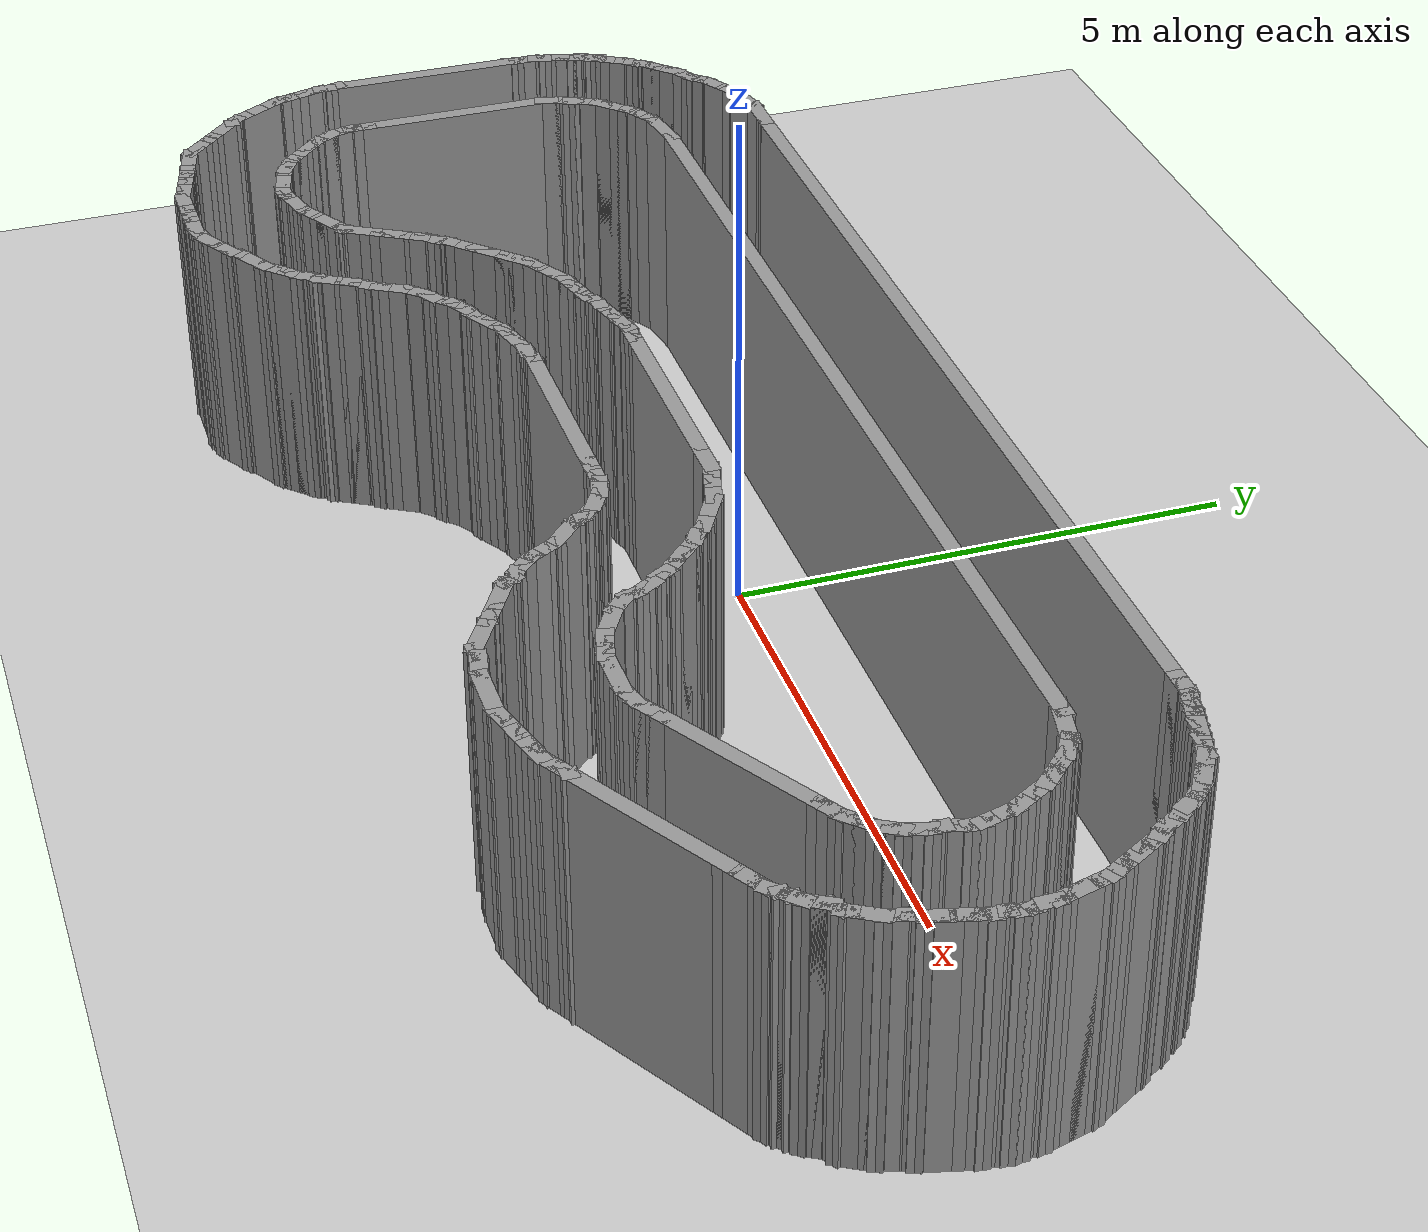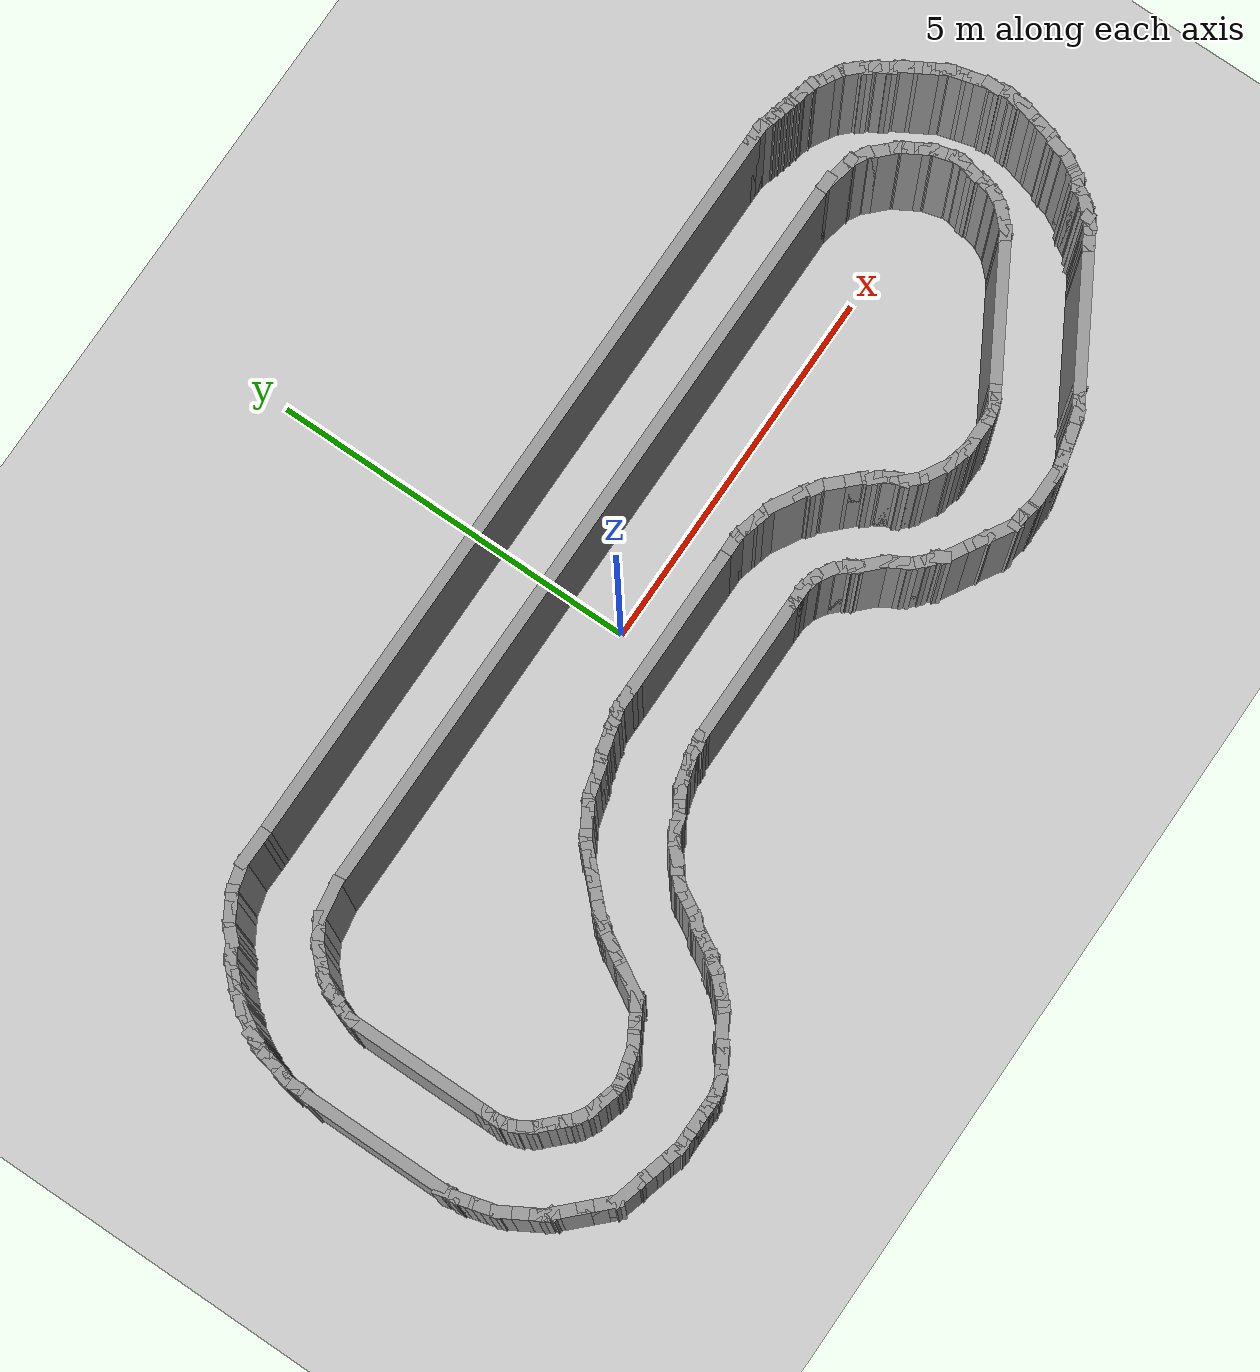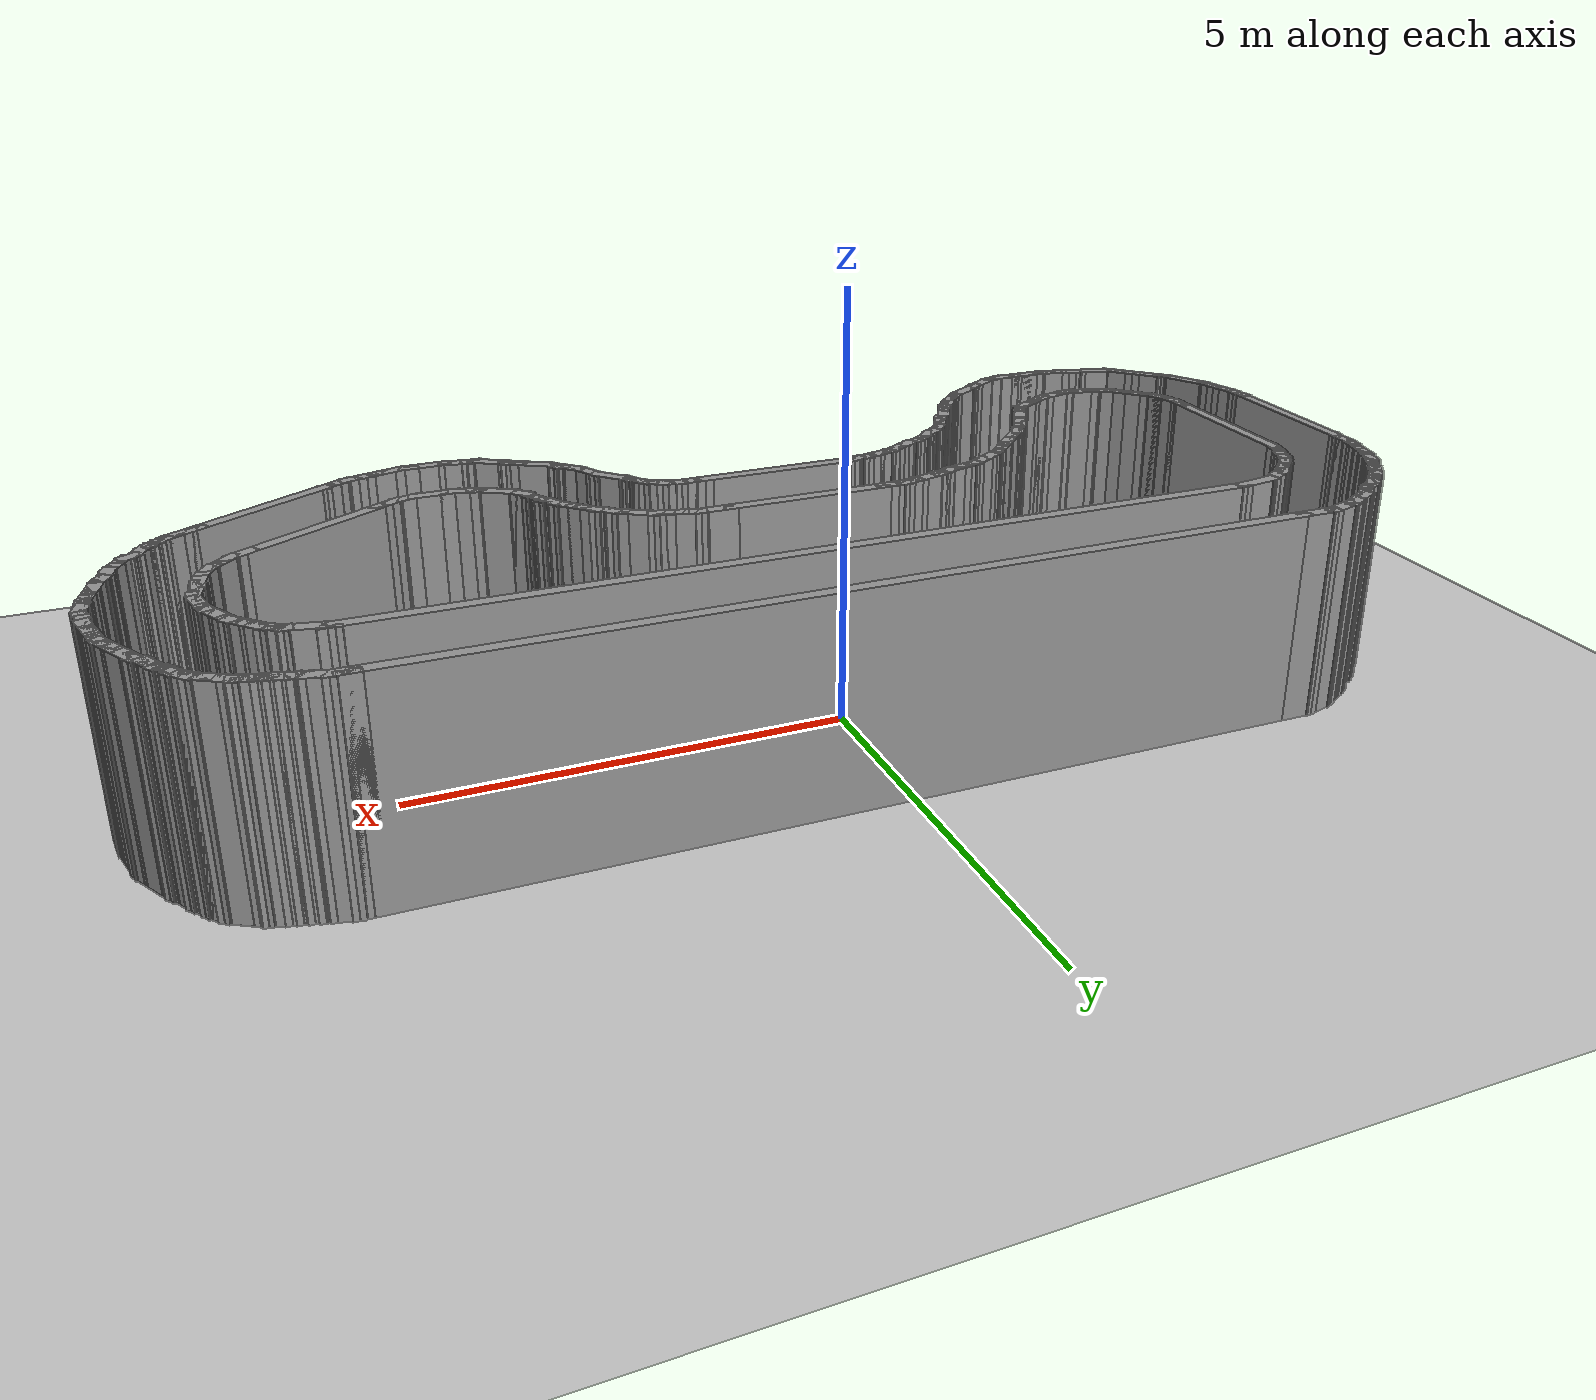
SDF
<sdf version="1.7">
 <world name="default">
  <light name="sun" type="directional">
   <pose>0 0 10 0 -0 0</pose>
   <diffuse>0.8 0.8 0.8 1</diffuse>
   <specular>0.2 0.2 0.2 1</specular>
   <attenuation>
    <range>1000</range>
    <constant>0.9</constant>
    <linear>0.01</linear>
    <quadratic>0.001</quadratic>
   </attenuation>
   <direction>-0.5 0.1 -0.9</direction>
   <spot><inner_angle>0</inner_angle><outer_angle>0</outer_angle><falloff>0</falloff></spot>
  </light>
  <model name="ground_plane">
   <static>1</static>
   <link name="link">
    <collision name="collision">
     <geometry><plane><normal>0 0 1</normal><size>100 100</size></plane></geometry>
     <surface><friction><ode><mu>100</mu><mu2>50</mu2></ode></friction></surface>
    </collision>
    <visual name="visual">
     <cast_shadows>0</cast_shadows>
     <geometry><plane><normal>0 0 1</normal><size>100 100</size></plane></geometry>
     <material>
      <script><uri>file://media/materials/scripts/gazebo.material</uri><name>Gazebo/Grey</name></script>
     </material>
    </visual>
   </link>
  </model>
  <gravity>0 0 -9.8</gravity>
  <magnetic_field>6e-06 2.3e-05 -4.2e-05</magnetic_field>
  <atmosphere type="adiabatic"/>
  <physics type="ode">
   <max_step_size>0.001</max_step_size>
   <real_time_factor>1</real_time_factor>
   <real_time_update_rate>1000</real_time_update_rate>
  </physics>
  <scene><ambient>0.4 0.4 0.4 1</ambient><background>0.7 0.7 0.7 1</background><shadows>1</shadows></scene>
  <audio><device>default</device></audio>
  <spherical_coordinates>
   <surface_model>EARTH_WGS84</surface_model>
   <latitude_deg>0</latitude_deg>
   <longitude_deg>0</longitude_deg>
   <elevation>0</elevation>
   <heading_deg>0</heading_deg>
  </spherical_coordinates>
  <model name="playground_track">
   <pose>0.405729 -1.1815 0 0 -0 0</pose>
   <link name="Wall_1">
    <collision name="Wall_1_Collision">
     <geometry><box><size>10.25 0.15 2.5</size></box></geometry>
     <pose>0 0 1.25 0 -0 0</pose>
    </collision>
    <visual name="Wall_1_Visual">
     <pose>0 0 1.25 0 -0 0</pose>
     <geometry><box><size>10.25 0.15 2.5</size></box></geometry>
     <material>
      <script><uri>file://media/materials/scripts/gazebo.material</uri><name>Gazebo/Grey</name></script>
      <ambient>1 1 1 1</ambient>
     </material>
     <meta><layer>0</layer></meta>
    </visual>
    <pose>-0.003811 3.01631 0 0 -0 0</pose>
   </link>
   <link name="Wall_100">
    <collision name="Wall_100_Collision">
     <geometry><box><size>0.25 0.15 2.5</size></box></geometry>
     <pose>0 0 1.25 0 -0 0</pose>
    </collision>
    <visual name="Wall_100_Visual">
     <pose>0 0 1.25 0 -0 0</pose>
     <geometry><box><size>0.25 0.15 2.5</size></box></geometry>
     <material>
      <script><uri>file://media/materials/scripts/gazebo.material</uri><name>Gazebo/Grey</name></script>
      <ambient>1 1 1 1</ambient>
     </material>
     <meta><layer>0</layer></meta>
    </visual>
    <pose>4.11775 -2.12764 0 0 -0 -2.87979</pose>
   </link>
   <link name="Wall_101">
    <collision name="Wall_101_Collision">
     <geometry><box><size>0.25 0.15 2.5</size></box></geometry>
     <pose>0 0 1.25 0 -0 0</pose>
    </collision>
    <visual name="Wall_101_Visual">
     <pose>0 0 1.25 0 -0 0</pose>
     <geometry><box><size>0.25 0.15 2.5</size></box></geometry>
     <material>
      <script><uri>file://media/materials/scripts/gazebo.material</uri><name>Gazebo/Grey</name></script>
      <ambient>1 1 1 1</ambient>
     </material>
     <meta><layer>0</layer></meta>
    </visual>
    <pose>4.02116 -2.15352 0 0 -0 -2.87979</pose>
   </link>
   <link name="Wall_102">
    <collision name="Wall_102_Collision">
     <geometry><box><size>0.25 0.15 2.5</size></box></geometry>
     <pose>0 0 1.25 0 -0 0</pose>
    </collision>
    <visual name="Wall_102_Visual">
     <pose>0 0 1.25 0 -0 0</pose>
     <geometry><box><size>0.25 0.15 2.5</size></box></geometry>
     <material>
      <script><uri>file://media/materials/scripts/gazebo.material</uri><name>Gazebo/Grey</name></script>
      <ambient>1 1 1 1</ambient>
     </material>
     <meta><layer>0</layer></meta>
    </visual>
    <pose>3.92457 -2.17941 0 0 -0 -2.87979</pose>
   </link>
   <link name="Wall_103">
    <collision name="Wall_103_Collision">
     <geometry><box><size>0.25 0.15 2.5</size></box></geometry>
     <pose>0 0 1.25 0 -0 0</pose>
    </collision>
    <visual name="Wall_103_Visual">
     <pose>0 0 1.25 0 -0 0</pose>
     <geometry><box><size>0.25 0.15 2.5</size></box></geometry>
     <material>
      <script><uri>file://media/materials/scripts/gazebo.material</uri><name>Gazebo/Grey</name></script>
      <ambient>1 1 1 1</ambient>
     </material>
     <meta><layer>0</layer></meta>
    </visual>
    <pose>3.82797 -2.20529 0 0 -0 -2.87979</pose>
   </link>
   <link name="Wall_104">
    <collision name="Wall_104_Collision">
     <geometry><box><size>0.25 0.15 2.5</size></box></geometry>
     <pose>0 0 1.25 0 -0 0</pose>
    </collision>
    <visual name="Wall_104_Visual">
     <pose>0 0 1.25 0 -0 0</pose>
     <geometry><box><size>0.25 0.15 2.5</size></box></geometry>
     <material>
      <script><uri>file://media/materials/scripts/gazebo.material</uri><name>Gazebo/Grey</name></script>
      <ambient>1 1 1 1</ambient>
     </material>
     <meta><layer>0</layer></meta>
    </visual>
    <pose>3.72968 -2.21823 0 0 -0 3.14159</pose>
   </link>
   <link name="Wall_105">
    <collision name="Wall_105_Collision">
     <geometry><box><size>0.52645 0.15 2.5</size></box></geometry>
     <pose>0 0 1.25 0 -0 0</pose>
    </collision>
    <visual name="Wall_105_Visual">
     <pose>0 0 1.25 0 -0 0</pose>
     <geometry><box><size>0.52645 0.15 2.5</size></box></geometry>
     <material>
      <script><uri>file://media/materials/scripts/gazebo.material</uri><name>Gazebo/Grey</name></script>
      <ambient>1 1 1 1</ambient>
     </material>
     <meta><layer>0</layer></meta>
    </visual>
    <pose>3.49145 -2.21823 0 0 -0 3.14159</pose>
   </link>
   <link name="Wall_106">
    <collision name="Wall_106_Collision">
     <geometry><box><size>0.15 0.15 2.5</size></box></geometry>
     <pose>0 0 1.25 0 -0 0</pose>
    </collision>
    <visual name="Wall_106_Visual">
     <pose>0 0 1.25 0 -0 0</pose>
     <geometry><box><size>0.15 0.15 2.5</size></box></geometry>
     <material>
      <script><uri>file://media/materials/scripts/gazebo.material</uri><name>Gazebo/Grey</name></script>
      <ambient>1 1 1 1</ambient>
     </material>
     <meta><layer>0</layer></meta>
    </visual>
    <pose>3.30323 -2.21823 0 0 -0 0</pose>
   </link>
   <link name="Wall_110">
    <collision name="Wall_110_Collision">
     <geometry><box><size>0.15 0.15 2.5</size></box></geometry>
     <pose>0 0 1.25 0 -0 0</pose>
    </collision>
    <visual name="Wall_110_Visual">
     <pose>0 0 1.25 0 -0 0</pose>
     <geometry><box><size>0.15 0.15 2.5</size></box></geometry>
     <material>
      <script><uri>file://media/materials/scripts/gazebo.material</uri><name>Gazebo/Grey</name></script>
      <ambient>1 1 1 1</ambient>
     </material>
     <meta><layer>0</layer></meta>
    </visual>
    <pose>3.03649 -2.16647 0 0 -0 0</pose>
   </link>
   <link name="Wall_114">
    <collision name="Wall_114_Collision">
     <geometry><box><size>0.421712 0.15 2.5</size></box></geometry>
     <pose>0 0 1.25 0 -0 0</pose>
    </collision>
    <visual name="Wall_114_Visual">
     <pose>0 0 1.25 0 -0 0</pose>
     <geometry><box><size>0.421712 0.15 2.5</size></box></geometry>
     <material>
      <script><uri>file://media/materials/scripts/gazebo.material</uri><name>Gazebo/Grey</name></script>
      <ambient>1 1 1 1</ambient>
     </material>
     <meta><layer>0</layer></meta>
    </visual>
    <pose>3.16986 -2.19235 0 0 -0 2.94991</pose>
   </link>
   <link name="Wall_115">
    <collision name="Wall_115_Collision">
     <geometry><box><size>0.15 0.15 2.5</size></box></geometry>
     <pose>0 0 1.25 0 -0 0</pose>
    </collision>
    <visual name="Wall_115_Visual">
     <pose>0 0 1.25 0 -0 0</pose>
     <geometry><box><size>0.15 0.15 2.5</size></box></geometry>
     <material>
      <script><uri>file://media/materials/scripts/gazebo.material</uri><name>Gazebo/Grey</name></script>
      <ambient>1 1 1 1</ambient>
     </material>
     <meta><layer>0</layer></meta>
    </visual>
    <pose>3.03649 -2.16647 0 0 -0 0</pose>
   </link>
   <link name="Wall_118">
    <collision name="Wall_118_Collision">
     <geometry><box><size>0.15 0.15 2.5</size></box></geometry>
     <pose>0 0 1.25 0 -0 0</pose>
    </collision>
    <visual name="Wall_118_Visual">
     <pose>0 0 1.25 0 -0 0</pose>
     <geometry><box><size>0.15 0.15 2.5</size></box></geometry>
     <material>
      <script><uri>file://media/materials/scripts/gazebo.material</uri><name>Gazebo/Grey</name></script>
      <ambient>1 1 1 1</ambient>
     </material>
     <meta><layer>0</layer></meta>
    </visual>
    <pose>2.61182 -1.97298 0 0 -0 0</pose>
   </link>
   <link name="Wall_120">
    <collision name="Wall_120_Collision">
     <geometry><box><size>0.15 0.15 2.5</size></box></geometry>
     <pose>0 0 1.25 0 -0 0</pose>
    </collision>
    <visual name="Wall_120_Visual">
     <pose>0 0 1.25 0 -0 0</pose>
     <geometry><box><size>0.15 0.15 2.5</size></box></geometry>
     <material>
      <script><uri>file://media/materials/scripts/gazebo.material</uri><name>Gazebo/Grey</name></script>
      <ambient>1 1 1 1</ambient>
     </material>
     <meta><layer>0</layer></meta>
    </visual>
    <pose>3.03649 -2.16647 0 0 -0 0</pose>
   </link>
   <link name="Wall_124">
    <collision name="Wall_124_Collision">
     <geometry><box><size>0.25 0.15 2.5</size></box></geometry>
     <pose>0 0 1.25 0 -0 0</pose>
    </collision>
    <visual name="Wall_124_Visual">
     <pose>0 0 1.25 0 -0 0</pose>
     <geometry><box><size>0.25 0.15 2.5</size></box></geometry>
     <material>
      <script><uri>file://media/materials/scripts/gazebo.material</uri><name>Gazebo/Grey</name></script>
      <ambient>1 1 1 1</ambient>
     </material>
     <meta><layer>0</layer></meta>
    </visual>
    <pose>2.98649 -2.16647 0 0 -0 3.14159</pose>
   </link>
   <link name="Wall_125">
    <collision name="Wall_125_Collision">
     <geometry><box><size>0.527958 0.15 2.5</size></box></geometry>
     <pose>0 0 1.25 0 -0 0</pose>
    </collision>
    <visual name="Wall_125_Visual">
     <pose>0 0 1.25 0 -0 0</pose>
     <geometry><box><size>0.527958 0.15 2.5</size></box></geometry>
     <material>
      <script><uri>file://media/materials/scripts/gazebo.material</uri><name>Gazebo/Grey</name></script>
      <ambient>1 1 1 1</ambient>
     </material>
     <meta><layer>0</layer></meta>
    </visual>
    <pose>2.77415 -2.06972 0 0 -0 2.60417</pose>
   </link>
   <link name="Wall_126">
    <collision name="Wall_126_Collision">
     <geometry><box><size>0.25 0.15 2.5</size></box></geometry>
     <pose>0 0 1.25 0 -0 0</pose>
    </collision>
    <visual name="Wall_126_Visual">
     <pose>0 0 1.25 0 -0 0</pose>
     <geometry><box><size>0.25 0.15 2.5</size></box></geometry>
     <material>
      <script><uri>file://media/materials/scripts/gazebo.material</uri><name>Gazebo/Grey</name></script>
      <ambient>1 1 1 1</ambient>
     </material>
     <meta><layer>0</layer></meta>
    </visual>
    <pose>2.56852 -1.94798 0 0 -0 2.61799</pose>
   </link>
   <link name="Wall_127">
    <collision name="Wall_127_Collision">
     <geometry><box><size>0.25 0.15 2.5</size></box></geometry>
     <pose>0 0 1.25 0 -0 0</pose>
    </collision>
    <visual name="Wall_127_Visual">
     <pose>0 0 1.25 0 -0 0</pose>
     <geometry><box><size>0.25 0.15 2.5</size></box></geometry>
     <material>
      <script><uri>file://media/materials/scripts/gazebo.material</uri><name>Gazebo/Grey</name></script>
      <ambient>1 1 1 1</ambient>
     </material>
     <meta><layer>0</layer></meta>
    </visual>
    <pose>2.48191 -1.89798 0 0 -0 2.61799</pose>
   </link>
   <link name="Wall_128">
    <collision name="Wall_128_Collision">
     <geometry><box><size>0.5 0.15 2.5</size></box></geometry>
     <pose>0 0 1.25 0 -0 0</pose>
    </collision>
    <visual name="Wall_128_Visual">
     <pose>0 0 1.25 0 -0 0</pose>
     <geometry><box><size>0.5 0.15 2.5</size></box></geometry>
     <material>
      <script><uri>file://media/materials/scripts/gazebo.material</uri><name>Gazebo/Grey</name></script>
      <ambient>1 1 1 1</ambient>
     </material>
     <meta><layer>0</layer></meta>
    </visual>
    <pose>2.28706 -1.78548 0 0 -0 2.61799</pose>
   </link>
   <link name="Wall_129">
    <collision name="Wall_129_Collision">
     <geometry><box><size>0.25 0.15 2.5</size></box></geometry>
     <pose>0 0 1.25 0 -0 0</pose>
    </collision>
    <visual name="Wall_129_Visual">
     <pose>0 0 1.25 0 -0 0</pose>
     <geometry><box><size>0.25 0.15 2.5</size></box></geometry>
     <material>
      <script><uri>file://media/materials/scripts/gazebo.material</uri><name>Gazebo/Grey</name></script>
      <ambient>1 1 1 1</ambient>
     </material>
     <meta><layer>0</layer></meta>
    </visual>
    <pose>2.1105 -1.65468 0 0 -0 2.0944</pose>
   </link>
   <link name="Wall_130">
    <collision name="Wall_130_Collision">
     <geometry><box><size>0.25 0.15 2.5</size></box></geometry>
     <pose>0 0 1.25 0 -0 0</pose>
    </collision>
    <visual name="Wall_130_Visual">
     <pose>0 0 1.25 0 -0 0</pose>
     <geometry><box><size>0.25 0.15 2.5</size></box></geometry>
     <material>
      <script><uri>file://media/materials/scripts/gazebo.material</uri><name>Gazebo/Grey</name></script>
      <ambient>1 1 1 1</ambient>
     </material>
     <meta><layer>0</layer></meta>
    </visual>
    <pose>2.0422 -1.58638 0 0 -0 2.61799</pose>
   </link>
   <link name="Wall_131">
    <collision name="Wall_131_Collision">
     <geometry><box><size>0.25 0.15 2.5</size></box></geometry>
     <pose>0 0 1.25 0 -0 0</pose>
    </collision>
    <visual name="Wall_131_Visual">
     <pose>0 0 1.25 0 -0 0</pose>
     <geometry><box><size>0.25 0.15 2.5</size></box></geometry>
     <material>
      <script><uri>file://media/materials/scripts/gazebo.material</uri><name>Gazebo/Grey</name></script>
      <ambient>1 1 1 1</ambient>
     </material>
     <meta><layer>0</layer></meta>
    </visual>
    <pose>1.96354 -1.52602 0 0 -0 2.35619</pose>
   </link>
   <link name="Wall_132">
    <collision name="Wall_132_Collision">
     <geometry><box><size>0.25 0.15 2.5</size></box></geometry>
     <pose>0 0 1.25 0 -0 0</pose>
    </collision>
    <visual name="Wall_132_Visual">
     <pose>0 0 1.25 0 -0 0</pose>
     <geometry><box><size>0.25 0.15 2.5</size></box></geometry>
     <material>
      <script><uri>file://media/materials/scripts/gazebo.material</uri><name>Gazebo/Grey</name></script>
      <ambient>1 1 1 1</ambient>
     </material>
     <meta><layer>0</layer></meta>
    </visual>
    <pose>1.89283 -1.45531 0 0 -0 2.35619</pose>
   </link>
   <link name="Wall_133">
    <collision name="Wall_133_Collision">
     <geometry><box><size>0.25 0.15 2.5</size></box></geometry>
     <pose>0 0 1.25 0 -0 0</pose>
    </collision>
    <visual name="Wall_133_Visual">
     <pose>0 0 1.25 0 -0 0</pose>
     <geometry><box><size>0.25 0.15 2.5</size></box></geometry>
     <material>
      <script><uri>file://media/materials/scripts/gazebo.material</uri><name>Gazebo/Grey</name></script>
      <ambient>1 1 1 1</ambient>
     </material>
     <meta><layer>0</layer></meta>
    </visual>
    <pose>1.83248 -1.37665 0 0 -0 2.0944</pose>
   </link>
   <link name="Wall_134">
    <collision name="Wall_134_Collision">
     <geometry><box><size>0.25 0.15 2.5</size></box></geometry>
     <pose>0 0 1.25 0 -0 0</pose>
    </collision>
    <visual name="Wall_134_Visual">
     <pose>0 0 1.25 0 -0 0</pose>
     <geometry><box><size>0.25 0.15 2.5</size></box></geometry>
     <material>
      <script><uri>file://media/materials/scripts/gazebo.material</uri><name>Gazebo/Grey</name></script>
      <ambient>1 1 1 1</ambient>
     </material>
     <meta><layer>0</layer></meta>
    </visual>
    <pose>1.78248 -1.29005 0 0 -0 2.0944</pose>
   </link>
   <link name="Wall_135">
    <collision name="Wall_135_Collision">
     <geometry><box><size>0.25 0.15 2.5</size></box></geometry>
     <pose>0 0 1.25 0 -0 0</pose>
    </collision>
    <visual name="Wall_135_Visual">
     <pose>0 0 1.25 0 -0 0</pose>
     <geometry><box><size>0.25 0.15 2.5</size></box></geometry>
     <material>
      <script><uri>file://media/materials/scripts/gazebo.material</uri><name>Gazebo/Grey</name></script>
      <ambient>1 1 1 1</ambient>
     </material>
     <meta><layer>0</layer></meta>
    </visual>
    <pose>1.73248 -1.20345 0 0 -0 2.0944</pose>
   </link>
   <link name="Wall_136">
    <collision name="Wall_136_Collision">
     <geometry><box><size>0.5 0.15 2.5</size></box></geometry>
     <pose>0 0 1.25 0 -0 0</pose>
    </collision>
    <visual name="Wall_136_Visual">
     <pose>0 0 1.25 0 -0 0</pose>
     <geometry><box><size>0.5 0.15 2.5</size></box></geometry>
     <material>
      <script><uri>file://media/materials/scripts/gazebo.material</uri><name>Gazebo/Grey</name></script>
      <ambient>1 1 1 1</ambient>
     </material>
     <meta><layer>0</layer></meta>
    </visual>
    <pose>1.58373 -1.0364 0 0 -0 2.35619</pose>
   </link>
   <link name="Wall_137">
    <collision name="Wall_137_Collision">
     <geometry><box><size>0.15 0.15 2.5</size></box></geometry>
     <pose>0 0 1.25 0 -0 0</pose>
    </collision>
    <visual name="Wall_137_Visual">
     <pose>0 0 1.25 0 -0 0</pose>
     <geometry><box><size>0.15 0.15 2.5</size></box></geometry>
     <material>
      <script><uri>file://media/materials/scripts/gazebo.material</uri><name>Gazebo/Grey</name></script>
      <ambient>1 1 1 1</ambient>
     </material>
     <meta><layer>0</layer></meta>
    </visual>
    <pose>1.45999 -0.91266 0 0 -0 0</pose>
   </link>
   <link name="Wall_138">
    <collision name="Wall_138_Collision">
     <geometry><box><size>0.15 0.15 2.5</size></box></geometry>
     <pose>0 0 1.25 0 -0 0</pose>
    </collision>
    <visual name="Wall_138_Visual">
     <pose>0 0 1.25 0 -0 0</pose>
     <geometry><box><size>0.15 0.15 2.5</size></box></geometry>
     <material>
      <script><uri>file://media/materials/scripts/gazebo.material</uri><name>Gazebo/Grey</name></script>
      <ambient>1 1 1 1</ambient>
     </material>
     <meta><layer>0</layer></meta>
    </visual>
    <pose>1.45999 -0.91266 0 0 -0 0</pose>
   </link>
   <link name="Wall_139">
    <collision name="Wall_139_Collision">
     <geometry><box><size>0.25 0.15 2.5</size></box></geometry>
     <pose>0 0 1.25 0 -0 0</pose>
    </collision>
    <visual name="Wall_139_Visual">
     <pose>0 0 1.25 0 -0 0</pose>
     <geometry><box><size>0.25 0.15 2.5</size></box></geometry>
     <material>
      <script><uri>file://media/materials/scripts/gazebo.material</uri><name>Gazebo/Grey</name></script>
      <ambient>1 1 1 1</ambient>
     </material>
     <meta><layer>0</layer></meta>
    </visual>
    <pose>1.43499 -0.869358 0 0 -0 2.0944</pose>
   </link>
   <link name="Wall_140">
    <collision name="Wall_140_Collision">
     <geometry><box><size>0.15 0.15 2.5</size></box></geometry>
     <pose>0 0 1.25 0 -0 0</pose>
    </collision>
    <visual name="Wall_140_Visual">
     <pose>0 0 1.25 0 -0 0</pose>
     <geometry><box><size>0.15 0.15 2.5</size></box></geometry>
     <material>
      <script><uri>file://media/materials/scripts/gazebo.material</uri><name>Gazebo/Grey</name></script>
      <ambient>1 1 1 1</ambient>
     </material>
     <meta><layer>0</layer></meta>
    </visual>
    <pose>1.40999 -0.826057 0 0 -0 0</pose>
   </link>
   <link name="Wall_141">
    <collision name="Wall_141_Collision">
     <geometry><box><size>0.25 0.15 2.5</size></box></geometry>
     <pose>0 0 1.25 0 -0 0</pose>
    </collision>
    <visual name="Wall_141_Visual">
     <pose>0 0 1.25 0 -0 0</pose>
     <geometry><box><size>0.25 0.15 2.5</size></box></geometry>
     <material>
      <script><uri>file://media/materials/scripts/gazebo.material</uri><name>Gazebo/Grey</name></script>
      <ambient>1 1 1 1</ambient>
     </material>
     <meta><layer>0</layer></meta>
    </visual>
    <pose>1.37464 -0.790702 0 0 -0 2.35619</pose>
   </link>
   <link name="Wall_142">
    <collision name="Wall_142_Collision">
     <geometry><box><size>0.25 0.15 2.5</size></box></geometry>
     <pose>0 0 1.25 0 -0 0</pose>
    </collision>
    <visual name="Wall_142_Visual">
     <pose>0 0 1.25 0 -0 0</pose>
     <geometry><box><size>0.25 0.15 2.5</size></box></geometry>
     <material>
      <script><uri>file://media/materials/scripts/gazebo.material</uri><name>Gazebo/Grey</name></script>
      <ambient>1 1 1 1</ambient>
     </material>
     <meta><layer>0</layer></meta>
    </visual>
    <pose>1.30393 -0.719991 0 0 -0 2.35619</pose>
   </link>
   <link name="Wall_143">
    <collision name="Wall_143_Collision">
     <geometry><box><size>0.25 0.15 2.5</size></box></geometry>
     <pose>0 0 1.25 0 -0 0</pose>
    </collision>
    <visual name="Wall_143_Visual">
     <pose>0 0 1.25 0 -0 0</pose>
     <geometry><box><size>0.25 0.15 2.5</size></box></geometry>
     <material>
      <script><uri>file://media/materials/scripts/gazebo.material</uri><name>Gazebo/Grey</name></script>
      <ambient>1 1 1 1</ambient>
     </material>
     <meta><layer>0</layer></meta>
    </visual>
    <pose>1.22527 -0.659636 0 0 -0 2.61799</pose>
   </link>
   <link name="Wall_144">
    <collision name="Wall_144_Collision">
     <geometry><box><size>0.25 0.15 2.5</size></box></geometry>
     <pose>0 0 1.25 0 -0 0</pose>
    </collision>
    <visual name="Wall_144_Visual">
     <pose>0 0 1.25 0 -0 0</pose>
     <geometry><box><size>0.25 0.15 2.5</size></box></geometry>
     <material>
      <script><uri>file://media/materials/scripts/gazebo.material</uri><name>Gazebo/Grey</name></script>
      <ambient>1 1 1 1</ambient>
     </material>
     <meta><layer>0</layer></meta>
    </visual>
    <pose>1.13867 -0.609636 0 0 -0 2.61799</pose>
   </link>
   <link name="Wall_145">
    <collision name="Wall_145_Collision">
     <geometry><box><size>0.25 0.15 2.5</size></box></geometry>
     <pose>0 0 1.25 0 -0 0</pose>
    </collision>
    <visual name="Wall_145_Visual">
     <pose>0 0 1.25 0 -0 0</pose>
     <geometry><box><size>0.25 0.15 2.5</size></box></geometry>
     <material>
      <script><uri>file://media/materials/scripts/gazebo.material</uri><name>Gazebo/Grey</name></script>
      <ambient>1 1 1 1</ambient>
     </material>
     <meta><layer>0</layer></meta>
    </visual>
    <pose>1.04707 -0.571695 0 0 -0 2.87979</pose>
   </link>
   <link name="Wall_146">
    <collision name="Wall_146_Collision">
     <geometry><box><size>0.25 0.15 2.5</size></box></geometry>
     <pose>0 0 1.25 0 -0 0</pose>
    </collision>
    <visual name="Wall_146_Visual">
     <pose>0 0 1.25 0 -0 0</pose>
     <geometry><box><size>0.25 0.15 2.5</size></box></geometry>
     <material>
      <script><uri>file://media/materials/scripts/gazebo.material</uri><name>Gazebo/Grey</name></script>
      <ambient>1 1 1 1</ambient>
     </material>
     <meta><layer>0</layer></meta>
    </visual>
    <pose>0.950476 -0.545813 0 0 -0 2.87979</pose>
   </link>
   <link name="Wall_147">
    <collision name="Wall_147_Collision">
     <geometry><box><size>0.25 0.15 2.5</size></box></geometry>
     <pose>0 0 1.25 0 -0 0</pose>
    </collision>
    <visual name="Wall_147_Visual">
     <pose>0 0 1.25 0 -0 0</pose>
     <geometry><box><size>0.25 0.15 2.5</size></box></geometry>
     <material>
      <script><uri>file://media/materials/scripts/gazebo.material</uri><name>Gazebo/Grey</name></script>
      <ambient>1 1 1 1</ambient>
     </material>
     <meta><layer>0</layer></meta>
    </visual>
    <pose>0.852179 -0.532872 0 0 -0 3.14159</pose>
   </link>
   <link name="Wall_148">
    <collision name="Wall_148_Collision">
     <geometry><box><size>0.15 0.15 2.5</size></box></geometry>
     <pose>0 0 1.25 0 -0 0</pose>
    </collision>
    <visual name="Wall_148_Visual">
     <pose>0 0 1.25 0 -0 0</pose>
     <geometry><box><size>0.15 0.15 2.5</size></box></geometry>
     <material>
      <script><uri>file://media/materials/scripts/gazebo.material</uri><name>Gazebo/Grey</name></script>
      <ambient>1 1 1 1</ambient>
     </material>
     <meta><layer>0</layer></meta>
    </visual>
    <pose>0.802179 -0.532872 0 0 -0 0</pose>
   </link>
   <link name="Wall_149">
    <collision name="Wall_149_Collision">
     <geometry><box><size>0.25 0.15 2.5</size></box></geometry>
     <pose>0 0 1.25 0 -0 0</pose>
    </collision>
    <visual name="Wall_149_Visual">
     <pose>0 0 1.25 0 -0 0</pose>
     <geometry><box><size>0.25 0.15 2.5</size></box></geometry>
     <material>
      <script><uri>file://media/materials/scripts/gazebo.material</uri><name>Gazebo/Grey</name></script>
      <ambient>1 1 1 1</ambient>
     </material>
     <meta><layer>0</layer></meta>
    </visual>
    <pose>0.752179 -0.532872 0 0 -0 3.14159</pose>
   </link>
   <link name="Wall_15">
    <collision name="Wall_15_Collision">
     <geometry><box><size>0.25 0.15 2.5</size></box></geometry>
     <pose>0 0 1.25 0 -0 0</pose>
    </collision>
    <visual name="Wall_15_Visual">
     <pose>0 0 1.25 0 -0 0</pose>
     <geometry><box><size>0.25 0.15 2.5</size></box></geometry>
     <material>
      <script><uri>file://media/materials/scripts/gazebo.material</uri><name>Gazebo/Grey</name></script>
      <ambient>1 1 1 1</ambient>
     </material>
     <meta><layer>0</layer></meta>
    </visual>
    <pose>5.29448 3.00337 0 0 -0 -0.261799</pose>
   </link>
   <link name="Wall_150">
    <collision name="Wall_150_Collision">
     <geometry><box><size>0.25 0.15 2.5</size></box></geometry>
     <pose>0 0 1.25 0 -0 0</pose>
    </collision>
    <visual name="Wall_150_Visual">
     <pose>0 0 1.25 0 -0 0</pose>
     <geometry><box><size>0.25 0.15 2.5</size></box></geometry>
     <material>
      <script><uri>file://media/materials/scripts/gazebo.material</uri><name>Gazebo/Grey</name></script>
      <ambient>1 1 1 1</ambient>
     </material>
     <meta><layer>0</layer></meta>
    </visual>
    <pose>0.652179 -0.532872 0 0 -0 3.14159</pose>
   </link>
   <link name="Wall_151">
    <collision name="Wall_151_Collision">
     <geometry><box><size>2 0.15 2.5</size></box></geometry>
     <pose>0 0 1.25 0 -0 0</pose>
    </collision>
    <visual name="Wall_151_Visual">
     <pose>0 0 1.25 0 -0 0</pose>
     <geometry><box><size>2 0.15 2.5</size></box></geometry>
     <material>
      <script><uri>file://media/materials/scripts/gazebo.material</uri><name>Gazebo/Grey</name></script>
      <ambient>1 1 1 1</ambient>
     </material>
     <meta><layer>0</layer></meta>
    </visual>
    <pose>-0.322821 -0.532872 0 0 -0 3.14159</pose>
   </link>
   <link name="Wall_152">
    <collision name="Wall_152_Collision">
     <geometry><box><size>0.15 0.15 2.5</size></box></geometry>
     <pose>0 0 1.25 0 -0 0</pose>
    </collision>
    <visual name="Wall_152_Visual">
     <pose>0 0 1.25 0 -0 0</pose>
     <geometry><box><size>0.15 0.15 2.5</size></box></geometry>
     <material>
      <script><uri>file://media/materials/scripts/gazebo.material</uri><name>Gazebo/Grey</name></script>
      <ambient>1 1 1 1</ambient>
     </material>
     <meta><layer>0</layer></meta>
    </visual>
    <pose>-1.24782 -0.532872 0 0 -0 0</pose>
   </link>
   <link name="Wall_153">
    <collision name="Wall_153_Collision">
     <geometry><box><size>0.25 0.15 2.5</size></box></geometry>
     <pose>0 0 1.25 0 -0 0</pose>
    </collision>
    <visual name="Wall_153_Visual">
     <pose>0 0 1.25 0 -0 0</pose>
     <geometry><box><size>0.25 0.15 2.5</size></box></geometry>
     <material>
      <script><uri>file://media/materials/scripts/gazebo.material</uri><name>Gazebo/Grey</name></script>
      <ambient>1 1 1 1</ambient>
     </material>
     <meta><layer>0</layer></meta>
    </visual>
    <pose>-1.29612 -0.545813 0 0 -0 -2.87979</pose>
   </link>
   <link name="Wall_154">
    <collision name="Wall_154_Collision">
     <geometry><box><size>0.25 0.15 2.5</size></box></geometry>
     <pose>0 0 1.25 0 -0 0</pose>
    </collision>
    <visual name="Wall_154_Visual">
     <pose>0 0 1.25 0 -0 0</pose>
     <geometry><box><size>0.25 0.15 2.5</size></box></geometry>
     <material>
      <script><uri>file://media/materials/scripts/gazebo.material</uri><name>Gazebo/Grey</name></script>
      <ambient>1 1 1 1</ambient>
     </material>
     <meta><layer>0</layer></meta>
    </visual>
    <pose>-1.39441 -0.558754 0 0 -0 3.14159</pose>
   </link>
   <link name="Wall_155">
    <collision name="Wall_155_Collision">
     <geometry><box><size>0.25 0.15 2.5</size></box></geometry>
     <pose>0 0 1.25 0 -0 0</pose>
    </collision>
    <visual name="Wall_155_Visual">
     <pose>0 0 1.25 0 -0 0</pose>
     <geometry><box><size>0.25 0.15 2.5</size></box></geometry>
     <material>
      <script><uri>file://media/materials/scripts/gazebo.material</uri><name>Gazebo/Grey</name></script>
      <ambient>1 1 1 1</ambient>
     </material>
     <meta><layer>0</layer></meta>
    </visual>
    <pose>-1.49271 -0.571695 0 0 -0 -2.87979</pose>
   </link>
   <link name="Wall_156">
    <collision name="Wall_156_Collision">
     <geometry><box><size>0.25 0.15 2.5</size></box></geometry>
     <pose>0 0 1.25 0 -0 0</pose>
    </collision>
    <visual name="Wall_156_Visual">
     <pose>0 0 1.25 0 -0 0</pose>
     <geometry><box><size>0.25 0.15 2.5</size></box></geometry>
     <material>
      <script><uri>file://media/materials/scripts/gazebo.material</uri><name>Gazebo/Grey</name></script>
      <ambient>1 1 1 1</ambient>
     </material>
     <meta><layer>0</layer></meta>
    </visual>
    <pose>-1.5893 -0.597577 0 0 -0 -2.87979</pose>
   </link>
   <link name="Wall_157">
    <collision name="Wall_157_Collision">
     <geometry><box><size>0.25 0.15 2.5</size></box></geometry>
     <pose>0 0 1.25 0 -0 0</pose>
    </collision>
    <visual name="Wall_157_Visual">
     <pose>0 0 1.25 0 -0 0</pose>
     <geometry><box><size>0.25 0.15 2.5</size></box></geometry>
     <material>
      <script><uri>file://media/materials/scripts/gazebo.material</uri><name>Gazebo/Grey</name></script>
      <ambient>1 1 1 1</ambient>
     </material>
     <meta><layer>0</layer></meta>
    </visual>
    <pose>-1.5893 -0.597577 0 0 -0 0.261799</pose>
   </link>
   <link name="Wall_158">
    <collision name="Wall_158_Collision">
     <geometry><box><size>0.25 0.15 2.5</size></box></geometry>
     <pose>0 0 1.25 0 -0 0</pose>
    </collision>
    <visual name="Wall_158_Visual">
     <pose>0 0 1.25 0 -0 0</pose>
     <geometry><box><size>0.25 0.15 2.5</size></box></geometry>
     <material>
      <script><uri>file://media/materials/scripts/gazebo.material</uri><name>Gazebo/Grey</name></script>
      <ambient>1 1 1 1</ambient>
     </material>
     <meta><layer>0</layer></meta>
    </visual>
    <pose>-1.5893 -0.597577 0 0 -0 -2.87979</pose>
   </link>
   <link name="Wall_159">
    <collision name="Wall_159_Collision">
     <geometry><box><size>0.25 0.15 2.5</size></box></geometry>
     <pose>0 0 1.25 0 -0 0</pose>
    </collision>
    <visual name="Wall_159_Visual">
     <pose>0 0 1.25 0 -0 0</pose>
     <geometry><box><size>0.25 0.15 2.5</size></box></geometry>
     <material>
      <script><uri>file://media/materials/scripts/gazebo.material</uri><name>Gazebo/Grey</name></script>
      <ambient>1 1 1 1</ambient>
     </material>
     <meta><layer>0</layer></meta>
    </visual>
    <pose>-1.68589 -0.623459 0 0 -0 -2.87979</pose>
   </link>
   <link name="Wall_16">
    <collision name="Wall_16_Collision">
     <geometry><box><size>0.25 0.15 2.5</size></box></geometry>
     <pose>0 0 1.25 0 -0 0</pose>
    </collision>
    <visual name="Wall_16_Visual">
     <pose>0 0 1.25 0 -0 0</pose>
     <geometry><box><size>0.25 0.15 2.5</size></box></geometry>
     <material>
      <script><uri>file://media/materials/scripts/gazebo.material</uri><name>Gazebo/Grey</name></script>
      <ambient>1 1 1 1</ambient>
     </material>
     <meta><layer>0</layer></meta>
    </visual>
    <pose>5.39108 2.97749 0 0 -0 -0.261799</pose>
   </link>
   <link name="Wall_160">
    <collision name="Wall_160_Collision">
     <geometry><box><size>0.25 0.15 2.5</size></box></geometry>
     <pose>0 0 1.25 0 -0 0</pose>
    </collision>
    <visual name="Wall_160_Visual">
     <pose>0 0 1.25 0 -0 0</pose>
     <geometry><box><size>0.25 0.15 2.5</size></box></geometry>
     <material>
      <script><uri>file://media/materials/scripts/gazebo.material</uri><name>Gazebo/Grey</name></script>
      <ambient>1 1 1 1</ambient>
     </material>
     <meta><layer>0</layer></meta>
    </visual>
    <pose>-1.78249 -0.649341 0 0 -0 -2.87979</pose>
   </link>
   <link name="Wall_161">
    <collision name="Wall_161_Collision">
     <geometry><box><size>0.15 0.15 2.5</size></box></geometry>
     <pose>0 0 1.25 0 -0 0</pose>
    </collision>
    <visual name="Wall_161_Visual">
     <pose>0 0 1.25 0 -0 0</pose>
     <geometry><box><size>0.15 0.15 2.5</size></box></geometry>
     <material>
      <script><uri>file://media/materials/scripts/gazebo.material</uri><name>Gazebo/Grey</name></script>
      <ambient>1 1 1 1</ambient>
     </material>
     <meta><layer>0</layer></meta>
    </visual>
    <pose>-1.83078 -0.662282 0 0 -0 0</pose>
   </link>
   <link name="Wall_162">
    <collision name="Wall_162_Collision">
     <geometry><box><size>0.25 0.15 2.5</size></box></geometry>
     <pose>0 0 1.25 0 -0 0</pose>
    </collision>
    <visual name="Wall_162_Visual">
     <pose>0 0 1.25 0 -0 0</pose>
     <geometry><box><size>0.25 0.15 2.5</size></box></geometry>
     <material>
      <script><uri>file://media/materials/scripts/gazebo.material</uri><name>Gazebo/Grey</name></script>
      <ambient>1 1 1 1</ambient>
     </material>
     <meta><layer>0</layer></meta>
    </visual>
    <pose>-1.87409 -0.687282 0 0 -0 -2.61799</pose>
   </link>
   <link name="Wall_163">
    <collision name="Wall_163_Collision">
     <geometry><box><size>0.25 0.15 2.5</size></box></geometry>
     <pose>0 0 1.25 0 -0 0</pose>
    </collision>
    <visual name="Wall_163_Visual">
     <pose>0 0 1.25 0 -0 0</pose>
     <geometry><box><size>0.25 0.15 2.5</size></box></geometry>
     <material>
      <script><uri>file://media/materials/scripts/gazebo.material</uri><name>Gazebo/Grey</name></script>
      <ambient>1 1 1 1</ambient>
     </material>
     <meta><layer>0</layer></meta>
    </visual>
    <pose>-1.96069 -0.737282 0 0 -0 -2.61799</pose>
   </link>
   <link name="Wall_164">
    <collision name="Wall_164_Collision">
     <geometry><box><size>0.25 0.15 2.5</size></box></geometry>
     <pose>0 0 1.25 0 -0 0</pose>
    </collision>
    <visual name="Wall_164_Visual">
     <pose>0 0 1.25 0 -0 0</pose>
     <geometry><box><size>0.25 0.15 2.5</size></box></geometry>
     <material>
      <script><uri>file://media/materials/scripts/gazebo.material</uri><name>Gazebo/Grey</name></script>
      <ambient>1 1 1 1</ambient>
     </material>
     <meta><layer>0</layer></meta>
    </visual>
    <pose>-2.04729 -0.787282 0 0 -0 -2.61799</pose>
   </link>
   <link name="Wall_165">
    <collision name="Wall_165_Collision">
     <geometry><box><size>0.25 0.15 2.5</size></box></geometry>
     <pose>0 0 1.25 0 -0 0</pose>
    </collision>
    <visual name="Wall_165_Visual">
     <pose>0 0 1.25 0 -0 0</pose>
     <geometry><box><size>0.25 0.15 2.5</size></box></geometry>
     <material>
      <script><uri>file://media/materials/scripts/gazebo.material</uri><name>Gazebo/Grey</name></script>
      <ambient>1 1 1 1</ambient>
     </material>
     <meta><layer>0</layer></meta>
    </visual>
    <pose>-2.13389 -0.837282 0 0 -0 -2.61799</pose>
   </link>
   <link name="Wall_166">
    <collision name="Wall_166_Collision">
     <geometry><box><size>0.25 0.15 2.5</size></box></geometry>
     <pose>0 0 1.25 0 -0 0</pose>
    </collision>
    <visual name="Wall_166_Visual">
     <pose>0 0 1.25 0 -0 0</pose>
     <geometry><box><size>0.25 0.15 2.5</size></box></geometry>
     <material>
      <script><uri>file://media/materials/scripts/gazebo.material</uri><name>Gazebo/Grey</name></script>
      <ambient>1 1 1 1</ambient>
     </material>
     <meta><layer>0</layer></meta>
    </visual>
    <pose>-2.22549 -0.875222 0 0 -0 -2.87979</pose>
   </link>
   <link name="Wall_167">
    <collision name="Wall_167_Collision">
     <geometry><box><size>0.25 0.15 2.5</size></box></geometry>
     <pose>0 0 1.25 0 -0 0</pose>
    </collision>
    <visual name="Wall_167_Visual">
     <pose>0 0 1.25 0 -0 0</pose>
     <geometry><box><size>0.25 0.15 2.5</size></box></geometry>
     <material>
      <script><uri>file://media/materials/scripts/gazebo.material</uri><name>Gazebo/Grey</name></script>
      <ambient>1 1 1 1</ambient>
     </material>
     <meta><layer>0</layer></meta>
    </visual>
    <pose>-2.31709 -0.913163 0 0 -0 -2.61799</pose>
   </link>
   <link name="Wall_168">
    <collision name="Wall_168_Collision">
     <geometry><box><size>0.25 0.15 2.5</size></box></geometry>
     <pose>0 0 1.25 0 -0 0</pose>
    </collision>
    <visual name="Wall_168_Visual">
     <pose>0 0 1.25 0 -0 0</pose>
     <geometry><box><size>0.25 0.15 2.5</size></box></geometry>
     <material>
      <script><uri>file://media/materials/scripts/gazebo.material</uri><name>Gazebo/Grey</name></script>
      <ambient>1 1 1 1</ambient>
     </material>
     <meta><layer>0</layer></meta>
    </visual>
    <pose>-2.40369 -0.963163 0 0 -0 -2.61799</pose>
   </link>
   <link name="Wall_169">
    <collision name="Wall_169_Collision">
     <geometry><box><size>0.25 0.15 2.5</size></box></geometry>
     <pose>0 0 1.25 0 -0 0</pose>
    </collision>
    <visual name="Wall_169_Visual">
     <pose>0 0 1.25 0 -0 0</pose>
     <geometry><box><size>0.25 0.15 2.5</size></box></geometry>
     <material>
      <script><uri>file://media/materials/scripts/gazebo.material</uri><name>Gazebo/Grey</name></script>
      <ambient>1 1 1 1</ambient>
     </material>
     <meta><layer>0</layer></meta>
    </visual>
    <pose>-2.48235 -1.02352 0 0 -0 -2.35619</pose>
   </link>
   <link name="Wall_17">
    <collision name="Wall_17_Collision">
     <geometry><box><size>0.15 0.15 2.5</size></box></geometry>
     <pose>0 0 1.25 0 -0 0</pose>
    </collision>
    <visual name="Wall_17_Visual">
     <pose>0 0 1.25 0 -0 0</pose>
     <geometry><box><size>0.15 0.15 2.5</size></box></geometry>
     <material>
      <script><uri>file://media/materials/scripts/gazebo.material</uri><name>Gazebo/Grey</name></script>
      <ambient>1 1 1 1</ambient>
     </material>
     <meta><layer>0</layer></meta>
    </visual>
    <pose>5.43937 2.96455 0 0 -0 0</pose>
   </link>
   <link name="Wall_170">
    <collision name="Wall_170_Collision">
     <geometry><box><size>0.25 0.15 2.5</size></box></geometry>
     <pose>0 0 1.25 0 -0 0</pose>
    </collision>
    <visual name="Wall_170_Visual">
     <pose>0 0 1.25 0 -0 0</pose>
     <geometry><box><size>0.25 0.15 2.5</size></box></geometry>
     <material>
      <script><uri>file://media/materials/scripts/gazebo.material</uri><name>Gazebo/Grey</name></script>
      <ambient>1 1 1 1</ambient>
     </material>
     <meta><layer>0</layer></meta>
    </visual>
    <pose>-2.55306 -1.09423 0 0 -0 -2.35619</pose>
   </link>
   <link name="Wall_171">
    <collision name="Wall_171_Collision">
     <geometry><box><size>0.25 0.15 2.5</size></box></geometry>
     <pose>0 0 1.25 0 -0 0</pose>
    </collision>
    <visual name="Wall_171_Visual">
     <pose>0 0 1.25 0 -0 0</pose>
     <geometry><box><size>0.25 0.15 2.5</size></box></geometry>
     <material>
      <script><uri>file://media/materials/scripts/gazebo.material</uri><name>Gazebo/Grey</name></script>
      <ambient>1 1 1 1</ambient>
     </material>
     <meta><layer>0</layer></meta>
    </visual>
    <pose>-2.63171 -1.15458 0 0 -0 -2.61799</pose>
   </link>
   <link name="Wall_172">
    <collision name="Wall_172_Collision">
     <geometry><box><size>0.25 0.15 2.5</size></box></geometry>
     <pose>0 0 1.25 0 -0 0</pose>
    </collision>
    <visual name="Wall_172_Visual">
     <pose>0 0 1.25 0 -0 0</pose>
     <geometry><box><size>0.25 0.15 2.5</size></box></geometry>
     <material>
      <script><uri>file://media/materials/scripts/gazebo.material</uri><name>Gazebo/Grey</name></script>
      <ambient>1 1 1 1</ambient>
     </material>
     <meta><layer>0</layer></meta>
    </visual>
    <pose>-2.71037 -1.21494 0 0 -0 -2.35619</pose>
   </link>
   <link name="Wall_173">
    <collision name="Wall_173_Collision">
     <geometry><box><size>0.25 0.15 2.5</size></box></geometry>
     <pose>0 0 1.25 0 -0 0</pose>
    </collision>
    <visual name="Wall_173_Visual">
     <pose>0 0 1.25 0 -0 0</pose>
     <geometry><box><size>0.25 0.15 2.5</size></box></geometry>
     <material>
      <script><uri>file://media/materials/scripts/gazebo.material</uri><name>Gazebo/Grey</name></script>
      <ambient>1 1 1 1</ambient>
     </material>
     <meta><layer>0</layer></meta>
    </visual>
    <pose>-2.78108 -1.28565 0 0 -0 -2.35619</pose>
   </link>
   <link name="Wall_174">
    <collision name="Wall_174_Collision">
     <geometry><box><size>0.25 0.15 2.5</size></box></geometry>
     <pose>0 0 1.25 0 -0 0</pose>
    </collision>
    <visual name="Wall_174_Visual">
     <pose>0 0 1.25 0 -0 0</pose>
     <geometry><box><size>0.25 0.15 2.5</size></box></geometry>
     <material>
      <script><uri>file://media/materials/scripts/gazebo.material</uri><name>Gazebo/Grey</name></script>
      <ambient>1 1 1 1</ambient>
     </material>
     <meta><layer>0</layer></meta>
    </visual>
    <pose>-2.84144 -1.36431 0 0 -0 -2.0944</pose>
   </link>
   <link name="Wall_175">
    <collision name="Wall_175_Collision">
     <geometry><box><size>0.25 0.15 2.5</size></box></geometry>
     <pose>0 0 1.25 0 -0 0</pose>
    </collision>
    <visual name="Wall_175_Visual">
     <pose>0 0 1.25 0 -0 0</pose>
     <geometry><box><size>0.25 0.15 2.5</size></box></geometry>
     <material>
      <script><uri>file://media/materials/scripts/gazebo.material</uri><name>Gazebo/Grey</name></script>
      <ambient>1 1 1 1</ambient>
     </material>
     <meta><layer>0</layer></meta>
    </visual>
    <pose>-2.89144 -1.45091 0 0 -0 -2.0944</pose>
   </link>
   <link name="Wall_176">
    <collision name="Wall_176_Collision">
     <geometry><box><size>0.25 0.15 2.5</size></box></geometry>
     <pose>0 0 1.25 0 -0 0</pose>
    </collision>
    <visual name="Wall_176_Visual">
     <pose>0 0 1.25 0 -0 0</pose>
     <geometry><box><size>0.25 0.15 2.5</size></box></geometry>
     <material>
      <script><uri>file://media/materials/scripts/gazebo.material</uri><name>Gazebo/Grey</name></script>
      <ambient>1 1 1 1</ambient>
     </material>
     <meta><layer>0</layer></meta>
    </visual>
    <pose>-2.94144 -1.53751 0 0 -0 -2.0944</pose>
   </link>
   <link name="Wall_177">
    <collision name="Wall_177_Collision">
     <geometry><box><size>0.25 0.15 2.5</size></box></geometry>
     <pose>0 0 1.25 0 -0 0</pose>
    </collision>
    <visual name="Wall_177_Visual">
     <pose>0 0 1.25 0 -0 0</pose>
     <geometry><box><size>0.25 0.15 2.5</size></box></geometry>
     <material>
      <script><uri>file://media/materials/scripts/gazebo.material</uri><name>Gazebo/Grey</name></script>
      <ambient>1 1 1 1</ambient>
     </material>
     <meta><layer>0</layer></meta>
    </visual>
    <pose>-2.99144 -1.62411 0 0 -0 -2.0944</pose>
   </link>
   <link name="Wall_178">
    <collision name="Wall_178_Collision">
     <geometry><box><size>0.25 0.15 2.5</size></box></geometry>
     <pose>0 0 1.25 0 -0 0</pose>
    </collision>
    <visual name="Wall_178_Visual">
     <pose>0 0 1.25 0 -0 0</pose>
     <geometry><box><size>0.25 0.15 2.5</size></box></geometry>
     <material>
      <script><uri>file://media/materials/scripts/gazebo.material</uri><name>Gazebo/Grey</name></script>
      <ambient>1 1 1 1</ambient>
     </material>
     <meta><layer>0</layer></meta>
    </visual>
    <pose>-3.05179 -1.70277 0 0 -0 -2.35619</pose>
   </link>
   <link name="Wall_179">
    <collision name="Wall_179_Collision">
     <geometry><box><size>0.25 0.15 2.5</size></box></geometry>
     <pose>0 0 1.25 0 -0 0</pose>
    </collision>
    <visual name="Wall_179_Visual">
     <pose>0 0 1.25 0 -0 0</pose>
     <geometry><box><size>0.25 0.15 2.5</size></box></geometry>
     <material>
      <script><uri>file://media/materials/scripts/gazebo.material</uri><name>Gazebo/Grey</name></script>
      <ambient>1 1 1 1</ambient>
     </material>
     <meta><layer>0</layer></meta>
    </visual>
    <pose>-3.11215 -1.78143 0 0 -0 -2.0944</pose>
   </link>
   <link name="Wall_18">
    <collision name="Wall_18_Collision">
     <geometry><box><size>0.25 0.15 2.5</size></box></geometry>
     <pose>0 0 1.25 0 -0 0</pose>
    </collision>
    <visual name="Wall_18_Visual">
     <pose>0 0 1.25 0 -0 0</pose>
     <geometry><box><size>0.25 0.15 2.5</size></box></geometry>
     <material>
      <script><uri>file://media/materials/scripts/gazebo.material</uri><name>Gazebo/Grey</name></script>
      <ambient>1 1 1 1</ambient>
     </material>
     <meta><layer>0</layer></meta>
    </visual>
    <pose>5.48767 2.9516 0 0 -0 -0.261799</pose>
   </link>
   <link name="Wall_180">
    <collision name="Wall_180_Collision">
     <geometry><box><size>0.25 0.15 2.5</size></box></geometry>
     <pose>0 0 1.25 0 -0 0</pose>
    </collision>
    <visual name="Wall_180_Visual">
     <pose>0 0 1.25 0 -0 0</pose>
     <geometry><box><size>0.25 0.15 2.5</size></box></geometry>
     <material>
      <script><uri>file://media/materials/scripts/gazebo.material</uri><name>Gazebo/Grey</name></script>
      <ambient>1 1 1 1</ambient>
     </material>
     <meta><layer>0</layer></meta>
    </visual>
    <pose>-3.16215 -1.86803 0 0 -0 -2.0944</pose>
   </link>
   <link name="Wall_181">
    <collision name="Wall_181_Collision">
     <geometry><box><size>0.25 0.15 2.5</size></box></geometry>
     <pose>0 0 1.25 0 -0 0</pose>
    </collision>
    <visual name="Wall_181_Visual">
     <pose>0 0 1.25 0 -0 0</pose>
     <geometry><box><size>0.25 0.15 2.5</size></box></geometry>
     <material>
      <script><uri>file://media/materials/scripts/gazebo.material</uri><name>Gazebo/Grey</name></script>
      <ambient>1 1 1 1</ambient>
     </material>
     <meta><layer>0</layer></meta>
    </visual>
    <pose>-3.21215 -1.95463 0 0 -0 -2.0944</pose>
   </link>
   <link name="Wall_182">
    <collision name="Wall_182_Collision">
     <geometry><box><size>0.25 0.15 2.5</size></box></geometry>
     <pose>0 0 1.25 0 -0 0</pose>
    </collision>
    <visual name="Wall_182_Visual">
     <pose>0 0 1.25 0 -0 0</pose>
     <geometry><box><size>0.25 0.15 2.5</size></box></geometry>
     <material>
      <script><uri>file://media/materials/scripts/gazebo.material</uri><name>Gazebo/Grey</name></script>
      <ambient>1 1 1 1</ambient>
     </material>
     <meta><layer>0</layer></meta>
    </visual>
    <pose>-3.26215 -2.04124 0 0 -0 -2.0944</pose>
   </link>
   <link name="Wall_183">
    <collision name="Wall_183_Collision">
     <geometry><box><size>0.15 0.15 2.5</size></box></geometry>
     <pose>0 0 1.25 0 -0 0</pose>
    </collision>
    <visual name="Wall_183_Visual">
     <pose>0 0 1.25 0 -0 0</pose>
     <geometry><box><size>0.15 0.15 2.5</size></box></geometry>
     <material>
      <script><uri>file://media/materials/scripts/gazebo.material</uri><name>Gazebo/Grey</name></script>
      <ambient>1 1 1 1</ambient>
     </material>
     <meta><layer>0</layer></meta>
    </visual>
    <pose>-3.28715 -2.08454 0 0 -0 0</pose>
   </link>
   <link name="Wall_184">
    <collision name="Wall_184_Collision">
     <geometry><box><size>0.25 0.15 2.5</size></box></geometry>
     <pose>0 0 1.25 0 -0 0</pose>
    </collision>
    <visual name="Wall_184_Visual">
     <pose>0 0 1.25 0 -0 0</pose>
     <geometry><box><size>0.25 0.15 2.5</size></box></geometry>
     <material>
      <script><uri>file://media/materials/scripts/gazebo.material</uri><name>Gazebo/Grey</name></script>
      <ambient>1 1 1 1</ambient>
     </material>
     <meta><layer>0</layer></meta>
    </visual>
    <pose>-3.3225 -2.11989 0 0 -0 -2.35619</pose>
   </link>
   <link name="Wall_185">
    <collision name="Wall_185_Collision">
     <geometry><box><size>0.25 0.15 2.5</size></box></geometry>
     <pose>0 0 1.25 0 -0 0</pose>
    </collision>
    <visual name="Wall_185_Visual">
     <pose>0 0 1.25 0 -0 0</pose>
     <geometry><box><size>0.25 0.15 2.5</size></box></geometry>
     <material>
      <script><uri>file://media/materials/scripts/gazebo.material</uri><name>Gazebo/Grey</name></script>
      <ambient>1 1 1 1</ambient>
     </material>
     <meta><layer>0</layer></meta>
    </visual>
    <pose>-3.38286 -2.19855 0 0 -0 -2.0944</pose>
   </link>
   <link name="Wall_186">
    <collision name="Wall_186_Collision">
     <geometry><box><size>0.25 0.15 2.5</size></box></geometry>
     <pose>0 0 1.25 0 -0 0</pose>
    </collision>
    <visual name="Wall_186_Visual">
     <pose>0 0 1.25 0 -0 0</pose>
     <geometry><box><size>0.25 0.15 2.5</size></box></geometry>
     <material>
      <script><uri>file://media/materials/scripts/gazebo.material</uri><name>Gazebo/Grey</name></script>
      <ambient>1 1 1 1</ambient>
     </material>
     <meta><layer>0</layer></meta>
    </visual>
    <pose>-3.44321 -2.27721 0 0 -0 -2.35619</pose>
   </link>
   <link name="Wall_187">
    <collision name="Wall_187_Collision">
     <geometry><box><size>0.25 0.15 2.5</size></box></geometry>
     <pose>0 0 1.25 0 -0 0</pose>
    </collision>
    <visual name="Wall_187_Visual">
     <pose>0 0 1.25 0 -0 0</pose>
     <geometry><box><size>0.25 0.15 2.5</size></box></geometry>
     <material>
      <script><uri>file://media/materials/scripts/gazebo.material</uri><name>Gazebo/Grey</name></script>
      <ambient>1 1 1 1</ambient>
     </material>
     <meta><layer>0</layer></meta>
    </visual>
    <pose>-3.51392 -2.34792 0 0 -0 -2.35619</pose>
   </link>
   <link name="Wall_188">
    <collision name="Wall_188_Collision">
     <geometry><box><size>0.25 0.15 2.5</size></box></geometry>
     <pose>0 0 1.25 0 -0 0</pose>
    </collision>
    <visual name="Wall_188_Visual">
     <pose>0 0 1.25 0 -0 0</pose>
     <geometry><box><size>0.25 0.15 2.5</size></box></geometry>
     <material>
      <script><uri>file://media/materials/scripts/gazebo.material</uri><name>Gazebo/Grey</name></script>
      <ambient>1 1 1 1</ambient>
     </material>
     <meta><layer>0</layer></meta>
    </visual>
    <pose>-3.58464 -2.41863 0 0 -0 -2.35619</pose>
   </link>
   <link name="Wall_189">
    <collision name="Wall_189_Collision">
     <geometry><box><size>0.25 0.15 2.5</size></box></geometry>
     <pose>0 0 1.25 0 -0 0</pose>
    </collision>
    <visual name="Wall_189_Visual">
     <pose>0 0 1.25 0 -0 0</pose>
     <geometry><box><size>0.25 0.15 2.5</size></box></geometry>
     <material>
      <script><uri>file://media/materials/scripts/gazebo.material</uri><name>Gazebo/Grey</name></script>
      <ambient>1 1 1 1</ambient>
     </material>
     <meta><layer>0</layer></meta>
    </visual>
    <pose>-3.65535 -2.48934 0 0 -0 -2.35619</pose>
   </link>
   <link name="Wall_19">
    <collision name="Wall_19_Collision">
     <geometry><box><size>0.15 0.15 2.5</size></box></geometry>
     <pose>0 0 1.25 0 -0 0</pose>
    </collision>
    <visual name="Wall_19_Visual">
     <pose>0 0 1.25 0 -0 0</pose>
     <geometry><box><size>0.15 0.15 2.5</size></box></geometry>
     <material>
      <script><uri>file://media/materials/scripts/gazebo.material</uri><name>Gazebo/Grey</name></script>
      <ambient>1 1 1 1</ambient>
     </material>
     <meta><layer>0</layer></meta>
    </visual>
    <pose>5.53597 2.93866 0 0 -0 0</pose>
   </link>
   <link name="Wall_190">
    <collision name="Wall_190_Collision">
     <geometry><box><size>0.5 0.15 2.5</size></box></geometry>
     <pose>0 0 1.25 0 -0 0</pose>
    </collision>
    <visual name="Wall_190_Visual">
     <pose>0 0 1.25 0 -0 0</pose>
     <geometry><box><size>0.5 0.15 2.5</size></box></geometry>
     <material>
      <script><uri>file://media/materials/scripts/gazebo.material</uri><name>Gazebo/Grey</name></script>
      <ambient>1 1 1 1</ambient>
     </material>
     <meta><layer>0</layer></meta>
    </visual>
    <pose>-3.84226 -2.61219 0 0 -0 -2.61799</pose>
   </link>
   <link name="Wall_191">
    <collision name="Wall_191_Collision">
     <geometry><box><size>0.25 0.15 2.5</size></box></geometry>
     <pose>0 0 1.25 0 -0 0</pose>
    </collision>
    <visual name="Wall_191_Visual">
     <pose>0 0 1.25 0 -0 0</pose>
     <geometry><box><size>0.25 0.15 2.5</size></box></geometry>
     <material>
      <script><uri>file://media/materials/scripts/gazebo.material</uri><name>Gazebo/Grey</name></script>
      <ambient>1 1 1 1</ambient>
     </material>
     <meta><layer>0</layer></meta>
    </visual>
    <pose>-4.02916 -2.73505 0 0 -0 -2.35619</pose>
   </link>
   <link name="Wall_192">
    <collision name="Wall_192_Collision">
     <geometry><box><size>0.25 0.15 2.5</size></box></geometry>
     <pose>0 0 1.25 0 -0 0</pose>
    </collision>
    <visual name="Wall_192_Visual">
     <pose>0 0 1.25 0 -0 0</pose>
     <geometry><box><size>0.25 0.15 2.5</size></box></geometry>
     <material>
      <script><uri>file://media/materials/scripts/gazebo.material</uri><name>Gazebo/Grey</name></script>
      <ambient>1 1 1 1</ambient>
     </material>
     <meta><layer>0</layer></meta>
    </visual>
    <pose>-4.10782 -2.7954 0 0 -0 -2.61799</pose>
   </link>
   <link name="Wall_193">
    <collision name="Wall_193_Collision">
     <geometry><box><size>0.25 0.15 2.5</size></box></geometry>
     <pose>0 0 1.25 0 -0 0</pose>
    </collision>
    <visual name="Wall_193_Visual">
     <pose>0 0 1.25 0 -0 0</pose>
     <geometry><box><size>0.25 0.15 2.5</size></box></geometry>
     <material>
      <script><uri>file://media/materials/scripts/gazebo.material</uri><name>Gazebo/Grey</name></script>
      <ambient>1 1 1 1</ambient>
     </material>
     <meta><layer>0</layer></meta>
    </visual>
    <pose>-4.19442 -2.8454 0 0 -0 -2.61799</pose>
   </link>
   <link name="Wall_194">
    <collision name="Wall_194_Collision">
     <geometry><box><size>0.25 0.15 2.5</size></box></geometry>
     <pose>0 0 1.25 0 -0 0</pose>
    </collision>
    <visual name="Wall_194_Visual">
     <pose>0 0 1.25 0 -0 0</pose>
     <geometry><box><size>0.25 0.15 2.5</size></box></geometry>
     <material>
      <script><uri>file://media/materials/scripts/gazebo.material</uri><name>Gazebo/Grey</name></script>
      <ambient>1 1 1 1</ambient>
     </material>
     <meta><layer>0</layer></meta>
    </visual>
    <pose>-4.28103 -2.8954 0 0 -0 -2.61799</pose>
   </link>
   <link name="Wall_195">
    <collision name="Wall_195_Collision">
     <geometry><box><size>0.25 0.15 2.5</size></box></geometry>
     <pose>0 0 1.25 0 -0 0</pose>
    </collision>
    <visual name="Wall_195_Visual">
     <pose>0 0 1.25 0 -0 0</pose>
     <geometry><box><size>0.25 0.15 2.5</size></box></geometry>
     <material>
      <script><uri>file://media/materials/scripts/gazebo.material</uri><name>Gazebo/Grey</name></script>
      <ambient>1 1 1 1</ambient>
     </material>
     <meta><layer>0</layer></meta>
    </visual>
    <pose>-4.36763 -2.9454 0 0 -0 -2.61799</pose>
   </link>
   <link name="Wall_196">
    <collision name="Wall_196_Collision">
     <geometry><box><size>0.25 0.15 2.5</size></box></geometry>
     <pose>0 0 1.25 0 -0 0</pose>
    </collision>
    <visual name="Wall_196_Visual">
     <pose>0 0 1.25 0 -0 0</pose>
     <geometry><box><size>0.25 0.15 2.5</size></box></geometry>
     <material>
      <script><uri>file://media/materials/scripts/gazebo.material</uri><name>Gazebo/Grey</name></script>
      <ambient>1 1 1 1</ambient>
     </material>
     <meta><layer>0</layer></meta>
    </visual>
    <pose>-4.45923 -2.98334 0 0 -0 -2.87979</pose>
   </link>
   <link name="Wall_197">
    <collision name="Wall_197_Collision">
     <geometry><box><size>0.25 0.15 2.5</size></box></geometry>
     <pose>0 0 1.25 0 -0 0</pose>
    </collision>
    <visual name="Wall_197_Visual">
     <pose>0 0 1.25 0 -0 0</pose>
     <geometry><box><size>0.25 0.15 2.5</size></box></geometry>
     <material>
      <script><uri>file://media/materials/scripts/gazebo.material</uri><name>Gazebo/Grey</name></script>
      <ambient>1 1 1 1</ambient>
     </material>
     <meta><layer>0</layer></meta>
    </visual>
    <pose>-4.55582 -3.00923 0 0 -0 -2.87979</pose>
   </link>
   <link name="Wall_198">
    <collision name="Wall_198_Collision">
     <geometry><box><size>0.25 0.15 2.5</size></box></geometry>
     <pose>0 0 1.25 0 -0 0</pose>
    </collision>
    <visual name="Wall_198_Visual">
     <pose>0 0 1.25 0 -0 0</pose>
     <geometry><box><size>0.25 0.15 2.5</size></box></geometry>
     <material>
      <script><uri>file://media/materials/scripts/gazebo.material</uri><name>Gazebo/Grey</name></script>
      <ambient>1 1 1 1</ambient>
     </material>
     <meta><layer>0</layer></meta>
    </visual>
    <pose>-4.65412 -3.02217 0 0 -0 3.14159</pose>
   </link>
   <link name="Wall_199">
    <collision name="Wall_199_Collision">
     <geometry><box><size>0.25 0.15 2.5</size></box></geometry>
     <pose>0 0 1.25 0 -0 0</pose>
    </collision>
    <visual name="Wall_199_Visual">
     <pose>0 0 1.25 0 -0 0</pose>
     <geometry><box><size>0.25 0.15 2.5</size></box></geometry>
     <material>
      <script><uri>file://media/materials/scripts/gazebo.material</uri><name>Gazebo/Grey</name></script>
      <ambient>1 1 1 1</ambient>
     </material>
     <meta><layer>0</layer></meta>
    </visual>
    <pose>-4.75412 -3.02217 0 0 -0 3.14159</pose>
   </link>
   <link name="Wall_2">
    <collision name="Wall_2_Collision">
     <geometry><box><size>0.25 0.15 2.5</size></box></geometry>
     <pose>0 0 1.25 0 -0 0</pose>
    </collision>
    <visual name="Wall_2_Visual">
     <pose>0 0 1.25 0 -0 0</pose>
     <geometry><box><size>0.25 0.15 2.5</size></box></geometry>
     <material>
      <script><uri>file://media/materials/scripts/gazebo.material</uri><name>Gazebo/Grey</name></script>
      <ambient>1 1 1 1</ambient>
     </material>
     <meta><layer>0</layer></meta>
    </visual>
    <pose>5.09619 3.01631 0 0 -0 0</pose>
   </link>
   <link name="Wall_20">
    <collision name="Wall_20_Collision">
     <geometry><box><size>0.25 0.15 2.5</size></box></geometry>
     <pose>0 0 1.25 0 -0 0</pose>
    </collision>
    <visual name="Wall_20_Visual">
     <pose>0 0 1.25 0 -0 0</pose>
     <geometry><box><size>0.25 0.15 2.5</size></box></geometry>
     <material>
      <script><uri>file://media/materials/scripts/gazebo.material</uri><name>Gazebo/Grey</name></script>
      <ambient>1 1 1 1</ambient>
     </material>
     <meta><layer>0</layer></meta>
    </visual>
    <pose>5.58426 2.92572 0 0 -0 -0.261799</pose>
   </link>
   <link name="Wall_200">
    <collision name="Wall_200_Collision">
     <geometry><box><size>0.25 0.15 2.5</size></box></geometry>
     <pose>0 0 1.25 0 -0 0</pose>
    </collision>
    <visual name="Wall_200_Visual">
     <pose>0 0 1.25 0 -0 0</pose>
     <geometry><box><size>0.25 0.15 2.5</size></box></geometry>
     <material>
      <script><uri>file://media/materials/scripts/gazebo.material</uri><name>Gazebo/Grey</name></script>
      <ambient>1 1 1 1</ambient>
     </material>
     <meta><layer>0</layer></meta>
    </visual>
    <pose>-4.85412 -3.02217 0 0 -0 3.14159</pose>
   </link>
   <link name="Wall_201">
    <collision name="Wall_201_Collision">
     <geometry><box><size>0.25 0.15 2.5</size></box></geometry>
     <pose>0 0 1.25 0 -0 0</pose>
    </collision>
    <visual name="Wall_201_Visual">
     <pose>0 0 1.25 0 -0 0</pose>
     <geometry><box><size>0.25 0.15 2.5</size></box></geometry>
     <material>
      <script><uri>file://media/materials/scripts/gazebo.material</uri><name>Gazebo/Grey</name></script>
      <ambient>1 1 1 1</ambient>
     </material>
     <meta><layer>0</layer></meta>
    </visual>
    <pose>-4.95412 -3.02217 0 0 -0 3.14159</pose>
   </link>
   <link name="Wall_202">
    <collision name="Wall_202_Collision">
     <geometry><box><size>0.25 0.15 2.5</size></box></geometry>
     <pose>0 0 1.25 0 -0 0</pose>
    </collision>
    <visual name="Wall_202_Visual">
     <pose>0 0 1.25 0 -0 0</pose>
     <geometry><box><size>0.25 0.15 2.5</size></box></geometry>
     <material>
      <script><uri>file://media/materials/scripts/gazebo.material</uri><name>Gazebo/Grey</name></script>
      <ambient>1 1 1 1</ambient>
     </material>
     <meta><layer>0</layer></meta>
    </visual>
    <pose>-5.05412 -3.02217 0 0 -0 3.14159</pose>
   </link>
   <link name="Wall_203">
    <collision name="Wall_203_Collision">
     <geometry><box><size>0.15 0.15 2.5</size></box></geometry>
     <pose>0 0 1.25 0 -0 0</pose>
    </collision>
    <visual name="Wall_203_Visual">
     <pose>0 0 1.25 0 -0 0</pose>
     <geometry><box><size>0.15 0.15 2.5</size></box></geometry>
     <material>
      <script><uri>file://media/materials/scripts/gazebo.material</uri><name>Gazebo/Grey</name></script>
      <ambient>1 1 1 1</ambient>
     </material>
     <meta><layer>0</layer></meta>
    </visual>
    <pose>-5.10412 -3.02217 0 0 -0 0</pose>
   </link>
   <link name="Wall_204">
    <collision name="Wall_204_Collision">
     <geometry><box><size>0.25 0.15 2.5</size></box></geometry>
     <pose>0 0 1.25 0 -0 0</pose>
    </collision>
    <visual name="Wall_204_Visual">
     <pose>0 0 1.25 0 -0 0</pose>
     <geometry><box><size>0.25 0.15 2.5</size></box></geometry>
     <material>
      <script><uri>file://media/materials/scripts/gazebo.material</uri><name>Gazebo/Grey</name></script>
      <ambient>1 1 1 1</ambient>
     </material>
     <meta><layer>0</layer></meta>
    </visual>
    <pose>-5.15412 -3.02217 0 0 -0 3.14159</pose>
   </link>
   <link name="Wall_205">
    <collision name="Wall_205_Collision">
     <geometry><box><size>0.25 0.15 2.5</size></box></geometry>
     <pose>0 0 1.25 0 -0 0</pose>
    </collision>
    <visual name="Wall_205_Visual">
     <pose>0 0 1.25 0 -0 0</pose>
     <geometry><box><size>0.25 0.15 2.5</size></box></geometry>
     <material>
      <script><uri>file://media/materials/scripts/gazebo.material</uri><name>Gazebo/Grey</name></script>
      <ambient>1 1 1 1</ambient>
     </material>
     <meta><layer>0</layer></meta>
    </visual>
    <pose>-5.25412 -3.02217 0 0 -0 3.14159</pose>
   </link>
   <link name="Wall_206">
    <collision name="Wall_206_Collision">
     <geometry><box><size>0.25 0.15 2.5</size></box></geometry>
     <pose>0 0 1.25 0 -0 0</pose>
    </collision>
    <visual name="Wall_206_Visual">
     <pose>0 0 1.25 0 -0 0</pose>
     <geometry><box><size>0.25 0.15 2.5</size></box></geometry>
     <material>
      <script><uri>file://media/materials/scripts/gazebo.material</uri><name>Gazebo/Grey</name></script>
      <ambient>1 1 1 1</ambient>
     </material>
     <meta><layer>0</layer></meta>
    </visual>
    <pose>-5.35241 -3.00923 0 0 -0 2.87979</pose>
   </link>
   <link name="Wall_207">
    <collision name="Wall_207_Collision">
     <geometry><box><size>0.25 0.15 2.5</size></box></geometry>
     <pose>0 0 1.25 0 -0 0</pose>
    </collision>
    <visual name="Wall_207_Visual">
     <pose>0 0 1.25 0 -0 0</pose>
     <geometry><box><size>0.25 0.15 2.5</size></box></geometry>
     <material>
      <script><uri>file://media/materials/scripts/gazebo.material</uri><name>Gazebo/Grey</name></script>
      <ambient>1 1 1 1</ambient>
     </material>
     <meta><layer>0</layer></meta>
    </visual>
    <pose>-5.449 -2.98334 0 0 -0 2.87979</pose>
   </link>
   <link name="Wall_208">
    <collision name="Wall_208_Collision">
     <geometry><box><size>0.25 0.15 2.5</size></box></geometry>
     <pose>0 0 1.25 0 -0 0</pose>
    </collision>
    <visual name="Wall_208_Visual">
     <pose>0 0 1.25 0 -0 0</pose>
     <geometry><box><size>0.25 0.15 2.5</size></box></geometry>
     <material>
      <script><uri>file://media/materials/scripts/gazebo.material</uri><name>Gazebo/Grey</name></script>
      <ambient>1 1 1 1</ambient>
     </material>
     <meta><layer>0</layer></meta>
    </visual>
    <pose>-5.5456 -2.95746 0 0 -0 2.87979</pose>
   </link>
   <link name="Wall_209">
    <collision name="Wall_209_Collision">
     <geometry><box><size>0.25 0.15 2.5</size></box></geometry>
     <pose>0 0 1.25 0 -0 0</pose>
    </collision>
    <visual name="Wall_209_Visual">
     <pose>0 0 1.25 0 -0 0</pose>
     <geometry><box><size>0.25 0.15 2.5</size></box></geometry>
     <material>
      <script><uri>file://media/materials/scripts/gazebo.material</uri><name>Gazebo/Grey</name></script>
      <ambient>1 1 1 1</ambient>
     </material>
     <meta><layer>0</layer></meta>
    </visual>
    <pose>-5.64219 -2.93158 0 0 -0 2.87979</pose>
   </link>
   <link name="Wall_21">
    <collision name="Wall_21_Collision">
     <geometry><box><size>0.15 0.15 2.5</size></box></geometry>
     <pose>0 0 1.25 0 -0 0</pose>
    </collision>
    <visual name="Wall_21_Visual">
     <pose>0 0 1.25 0 -0 0</pose>
     <geometry><box><size>0.15 0.15 2.5</size></box></geometry>
     <material>
      <script><uri>file://media/materials/scripts/gazebo.material</uri><name>Gazebo/Grey</name></script>
      <ambient>1 1 1 1</ambient>
     </material>
     <meta><layer>0</layer></meta>
    </visual>
    <pose>5.63256 2.91278 0 0 -0 0</pose>
   </link>
   <link name="Wall_210">
    <collision name="Wall_210_Collision">
     <geometry><box><size>0.25 0.15 2.5</size></box></geometry>
     <pose>0 0 1.25 0 -0 0</pose>
    </collision>
    <visual name="Wall_210_Visual">
     <pose>0 0 1.25 0 -0 0</pose>
     <geometry><box><size>0.25 0.15 2.5</size></box></geometry>
     <material>
      <script><uri>file://media/materials/scripts/gazebo.material</uri><name>Gazebo/Grey</name></script>
      <ambient>1 1 1 1</ambient>
     </material>
     <meta><layer>0</layer></meta>
    </visual>
    <pose>-5.73878 -2.9057 0 0 -0 2.87979</pose>
   </link>
   <link name="Wall_211">
    <collision name="Wall_211_Collision">
     <geometry><box><size>0.25 0.15 2.5</size></box></geometry>
     <pose>0 0 1.25 0 -0 0</pose>
    </collision>
    <visual name="Wall_211_Visual">
     <pose>0 0 1.25 0 -0 0</pose>
     <geometry><box><size>0.25 0.15 2.5</size></box></geometry>
     <material>
      <script><uri>file://media/materials/scripts/gazebo.material</uri><name>Gazebo/Grey</name></script>
      <ambient>1 1 1 1</ambient>
     </material>
     <meta><layer>0</layer></meta>
    </visual>
    <pose>-5.83537 -2.87982 0 0 -0 2.87979</pose>
   </link>
   <link name="Wall_212">
    <collision name="Wall_212_Collision">
     <geometry><box><size>0.15 0.15 2.5</size></box></geometry>
     <pose>0 0 1.25 0 -0 0</pose>
    </collision>
    <visual name="Wall_212_Visual">
     <pose>0 0 1.25 0 -0 0</pose>
     <geometry><box><size>0.15 0.15 2.5</size></box></geometry>
     <material>
      <script><uri>file://media/materials/scripts/gazebo.material</uri><name>Gazebo/Grey</name></script>
      <ambient>1 1 1 1</ambient>
     </material>
     <meta><layer>0</layer></meta>
    </visual>
    <pose>-5.88367 -2.86688 0 0 -0 0</pose>
   </link>
   <link name="Wall_213">
    <collision name="Wall_213_Collision">
     <geometry><box><size>0.5 0.15 2.5</size></box></geometry>
     <pose>0 0 1.25 0 -0 0</pose>
    </collision>
    <visual name="Wall_213_Visual">
     <pose>0 0 1.25 0 -0 0</pose>
     <geometry><box><size>0.5 0.15 2.5</size></box></geometry>
     <material>
      <script><uri>file://media/materials/scripts/gazebo.material</uri><name>Gazebo/Grey</name></script>
      <ambient>1 1 1 1</ambient>
     </material>
     <meta><layer>0</layer></meta>
    </visual>
    <pose>-6.05271 -2.82158 0 0 -0 2.87979</pose>
   </link>
   <link name="Wall_214">
    <collision name="Wall_214_Collision">
     <geometry><box><size>0.25 0.15 2.5</size></box></geometry>
     <pose>0 0 1.25 0 -0 0</pose>
    </collision>
    <visual name="Wall_214_Visual">
     <pose>0 0 1.25 0 -0 0</pose>
     <geometry><box><size>0.25 0.15 2.5</size></box></geometry>
     <material>
      <script><uri>file://media/materials/scripts/gazebo.material</uri><name>Gazebo/Grey</name></script>
      <ambient>1 1 1 1</ambient>
     </material>
     <meta><layer>0</layer></meta>
    </visual>
    <pose>-6.2571 -2.74093 0 0 -0 2.35619</pose>
   </link>
   <link name="Wall_215">
    <collision name="Wall_215_Collision">
     <geometry><box><size>0.25 0.15 2.5</size></box></geometry>
     <pose>0 0 1.25 0 -0 0</pose>
    </collision>
    <visual name="Wall_215_Visual">
     <pose>0 0 1.25 0 -0 0</pose>
     <geometry><box><size>0.25 0.15 2.5</size></box></geometry>
     <material>
      <script><uri>file://media/materials/scripts/gazebo.material</uri><name>Gazebo/Grey</name></script>
      <ambient>1 1 1 1</ambient>
     </material>
     <meta><layer>0</layer></meta>
    </visual>
    <pose>-6.32781 -2.67022 0 0 -0 2.35619</pose>
   </link>
   <link name="Wall_216">
    <collision name="Wall_216_Collision">
     <geometry><box><size>0.25 0.15 2.5</size></box></geometry>
     <pose>0 0 1.25 0 -0 0</pose>
    </collision>
    <visual name="Wall_216_Visual">
     <pose>0 0 1.25 0 -0 0</pose>
     <geometry><box><size>0.25 0.15 2.5</size></box></geometry>
     <material>
      <script><uri>file://media/materials/scripts/gazebo.material</uri><name>Gazebo/Grey</name></script>
      <ambient>1 1 1 1</ambient>
     </material>
     <meta><layer>0</layer></meta>
    </visual>
    <pose>-6.39852 -2.59951 0 0 -0 2.35619</pose>
   </link>
   <link name="Wall_217">
    <collision name="Wall_217_Collision">
     <geometry><box><size>0.25 0.15 2.5</size></box></geometry>
     <pose>0 0 1.25 0 -0 0</pose>
    </collision>
    <visual name="Wall_217_Visual">
     <pose>0 0 1.25 0 -0 0</pose>
     <geometry><box><size>0.25 0.15 2.5</size></box></geometry>
     <material>
      <script><uri>file://media/materials/scripts/gazebo.material</uri><name>Gazebo/Grey</name></script>
      <ambient>1 1 1 1</ambient>
     </material>
     <meta><layer>0</layer></meta>
    </visual>
    <pose>-6.46923 -2.5288 0 0 -0 2.35619</pose>
   </link>
   <link name="Wall_218">
    <collision name="Wall_218_Collision">
     <geometry><box><size>0.5 0.15 2.5</size></box></geometry>
     <pose>0 0 1.25 0 -0 0</pose>
    </collision>
    <visual name="Wall_218_Visual">
     <pose>0 0 1.25 0 -0 0</pose>
     <geometry><box><size>0.5 0.15 2.5</size></box></geometry>
     <material>
      <script><uri>file://media/materials/scripts/gazebo.material</uri><name>Gazebo/Grey</name></script>
      <ambient>1 1 1 1</ambient>
     </material>
     <meta><layer>0</layer></meta>
    </visual>
    <pose>-6.62833 -2.3697 0 0 -0 2.35619</pose>
   </link>
   <link name="Wall_219">
    <collision name="Wall_219_Collision">
     <geometry><box><size>0.15 0.15 2.5</size></box></geometry>
     <pose>0 0 1.25 0 -0 0</pose>
    </collision>
    <visual name="Wall_219_Visual">
     <pose>0 0 1.25 0 -0 0</pose>
     <geometry><box><size>0.15 0.15 2.5</size></box></geometry>
     <material>
      <script><uri>file://media/materials/scripts/gazebo.material</uri><name>Gazebo/Grey</name></script>
      <ambient>1 1 1 1</ambient>
     </material>
     <meta><layer>0</layer></meta>
    </visual>
    <pose>-6.75207 -2.24596 0 0 -0 0</pose>
   </link>
   <link name="Wall_22">
    <collision name="Wall_22_Collision">
     <geometry><box><size>0.25 0.15 2.5</size></box></geometry>
     <pose>0 0 1.25 0 -0 0</pose>
    </collision>
    <visual name="Wall_22_Visual">
     <pose>0 0 1.25 0 -0 0</pose>
     <geometry><box><size>0.25 0.15 2.5</size></box></geometry>
     <material>
      <script><uri>file://media/materials/scripts/gazebo.material</uri><name>Gazebo/Grey</name></script>
      <ambient>1 1 1 1</ambient>
     </material>
     <meta><layer>0</layer></meta>
    </visual>
    <pose>5.68086 2.89984 0 0 -0 -0.261799</pose>
   </link>
   <link name="Wall_220">
    <collision name="Wall_220_Collision">
     <geometry><box><size>0.25 0.15 2.5</size></box></geometry>
     <pose>0 0 1.25 0 -0 0</pose>
    </collision>
    <visual name="Wall_220_Visual">
     <pose>0 0 1.25 0 -0 0</pose>
     <geometry><box><size>0.25 0.15 2.5</size></box></geometry>
     <material>
      <script><uri>file://media/materials/scripts/gazebo.material</uri><name>Gazebo/Grey</name></script>
      <ambient>1 1 1 1</ambient>
     </material>
     <meta><layer>0</layer></meta>
    </visual>
    <pose>-6.78743 -2.2106 0 0 -0 2.35619</pose>
   </link>
   <link name="Wall_221">
    <collision name="Wall_221_Collision">
     <geometry><box><size>0.25 0.15 2.5</size></box></geometry>
     <pose>0 0 1.25 0 -0 0</pose>
    </collision>
    <visual name="Wall_221_Visual">
     <pose>0 0 1.25 0 -0 0</pose>
     <geometry><box><size>0.25 0.15 2.5</size></box></geometry>
     <material>
      <script><uri>file://media/materials/scripts/gazebo.material</uri><name>Gazebo/Grey</name></script>
      <ambient>1 1 1 1</ambient>
     </material>
     <meta><layer>0</layer></meta>
    </visual>
    <pose>-6.84779 -2.13195 0 0 -0 2.0944</pose>
   </link>
   <link name="Wall_222">
    <collision name="Wall_222_Collision">
     <geometry><box><size>0.5 0.15 2.5</size></box></geometry>
     <pose>0 0 1.25 0 -0 0</pose>
    </collision>
    <visual name="Wall_222_Visual">
     <pose>0 0 1.25 0 -0 0</pose>
     <geometry><box><size>0.5 0.15 2.5</size></box></geometry>
     <material>
      <script><uri>file://media/materials/scripts/gazebo.material</uri><name>Gazebo/Grey</name></script>
      <ambient>1 1 1 1</ambient>
     </material>
     <meta><layer>0</layer></meta>
    </visual>
    <pose>-6.96029 -1.93709 0 0 -0 2.0944</pose>
   </link>
   <link name="Wall_223">
    <collision name="Wall_223_Collision">
     <geometry><box><size>0.25 0.15 2.5</size></box></geometry>
     <pose>0 0 1.25 0 -0 0</pose>
    </collision>
    <visual name="Wall_223_Visual">
     <pose>0 0 1.25 0 -0 0</pose>
     <geometry><box><size>0.25 0.15 2.5</size></box></geometry>
     <material>
      <script><uri>file://media/materials/scripts/gazebo.material</uri><name>Gazebo/Grey</name></script>
      <ambient>1 1 1 1</ambient>
     </material>
     <meta><layer>0</layer></meta>
    </visual>
    <pose>-7.07279 -1.74224 0 0 -0 2.0944</pose>
   </link>
   <link name="Wall_224">
    <collision name="Wall_224_Collision">
     <geometry><box><size>0.25 0.15 2.5</size></box></geometry>
     <pose>0 0 1.25 0 -0 0</pose>
    </collision>
    <visual name="Wall_224_Visual">
     <pose>0 0 1.25 0 -0 0</pose>
     <geometry><box><size>0.25 0.15 2.5</size></box></geometry>
     <material>
      <script><uri>file://media/materials/scripts/gazebo.material</uri><name>Gazebo/Grey</name></script>
      <ambient>1 1 1 1</ambient>
     </material>
     <meta><layer>0</layer></meta>
    </visual>
    <pose>-7.11073 -1.65064 0 0 -0 1.8326</pose>
   </link>
   <link name="Wall_225">
    <collision name="Wall_225_Collision">
     <geometry><box><size>0.25 0.15 2.5</size></box></geometry>
     <pose>0 0 1.25 0 -0 0</pose>
    </collision>
    <visual name="Wall_225_Visual">
     <pose>0 0 1.25 0 -0 0</pose>
     <geometry><box><size>0.25 0.15 2.5</size></box></geometry>
     <material>
      <script><uri>file://media/materials/scripts/gazebo.material</uri><name>Gazebo/Grey</name></script>
      <ambient>1 1 1 1</ambient>
     </material>
     <meta><layer>0</layer></meta>
    </visual>
    <pose>-7.13661 -1.55405 0 0 -0 1.8326</pose>
   </link>
   <link name="Wall_226">
    <collision name="Wall_226_Collision">
     <geometry><box><size>0.25 0.15 2.5</size></box></geometry>
     <pose>0 0 1.25 0 -0 0</pose>
    </collision>
    <visual name="Wall_226_Visual">
     <pose>0 0 1.25 0 -0 0</pose>
     <geometry><box><size>0.25 0.15 2.5</size></box></geometry>
     <material>
      <script><uri>file://media/materials/scripts/gazebo.material</uri><name>Gazebo/Grey</name></script>
      <ambient>1 1 1 1</ambient>
     </material>
     <meta><layer>0</layer></meta>
    </visual>
    <pose>-7.16249 -1.45745 0 0 -0 1.8326</pose>
   </link>
   <link name="Wall_227">
    <collision name="Wall_227_Collision">
     <geometry><box><size>0.25 0.15 2.5</size></box></geometry>
     <pose>0 0 1.25 0 -0 0</pose>
    </collision>
    <visual name="Wall_227_Visual">
     <pose>0 0 1.25 0 -0 0</pose>
     <geometry><box><size>0.25 0.15 2.5</size></box></geometry>
     <material>
      <script><uri>file://media/materials/scripts/gazebo.material</uri><name>Gazebo/Grey</name></script>
      <ambient>1 1 1 1</ambient>
     </material>
     <meta><layer>0</layer></meta>
    </visual>
    <pose>-7.18837 -1.36086 0 0 -0 1.8326</pose>
   </link>
   <link name="Wall_228">
    <collision name="Wall_228_Collision">
     <geometry><box><size>0.25 0.15 2.5</size></box></geometry>
     <pose>0 0 1.25 0 -0 0</pose>
    </collision>
    <visual name="Wall_228_Visual">
     <pose>0 0 1.25 0 -0 0</pose>
     <geometry><box><size>0.25 0.15 2.5</size></box></geometry>
     <material>
      <script><uri>file://media/materials/scripts/gazebo.material</uri><name>Gazebo/Grey</name></script>
      <ambient>1 1 1 1</ambient>
     </material>
     <meta><layer>0</layer></meta>
    </visual>
    <pose>-7.21425 -1.26427 0 0 -0 1.8326</pose>
   </link>
   <link name="Wall_229">
    <collision name="Wall_229_Collision">
     <geometry><box><size>0.15 0.15 2.5</size></box></geometry>
     <pose>0 0 1.25 0 -0 0</pose>
    </collision>
    <visual name="Wall_229_Visual">
     <pose>0 0 1.25 0 -0 0</pose>
     <geometry><box><size>0.15 0.15 2.5</size></box></geometry>
     <material>
      <script><uri>file://media/materials/scripts/gazebo.material</uri><name>Gazebo/Grey</name></script>
      <ambient>1 1 1 1</ambient>
     </material>
     <meta><layer>0</layer></meta>
    </visual>
    <pose>-7.2272 -1.21597 0 0 -0 0</pose>
   </link>
   <link name="Wall_23">
    <collision name="Wall_23_Collision">
     <geometry><box><size>0.15 0.15 2.5</size></box></geometry>
     <pose>0 0 1.25 0 -0 0</pose>
    </collision>
    <visual name="Wall_23_Visual">
     <pose>0 0 1.25 0 -0 0</pose>
     <geometry><box><size>0.15 0.15 2.5</size></box></geometry>
     <material>
      <script><uri>file://media/materials/scripts/gazebo.material</uri><name>Gazebo/Grey</name></script>
      <ambient>1 1 1 1</ambient>
     </material>
     <meta><layer>0</layer></meta>
    </visual>
    <pose>5.72915 2.8869 0 0 -0 0</pose>
   </link>
   <link name="Wall_230">
    <collision name="Wall_230_Collision">
     <geometry><box><size>0.25 0.15 2.5</size></box></geometry>
     <pose>0 0 1.25 0 -0 0</pose>
    </collision>
    <visual name="Wall_230_Visual">
     <pose>0 0 1.25 0 -0 0</pose>
     <geometry><box><size>0.25 0.15 2.5</size></box></geometry>
     <material>
      <script><uri>file://media/materials/scripts/gazebo.material</uri><name>Gazebo/Grey</name></script>
      <ambient>1 1 1 1</ambient>
     </material>
     <meta><layer>0</layer></meta>
    </visual>
    <pose>-7.2272 -1.16597 0 0 -0 1.5708</pose>
   </link>
   <link name="Wall_231">
    <collision name="Wall_231_Collision">
     <geometry><box><size>0.253439 0.15 2.5</size></box></geometry>
     <pose>0 0 1.25 0 -0 0</pose>
    </collision>
    <visual name="Wall_231_Visual">
     <pose>0 0 1.25 0 -0 0</pose>
     <geometry><box><size>0.253439 0.15 2.5</size></box></geometry>
     <material>
      <script><uri>file://media/materials/scripts/gazebo.material</uri><name>Gazebo/Grey</name></script>
      <ambient>1 1 1 1</ambient>
     </material>
     <meta><layer>0</layer></meta>
    </visual>
    <pose>-7.24042 -1.06597 0 0 -0 1.82937</pose>
   </link>
   <link name="Wall_232">
    <collision name="Wall_232_Collision">
     <geometry><box><size>2 0.15 2.5</size></box></geometry>
     <pose>0 0 1.25 0 -0 0</pose>
    </collision>
    <visual name="Wall_232_Visual">
     <pose>0 0 1.25 0 -0 0</pose>
     <geometry><box><size>2 0.15 2.5</size></box></geometry>
     <material>
      <script><uri>file://media/materials/scripts/gazebo.material</uri><name>Gazebo/Grey</name></script>
      <ambient>1 1 1 1</ambient>
     </material>
     <meta><layer>0</layer></meta>
    </visual>
    <pose>-7.24042 -0.090972 0 0 -0 1.5708</pose>
   </link>
   <link name="Wall_233">
    <collision name="Wall_233_Collision">
     <geometry><box><size>0.253439 0.15 2.5</size></box></geometry>
     <pose>0 0 1.25 0 -0 0</pose>
    </collision>
    <visual name="Wall_233_Visual">
     <pose>0 0 1.25 0 -0 0</pose>
     <geometry><box><size>0.253439 0.15 2.5</size></box></geometry>
     <material>
      <script><uri>file://media/materials/scripts/gazebo.material</uri><name>Gazebo/Grey</name></script>
      <ambient>1 1 1 1</ambient>
     </material>
     <meta><layer>0</layer></meta>
    </visual>
    <pose>-7.24042 0.884028 0 0 -0 1.31222</pose>
   </link>
   <link name="Wall_234">
    <collision name="Wall_234_Collision">
     <geometry><box><size>0.25 0.15 2.5</size></box></geometry>
     <pose>0 0 1.25 0 -0 0</pose>
    </collision>
    <visual name="Wall_234_Visual">
     <pose>0 0 1.25 0 -0 0</pose>
     <geometry><box><size>0.25 0.15 2.5</size></box></geometry>
     <material>
      <script><uri>file://media/materials/scripts/gazebo.material</uri><name>Gazebo/Grey</name></script>
      <ambient>1 1 1 1</ambient>
     </material>
     <meta><layer>0</layer></meta>
    </visual>
    <pose>-7.2272 0.984028 0 0 -0 1.5708</pose>
   </link>
   <link name="Wall_235">
    <collision name="Wall_235_Collision">
     <geometry><box><size>0.25 0.15 2.5</size></box></geometry>
     <pose>0 0 1.25 0 -0 0</pose>
    </collision>
    <visual name="Wall_235_Visual">
     <pose>0 0 1.25 0 -0 0</pose>
     <geometry><box><size>0.25 0.15 2.5</size></box></geometry>
     <material>
      <script><uri>file://media/materials/scripts/gazebo.material</uri><name>Gazebo/Grey</name></script>
      <ambient>1 1 1 1</ambient>
     </material>
     <meta><layer>0</layer></meta>
    </visual>
    <pose>-7.2272 1.08403 0 0 -0 1.5708</pose>
   </link>
   <link name="Wall_236">
    <collision name="Wall_236_Collision">
     <geometry><box><size>0.25 0.15 2.5</size></box></geometry>
     <pose>0 0 1.25 0 -0 0</pose>
    </collision>
    <visual name="Wall_236_Visual">
     <pose>0 0 1.25 0 -0 0</pose>
     <geometry><box><size>0.25 0.15 2.5</size></box></geometry>
     <material>
      <script><uri>file://media/materials/scripts/gazebo.material</uri><name>Gazebo/Grey</name></script>
      <ambient>1 1 1 1</ambient>
     </material>
     <meta><layer>0</layer></meta>
    </visual>
    <pose>-7.21425 1.18233 0 0 -0 1.309</pose>
   </link>
   <link name="Wall_237">
    <collision name="Wall_237_Collision">
     <geometry><box><size>0.15 0.15 2.5</size></box></geometry>
     <pose>0 0 1.25 0 -0 0</pose>
    </collision>
    <visual name="Wall_237_Visual">
     <pose>0 0 1.25 0 -0 0</pose>
     <geometry><box><size>0.15 0.15 2.5</size></box></geometry>
     <material>
      <script><uri>file://media/materials/scripts/gazebo.material</uri><name>Gazebo/Grey</name></script>
      <ambient>1 1 1 1</ambient>
     </material>
     <meta><layer>0</layer></meta>
    </visual>
    <pose>-7.20131 1.23062 0 0 -0 0</pose>
   </link>
   <link name="Wall_238">
    <collision name="Wall_238_Collision">
     <geometry><box><size>0.25 0.15 2.5</size></box></geometry>
     <pose>0 0 1.25 0 -0 0</pose>
    </collision>
    <visual name="Wall_238_Visual">
     <pose>0 0 1.25 0 -0 0</pose>
     <geometry><box><size>0.25 0.15 2.5</size></box></geometry>
     <material>
      <script><uri>file://media/materials/scripts/gazebo.material</uri><name>Gazebo/Grey</name></script>
      <ambient>1 1 1 1</ambient>
     </material>
     <meta><layer>0</layer></meta>
    </visual>
    <pose>-7.18837 1.27892 0 0 -0 1.309</pose>
   </link>
   <link name="Wall_239">
    <collision name="Wall_239_Collision">
     <geometry><box><size>0.25 0.15 2.5</size></box></geometry>
     <pose>0 0 1.25 0 -0 0</pose>
    </collision>
    <visual name="Wall_239_Visual">
     <pose>0 0 1.25 0 -0 0</pose>
     <geometry><box><size>0.25 0.15 2.5</size></box></geometry>
     <material>
      <script><uri>file://media/materials/scripts/gazebo.material</uri><name>Gazebo/Grey</name></script>
      <ambient>1 1 1 1</ambient>
     </material>
     <meta><layer>0</layer></meta>
    </visual>
    <pose>-7.16249 1.37551 0 0 -0 1.309</pose>
   </link>
   <link name="Wall_24">
    <collision name="Wall_24_Collision">
     <geometry><box><size>0.25 0.15 2.5</size></box></geometry>
     <pose>0 0 1.25 0 -0 0</pose>
    </collision>
    <visual name="Wall_24_Visual">
     <pose>0 0 1.25 0 -0 0</pose>
     <geometry><box><size>0.25 0.15 2.5</size></box></geometry>
     <material>
      <script><uri>file://media/materials/scripts/gazebo.material</uri><name>Gazebo/Grey</name></script>
      <ambient>1 1 1 1</ambient>
     </material>
     <meta><layer>0</layer></meta>
    </visual>
    <pose>5.77745 2.87396 0 0 -0 -0.261799</pose>
   </link>
   <link name="Wall_240">
    <collision name="Wall_240_Collision">
     <geometry><box><size>0.25 0.15 2.5</size></box></geometry>
     <pose>0 0 1.25 0 -0 0</pose>
    </collision>
    <visual name="Wall_240_Visual">
     <pose>0 0 1.25 0 -0 0</pose>
     <geometry><box><size>0.25 0.15 2.5</size></box></geometry>
     <material>
      <script><uri>file://media/materials/scripts/gazebo.material</uri><name>Gazebo/Grey</name></script>
      <ambient>1 1 1 1</ambient>
     </material>
     <meta><layer>0</layer></meta>
    </visual>
    <pose>-7.13661 1.4721 0 0 -0 1.309</pose>
   </link>
   <link name="Wall_241">
    <collision name="Wall_241_Collision">
     <geometry><box><size>0.25 0.15 2.5</size></box></geometry>
     <pose>0 0 1.25 0 -0 0</pose>
    </collision>
    <visual name="Wall_241_Visual">
     <pose>0 0 1.25 0 -0 0</pose>
     <geometry><box><size>0.25 0.15 2.5</size></box></geometry>
     <material>
      <script><uri>file://media/materials/scripts/gazebo.material</uri><name>Gazebo/Grey</name></script>
      <ambient>1 1 1 1</ambient>
     </material>
     <meta><layer>0</layer></meta>
    </visual>
    <pose>-7.13661 1.4721 0 0 -0 -1.8326</pose>
   </link>
   <link name="Wall_242">
    <collision name="Wall_242_Collision">
     <geometry><box><size>0.25 0.15 2.5</size></box></geometry>
     <pose>0 0 1.25 0 -0 0</pose>
    </collision>
    <visual name="Wall_242_Visual">
     <pose>0 0 1.25 0 -0 0</pose>
     <geometry><box><size>0.25 0.15 2.5</size></box></geometry>
     <material>
      <script><uri>file://media/materials/scripts/gazebo.material</uri><name>Gazebo/Grey</name></script>
      <ambient>1 1 1 1</ambient>
     </material>
     <meta><layer>0</layer></meta>
    </visual>
    <pose>-7.13661 1.4721 0 0 -0 1.309</pose>
   </link>
   <link name="Wall_243">
    <collision name="Wall_243_Collision">
     <geometry><box><size>0.15 0.15 2.5</size></box></geometry>
     <pose>0 0 1.25 0 -0 0</pose>
    </collision>
    <visual name="Wall_243_Visual">
     <pose>0 0 1.25 0 -0 0</pose>
     <geometry><box><size>0.15 0.15 2.5</size></box></geometry>
     <material>
      <script><uri>file://media/materials/scripts/gazebo.material</uri><name>Gazebo/Grey</name></script>
      <ambient>1 1 1 1</ambient>
     </material>
     <meta><layer>0</layer></meta>
    </visual>
    <pose>-7.12367 1.5204 0 0 -0 0</pose>
   </link>
   <link name="Wall_244">
    <collision name="Wall_244_Collision">
     <geometry><box><size>0.25 0.15 2.5</size></box></geometry>
     <pose>0 0 1.25 0 -0 0</pose>
    </collision>
    <visual name="Wall_244_Visual">
     <pose>0 0 1.25 0 -0 0</pose>
     <geometry><box><size>0.25 0.15 2.5</size></box></geometry>
     <material>
      <script><uri>file://media/materials/scripts/gazebo.material</uri><name>Gazebo/Grey</name></script>
      <ambient>1 1 1 1</ambient>
     </material>
     <meta><layer>0</layer></meta>
    </visual>
    <pose>-7.11073 1.56869 0 0 -0 1.309</pose>
   </link>
   <link name="Wall_245">
    <collision name="Wall_245_Collision">
     <geometry><box><size>0.25 0.15 2.5</size></box></geometry>
     <pose>0 0 1.25 0 -0 0</pose>
    </collision>
    <visual name="Wall_245_Visual">
     <pose>0 0 1.25 0 -0 0</pose>
     <geometry><box><size>0.25 0.15 2.5</size></box></geometry>
     <material>
      <script><uri>file://media/materials/scripts/gazebo.material</uri><name>Gazebo/Grey</name></script>
      <ambient>1 1 1 1</ambient>
     </material>
     <meta><layer>0</layer></meta>
    </visual>
    <pose>-7.07279 1.66029 0 0 -0 1.0472</pose>
   </link>
   <link name="Wall_247">
    <collision name="Wall_247_Collision">
     <geometry><box><size>0.15 0.15 2.5</size></box></geometry>
     <pose>0 0 1.25 0 -0 0</pose>
    </collision>
    <visual name="Wall_247_Visual">
     <pose>0 0 1.25 0 -0 0</pose>
     <geometry><box><size>0.15 0.15 2.5</size></box></geometry>
     <material>
      <script><uri>file://media/materials/scripts/gazebo.material</uri><name>Gazebo/Grey</name></script>
      <ambient>1 1 1 1</ambient>
     </material>
     <meta><layer>0</layer></meta>
    </visual>
    <pose>-7.09779 1.61699 0 0 -0 0</pose>
   </link>
   <link name="Wall_248">
    <collision name="Wall_248_Collision">
     <geometry><box><size>0.15 0.15 2.5</size></box></geometry>
     <pose>0 0 1.25 0 -0 0</pose>
    </collision>
    <visual name="Wall_248_Visual">
     <pose>0 0 1.25 0 -0 0</pose>
     <geometry><box><size>0.15 0.15 2.5</size></box></geometry>
     <material>
      <script><uri>file://media/materials/scripts/gazebo.material</uri><name>Gazebo/Grey</name></script>
      <ambient>1 1 1 1</ambient>
     </material>
     <meta><layer>0</layer></meta>
    </visual>
    <pose>-7.09779 1.61699 0 0 -0 0</pose>
   </link>
   <link name="Wall_249">
    <collision name="Wall_249_Collision">
     <geometry><box><size>0.25 0.15 2.5</size></box></geometry>
     <pose>0 0 1.25 0 -0 0</pose>
    </collision>
    <visual name="Wall_249_Visual">
     <pose>0 0 1.25 0 -0 0</pose>
     <geometry><box><size>0.25 0.15 2.5</size></box></geometry>
     <material>
      <script><uri>file://media/materials/scripts/gazebo.material</uri><name>Gazebo/Grey</name></script>
      <ambient>1 1 1 1</ambient>
     </material>
     <meta><layer>0</layer></meta>
    </visual>
    <pose>-7.07279 1.66029 0 0 -0 1.0472</pose>
   </link>
   <link name="Wall_25">
    <collision name="Wall_25_Collision">
     <geometry><box><size>0.15 0.15 2.5</size></box></geometry>
     <pose>0 0 1.25 0 -0 0</pose>
    </collision>
    <visual name="Wall_25_Visual">
     <pose>0 0 1.25 0 -0 0</pose>
     <geometry><box><size>0.15 0.15 2.5</size></box></geometry>
     <material>
      <script><uri>file://media/materials/scripts/gazebo.material</uri><name>Gazebo/Grey</name></script>
      <ambient>1 1 1 1</ambient>
     </material>
     <meta><layer>0</layer></meta>
    </visual>
    <pose>5.82575 2.86102 0 0 -0 0</pose>
   </link>
   <link name="Wall_250">
    <collision name="Wall_250_Collision">
     <geometry><box><size>0.15 0.15 2.5</size></box></geometry>
     <pose>0 0 1.25 0 -0 0</pose>
    </collision>
    <visual name="Wall_250_Visual">
     <pose>0 0 1.25 0 -0 0</pose>
     <geometry><box><size>0.15 0.15 2.5</size></box></geometry>
     <material>
      <script><uri>file://media/materials/scripts/gazebo.material</uri><name>Gazebo/Grey</name></script>
      <ambient>1 1 1 1</ambient>
     </material>
     <meta><layer>0</layer></meta>
    </visual>
    <pose>-7.04779 1.70359 0 0 -0 0</pose>
   </link>
   <link name="Wall_251">
    <collision name="Wall_251_Collision">
     <geometry><box><size>0.25 0.15 2.5</size></box></geometry>
     <pose>0 0 1.25 0 -0 0</pose>
    </collision>
    <visual name="Wall_251_Visual">
     <pose>0 0 1.25 0 -0 0</pose>
     <geometry><box><size>0.25 0.15 2.5</size></box></geometry>
     <material>
      <script><uri>file://media/materials/scripts/gazebo.material</uri><name>Gazebo/Grey</name></script>
      <ambient>1 1 1 1</ambient>
     </material>
     <meta><layer>0</layer></meta>
    </visual>
    <pose>-7.03484 1.75189 0 0 -0 1.309</pose>
   </link>
   <link name="Wall_253">
    <collision name="Wall_253_Collision">
     <geometry><box><size>0.15 0.15 2.5</size></box></geometry>
     <pose>0 0 1.25 0 -0 0</pose>
    </collision>
    <visual name="Wall_253_Visual">
     <pose>0 0 1.25 0 -0 0</pose>
     <geometry><box><size>0.15 0.15 2.5</size></box></geometry>
     <material>
      <script><uri>file://media/materials/scripts/gazebo.material</uri><name>Gazebo/Grey</name></script>
      <ambient>1 1 1 1</ambient>
     </material>
     <meta><layer>0</layer></meta>
    </visual>
    <pose>-7.04779 1.70359 0 0 -0 0</pose>
   </link>
   <link name="Wall_254">
    <collision name="Wall_254_Collision">
     <geometry><box><size>0.25 0.15 2.5</size></box></geometry>
     <pose>0 0 1.25 0 -0 0</pose>
    </collision>
    <visual name="Wall_254_Visual">
     <pose>0 0 1.25 0 -0 0</pose>
     <geometry><box><size>0.25 0.15 2.5</size></box></geometry>
     <material>
      <script><uri>file://media/materials/scripts/gazebo.material</uri><name>Gazebo/Grey</name></script>
      <ambient>1 1 1 1</ambient>
     </material>
     <meta><layer>0</layer></meta>
    </visual>
    <pose>-7.02279 1.7469 0 0 -0 1.0472</pose>
   </link>
   <link name="Wall_255">
    <collision name="Wall_255_Collision">
     <geometry><box><size>0.25 0.15 2.5</size></box></geometry>
     <pose>0 0 1.25 0 -0 0</pose>
    </collision>
    <visual name="Wall_255_Visual">
     <pose>0 0 1.25 0 -0 0</pose>
     <geometry><box><size>0.25 0.15 2.5</size></box></geometry>
     <material>
      <script><uri>file://media/materials/scripts/gazebo.material</uri><name>Gazebo/Grey</name></script>
      <ambient>1 1 1 1</ambient>
     </material>
     <meta><layer>0</layer></meta>
    </visual>
    <pose>-6.97279 1.8335 0 0 -0 1.0472</pose>
   </link>
   <link name="Wall_256">
    <collision name="Wall_256_Collision">
     <geometry><box><size>0.25 0.15 2.5</size></box></geometry>
     <pose>0 0 1.25 0 -0 0</pose>
    </collision>
    <visual name="Wall_256_Visual">
     <pose>0 0 1.25 0 -0 0</pose>
     <geometry><box><size>0.25 0.15 2.5</size></box></geometry>
     <material>
      <script><uri>file://media/materials/scripts/gazebo.material</uri><name>Gazebo/Grey</name></script>
      <ambient>1 1 1 1</ambient>
     </material>
     <meta><layer>0</layer></meta>
    </visual>
    <pose>-6.92279 1.9201 0 0 -0 1.0472</pose>
   </link>
   <link name="Wall_257">
    <collision name="Wall_257_Collision">
     <geometry><box><size>0.25 0.15 2.5</size></box></geometry>
     <pose>0 0 1.25 0 -0 0</pose>
    </collision>
    <visual name="Wall_257_Visual">
     <pose>0 0 1.25 0 -0 0</pose>
     <geometry><box><size>0.25 0.15 2.5</size></box></geometry>
     <material>
      <script><uri>file://media/materials/scripts/gazebo.material</uri><name>Gazebo/Grey</name></script>
      <ambient>1 1 1 1</ambient>
     </material>
     <meta><layer>0</layer></meta>
    </visual>
    <pose>-6.87279 2.0067 0 0 -0 1.0472</pose>
   </link>
   <link name="Wall_258">
    <collision name="Wall_258_Collision">
     <geometry><box><size>0.25 0.15 2.5</size></box></geometry>
     <pose>0 0 1.25 0 -0 0</pose>
    </collision>
    <visual name="Wall_258_Visual">
     <pose>0 0 1.25 0 -0 0</pose>
     <geometry><box><size>0.25 0.15 2.5</size></box></geometry>
     <material>
      <script><uri>file://media/materials/scripts/gazebo.material</uri><name>Gazebo/Grey</name></script>
      <ambient>1 1 1 1</ambient>
     </material>
     <meta><layer>0</layer></meta>
    </visual>
    <pose>-6.81243 2.08536 0 0 -0 0.785398</pose>
   </link>
   <link name="Wall_259">
    <collision name="Wall_259_Collision">
     <geometry><box><size>0.25 0.15 2.5</size></box></geometry>
     <pose>0 0 1.25 0 -0 0</pose>
    </collision>
    <visual name="Wall_259_Visual">
     <pose>0 0 1.25 0 -0 0</pose>
     <geometry><box><size>0.25 0.15 2.5</size></box></geometry>
     <material>
      <script><uri>file://media/materials/scripts/gazebo.material</uri><name>Gazebo/Grey</name></script>
      <ambient>1 1 1 1</ambient>
     </material>
     <meta><layer>0</layer></meta>
    </visual>
    <pose>-6.75207 2.16402 0 0 -0 1.0472</pose>
   </link>
   <link name="Wall_26">
    <collision name="Wall_26_Collision">
     <geometry><box><size>0.25 0.15 2.5</size></box></geometry>
     <pose>0 0 1.25 0 -0 0</pose>
    </collision>
    <visual name="Wall_26_Visual">
     <pose>0 0 1.25 0 -0 0</pose>
     <geometry><box><size>0.25 0.15 2.5</size></box></geometry>
     <material>
      <script><uri>file://media/materials/scripts/gazebo.material</uri><name>Gazebo/Grey</name></script>
      <ambient>1 1 1 1</ambient>
     </material>
     <meta><layer>0</layer></meta>
    </visual>
    <pose>5.87404 2.84808 0 0 -0 -0.261799</pose>
   </link>
   <link name="Wall_260">
    <collision name="Wall_260_Collision">
     <geometry><box><size>0.25 0.15 2.5</size></box></geometry>
     <pose>0 0 1.25 0 -0 0</pose>
    </collision>
    <visual name="Wall_260_Visual">
     <pose>0 0 1.25 0 -0 0</pose>
     <geometry><box><size>0.25 0.15 2.5</size></box></geometry>
     <material>
      <script><uri>file://media/materials/scripts/gazebo.material</uri><name>Gazebo/Grey</name></script>
      <ambient>1 1 1 1</ambient>
     </material>
     <meta><layer>0</layer></meta>
    </visual>
    <pose>-6.69172 2.24267 0 0 -0 0.785398</pose>
   </link>
   <link name="Wall_261">
    <collision name="Wall_261_Collision">
     <geometry><box><size>0.25 0.15 2.5</size></box></geometry>
     <pose>0 0 1.25 0 -0 0</pose>
    </collision>
    <visual name="Wall_261_Visual">
     <pose>0 0 1.25 0 -0 0</pose>
     <geometry><box><size>0.25 0.15 2.5</size></box></geometry>
     <material>
      <script><uri>file://media/materials/scripts/gazebo.material</uri><name>Gazebo/Grey</name></script>
      <ambient>1 1 1 1</ambient>
     </material>
     <meta><layer>0</layer></meta>
    </visual>
    <pose>-6.62101 2.31338 0 0 -0 0.785398</pose>
   </link>
   <link name="Wall_262">
    <collision name="Wall_262_Collision">
     <geometry><box><size>0.25 0.15 2.5</size></box></geometry>
     <pose>0 0 1.25 0 -0 0</pose>
    </collision>
    <visual name="Wall_262_Visual">
     <pose>0 0 1.25 0 -0 0</pose>
     <geometry><box><size>0.25 0.15 2.5</size></box></geometry>
     <material>
      <script><uri>file://media/materials/scripts/gazebo.material</uri><name>Gazebo/Grey</name></script>
      <ambient>1 1 1 1</ambient>
     </material>
     <meta><layer>0</layer></meta>
    </visual>
    <pose>-6.5503 2.38409 0 0 -0 0.785398</pose>
   </link>
   <link name="Wall_263">
    <collision name="Wall_263_Collision">
     <geometry><box><size>0.25 0.15 2.5</size></box></geometry>
     <pose>0 0 1.25 0 -0 0</pose>
    </collision>
    <visual name="Wall_263_Visual">
     <pose>0 0 1.25 0 -0 0</pose>
     <geometry><box><size>0.25 0.15 2.5</size></box></geometry>
     <material>
      <script><uri>file://media/materials/scripts/gazebo.material</uri><name>Gazebo/Grey</name></script>
      <ambient>1 1 1 1</ambient>
     </material>
     <meta><layer>0</layer></meta>
    </visual>
    <pose>-6.47959 2.4548 0 0 -0 0.785398</pose>
   </link>
   <link name="Wall_264">
    <collision name="Wall_264_Collision">
     <geometry><box><size>0.25 0.15 2.5</size></box></geometry>
     <pose>0 0 1.25 0 -0 0</pose>
    </collision>
    <visual name="Wall_264_Visual">
     <pose>0 0 1.25 0 -0 0</pose>
     <geometry><box><size>0.25 0.15 2.5</size></box></geometry>
     <material>
      <script><uri>file://media/materials/scripts/gazebo.material</uri><name>Gazebo/Grey</name></script>
      <ambient>1 1 1 1</ambient>
     </material>
     <meta><layer>0</layer></meta>
    </visual>
    <pose>-6.40093 2.51516 0 0 -0 0.523599</pose>
   </link>
   <link name="Wall_265">
    <collision name="Wall_265_Collision">
     <geometry><box><size>0.25 0.15 2.5</size></box></geometry>
     <pose>0 0 1.25 0 -0 0</pose>
    </collision>
    <visual name="Wall_265_Visual">
     <pose>0 0 1.25 0 -0 0</pose>
     <geometry><box><size>0.25 0.15 2.5</size></box></geometry>
     <material>
      <script><uri>file://media/materials/scripts/gazebo.material</uri><name>Gazebo/Grey</name></script>
      <ambient>1 1 1 1</ambient>
     </material>
     <meta><layer>0</layer></meta>
    </visual>
    <pose>-6.31433 2.56516 0 0 -0 0.523599</pose>
   </link>
   <link name="Wall_266">
    <collision name="Wall_266_Collision">
     <geometry><box><size>0.25 0.15 2.5</size></box></geometry>
     <pose>0 0 1.25 0 -0 0</pose>
    </collision>
    <visual name="Wall_266_Visual">
     <pose>0 0 1.25 0 -0 0</pose>
     <geometry><box><size>0.25 0.15 2.5</size></box></geometry>
     <material>
      <script><uri>file://media/materials/scripts/gazebo.material</uri><name>Gazebo/Grey</name></script>
      <ambient>1 1 1 1</ambient>
     </material>
     <meta><layer>0</layer></meta>
    </visual>
    <pose>-6.23567 2.62552 0 0 -0 0.785398</pose>
   </link>
   <link name="Wall_267">
    <collision name="Wall_267_Collision">
     <geometry><box><size>0.25 0.15 2.5</size></box></geometry>
     <pose>0 0 1.25 0 -0 0</pose>
    </collision>
    <visual name="Wall_267_Visual">
     <pose>0 0 1.25 0 -0 0</pose>
     <geometry><box><size>0.25 0.15 2.5</size></box></geometry>
     <material>
      <script><uri>file://media/materials/scripts/gazebo.material</uri><name>Gazebo/Grey</name></script>
      <ambient>1 1 1 1</ambient>
     </material>
     <meta><layer>0</layer></meta>
    </visual>
    <pose>-6.16496 2.69623 0 0 -0 0.785398</pose>
   </link>
   <link name="Wall_268">
    <collision name="Wall_268_Collision">
     <geometry><box><size>0.25 0.15 2.5</size></box></geometry>
     <pose>0 0 1.25 0 -0 0</pose>
    </collision>
    <visual name="Wall_268_Visual">
     <pose>0 0 1.25 0 -0 0</pose>
     <geometry><box><size>0.25 0.15 2.5</size></box></geometry>
     <material>
      <script><uri>file://media/materials/scripts/gazebo.material</uri><name>Gazebo/Grey</name></script>
      <ambient>1 1 1 1</ambient>
     </material>
     <meta><layer>0</layer></meta>
    </visual>
    <pose>-6.08631 2.75658 0 0 -0 0.523599</pose>
   </link>
   <link name="Wall_269">
    <collision name="Wall_269_Collision">
     <geometry><box><size>0.25 0.15 2.5</size></box></geometry>
     <pose>0 0 1.25 0 -0 0</pose>
    </collision>
    <visual name="Wall_269_Visual">
     <pose>0 0 1.25 0 -0 0</pose>
     <geometry><box><size>0.25 0.15 2.5</size></box></geometry>
     <material>
      <script><uri>file://media/materials/scripts/gazebo.material</uri><name>Gazebo/Grey</name></script>
      <ambient>1 1 1 1</ambient>
     </material>
     <meta><layer>0</layer></meta>
    </visual>
    <pose>-5.9997 2.80658 0 0 -0 0.523599</pose>
   </link>
   <link name="Wall_27">
    <collision name="Wall_27_Collision">
     <geometry><box><size>0.25 0.15 2.5</size></box></geometry>
     <pose>0 0 1.25 0 -0 0</pose>
    </collision>
    <visual name="Wall_27_Visual">
     <pose>0 0 1.25 0 -0 0</pose>
     <geometry><box><size>0.25 0.15 2.5</size></box></geometry>
     <material>
      <script><uri>file://media/materials/scripts/gazebo.material</uri><name>Gazebo/Grey</name></script>
      <ambient>1 1 1 1</ambient>
     </material>
     <meta><layer>0</layer></meta>
    </visual>
    <pose>5.97063 2.82219 0 0 -0 -0.261799</pose>
   </link>
   <link name="Wall_270">
    <collision name="Wall_270_Collision">
     <geometry><box><size>0.25 0.15 2.5</size></box></geometry>
     <pose>0 0 1.25 0 -0 0</pose>
    </collision>
    <visual name="Wall_270_Visual">
     <pose>0 0 1.25 0 -0 0</pose>
     <geometry><box><size>0.25 0.15 2.5</size></box></geometry>
     <material>
      <script><uri>file://media/materials/scripts/gazebo.material</uri><name>Gazebo/Grey</name></script>
      <ambient>1 1 1 1</ambient>
     </material>
     <meta><layer>0</layer></meta>
    </visual>
    <pose>-5.9131 2.85658 0 0 -0 0.523599</pose>
   </link>
   <link name="Wall_271">
    <collision name="Wall_271_Collision">
     <geometry><box><size>0.25 0.15 2.5</size></box></geometry>
     <pose>0 0 1.25 0 -0 0</pose>
    </collision>
    <visual name="Wall_271_Visual">
     <pose>0 0 1.25 0 -0 0</pose>
     <geometry><box><size>0.25 0.15 2.5</size></box></geometry>
     <material>
      <script><uri>file://media/materials/scripts/gazebo.material</uri><name>Gazebo/Grey</name></script>
      <ambient>1 1 1 1</ambient>
     </material>
     <meta><layer>0</layer></meta>
    </visual>
    <pose>-5.8265 2.90658 0 0 -0 0.523599</pose>
   </link>
   <link name="Wall_272">
    <collision name="Wall_272_Collision">
     <geometry><box><size>0.5 0.15 2.5</size></box></geometry>
     <pose>0 0 1.25 0 -0 0</pose>
    </collision>
    <visual name="Wall_272_Visual">
     <pose>0 0 1.25 0 -0 0</pose>
     <geometry><box><size>0.5 0.15 2.5</size></box></geometry>
     <material>
      <script><uri>file://media/materials/scripts/gazebo.material</uri><name>Gazebo/Grey</name></script>
      <ambient>1 1 1 1</ambient>
     </material>
     <meta><layer>0</layer></meta>
    </visual>
    <pose>-5.61416 2.97687 0 0 -0 0.261799</pose>
   </link>
   <link name="Wall_273">
    <collision name="Wall_273_Collision">
     <geometry><box><size>0.541355 0.15 2.5</size></box></geometry>
     <pose>0 0 1.25 0 -0 0</pose>
    </collision>
    <visual name="Wall_273_Visual">
     <pose>0 0 1.25 0 -0 0</pose>
     <geometry><box><size>0.541355 0.15 2.5</size></box></geometry>
     <material>
      <script><uri>file://media/materials/scripts/gazebo.material</uri><name>Gazebo/Grey</name></script>
      <ambient>1 1 1 1</ambient>
     </material>
     <meta><layer>0</layer></meta>
    </visual>
    <pose>-5.24947 3.01924 0 0 -0 -0.014972</pose>
   </link>
   <link name="Wall_275">
    <collision name="Wall_275_Collision">
     <geometry><box><size>10.25 0.15 2.5</size></box></geometry>
     <pose>0 0 1.25 0 -0 0</pose>
    </collision>
    <visual name="Wall_275_Visual">
     <pose>0 0 1.25 0 -0 0</pose>
     <geometry><box><size>10.25 0.15 2.5</size></box></geometry>
     <material>
      <script><uri>file://media/materials/scripts/gazebo.material</uri><name>Gazebo/Grey</name></script>
      <ambient>1 1 1 1</ambient>
     </material>
     <meta><layer>0</layer></meta>
    </visual>
    <pose>0.022639 1.98476 0 0 -0 0</pose>
   </link>
   <link name="Wall_276">
    <collision name="Wall_276_Collision">
     <geometry><box><size>0.25 0.15 2.5</size></box></geometry>
     <pose>0 0 1.25 0 -0 0</pose>
    </collision>
    <visual name="Wall_276_Visual">
     <pose>0 0 1.25 0 -0 0</pose>
     <geometry><box><size>0.25 0.15 2.5</size></box></geometry>
     <material>
      <script><uri>file://media/materials/scripts/gazebo.material</uri><name>Gazebo/Grey</name></script>
      <ambient>1 1 1 1</ambient>
     </material>
     <meta><layer>0</layer></meta>
    </visual>
    <pose>5.12264 1.98476 0 0 -0 0</pose>
   </link>
   <link name="Wall_278">
    <collision name="Wall_278_Collision">
     <geometry><box><size>0.15 0.15 2.5</size></box></geometry>
     <pose>0 0 1.25 0 -0 0</pose>
    </collision>
    <visual name="Wall_278_Visual">
     <pose>0 0 1.25 0 -0 0</pose>
     <geometry><box><size>0.15 0.15 2.5</size></box></geometry>
     <material>
      <script><uri>file://media/materials/scripts/gazebo.material</uri><name>Gazebo/Grey</name></script>
      <ambient>1 1 1 1</ambient>
     </material>
     <meta><layer>0</layer></meta>
    </visual>
    <pose>5.51071 1.89417 0 0 -0 0</pose>
   </link>
   <link name="Wall_28">
    <collision name="Wall_28_Collision">
     <geometry><box><size>0.15 0.15 2.5</size></box></geometry>
     <pose>0 0 1.25 0 -0 0</pose>
    </collision>
    <visual name="Wall_28_Visual">
     <pose>0 0 1.25 0 -0 0</pose>
     <geometry><box><size>0.15 0.15 2.5</size></box></geometry>
     <material>
      <script><uri>file://media/materials/scripts/gazebo.material</uri><name>Gazebo/Grey</name></script>
      <ambient>1 1 1 1</ambient>
     </material>
     <meta><layer>0</layer></meta>
    </visual>
    <pose>6.01893 2.80925 0 0 -0 0</pose>
   </link>
   <link name="Wall_282">
    <collision name="Wall_282_Collision">
     <geometry><box><size>0.597342 0.15 2.5</size></box></geometry>
     <pose>0 0 1.25 0 -0 0</pose>
    </collision>
    <visual name="Wall_282_Visual">
     <pose>0 0 1.25 0 -0 0</pose>
     <geometry><box><size>0.597342 0.15 2.5</size></box></geometry>
     <material>
      <script><uri>file://media/materials/scripts/gazebo.material</uri><name>Gazebo/Grey</name></script>
      <ambient>1 1 1 1</ambient>
     </material>
     <meta><layer>0</layer></meta>
    </visual>
    <pose>5.29168 1.93946 0 0 -0 -0.20391</pose>
   </link>
   <link name="Wall_283">
    <collision name="Wall_283_Collision">
     <geometry><box><size>0.15 0.15 2.5</size></box></geometry>
     <pose>0 0 1.25 0 -0 0</pose>
    </collision>
    <visual name="Wall_283_Visual">
     <pose>0 0 1.25 0 -0 0</pose>
     <geometry><box><size>0.15 0.15 2.5</size></box></geometry>
     <material>
      <script><uri>file://media/materials/scripts/gazebo.material</uri><name>Gazebo/Grey</name></script>
      <ambient>1 1 1 1</ambient>
     </material>
     <meta><layer>0</layer></meta>
    </visual>
    <pose>5.51071 1.89417 0 0 -0 0</pose>
   </link>
   <link name="Wall_284">
    <collision name="Wall_284_Collision">
     <geometry><box><size>0.25 0.15 2.5</size></box></geometry>
     <pose>0 0 1.25 0 -0 0</pose>
    </collision>
    <visual name="Wall_284_Visual">
     <pose>0 0 1.25 0 -0 0</pose>
     <geometry><box><size>0.25 0.15 2.5</size></box></geometry>
     <material>
      <script><uri>file://media/materials/scripts/gazebo.material</uri><name>Gazebo/Grey</name></script>
      <ambient>1 1 1 1</ambient>
     </material>
     <meta><layer>0</layer></meta>
    </visual>
    <pose>5.55401 1.86917 0 0 -0 -0.523599</pose>
   </link>
   <link name="Wall_285">
    <collision name="Wall_285_Collision">
     <geometry><box><size>0.25 0.15 2.5</size></box></geometry>
     <pose>0 0 1.25 0 -0 0</pose>
    </collision>
    <visual name="Wall_285_Visual">
     <pose>0 0 1.25 0 -0 0</pose>
     <geometry><box><size>0.25 0.15 2.5</size></box></geometry>
     <material>
      <script><uri>file://media/materials/scripts/gazebo.material</uri><name>Gazebo/Grey</name></script>
      <ambient>1 1 1 1</ambient>
     </material>
     <meta><layer>0</layer></meta>
    </visual>
    <pose>5.64062 1.81917 0 0 -0 -0.523599</pose>
   </link>
   <link name="Wall_286">
    <collision name="Wall_286_Collision">
     <geometry><box><size>0.25 0.15 2.5</size></box></geometry>
     <pose>0 0 1.25 0 -0 0</pose>
    </collision>
    <visual name="Wall_286_Visual">
     <pose>0 0 1.25 0 -0 0</pose>
     <geometry><box><size>0.25 0.15 2.5</size></box></geometry>
     <material>
      <script><uri>file://media/materials/scripts/gazebo.material</uri><name>Gazebo/Grey</name></script>
      <ambient>1 1 1 1</ambient>
     </material>
     <meta><layer>0</layer></meta>
    </visual>
    <pose>5.71927 1.75882 0 0 -0 -0.785398</pose>
   </link>
   <link name="Wall_287">
    <collision name="Wall_287_Collision">
     <geometry><box><size>0.25 0.15 2.5</size></box></geometry>
     <pose>0 0 1.25 0 -0 0</pose>
    </collision>
    <visual name="Wall_287_Visual">
     <pose>0 0 1.25 0 -0 0</pose>
     <geometry><box><size>0.25 0.15 2.5</size></box></geometry>
     <material>
      <script><uri>file://media/materials/scripts/gazebo.material</uri><name>Gazebo/Grey</name></script>
      <ambient>1 1 1 1</ambient>
     </material>
     <meta><layer>0</layer></meta>
    </visual>
    <pose>5.78998 1.68811 0 0 -0 -0.785398</pose>
   </link>
   <link name="Wall_288">
    <collision name="Wall_288_Collision">
     <geometry><box><size>0.25 0.15 2.5</size></box></geometry>
     <pose>0 0 1.25 0 -0 0</pose>
    </collision>
    <visual name="Wall_288_Visual">
     <pose>0 0 1.25 0 -0 0</pose>
     <geometry><box><size>0.25 0.15 2.5</size></box></geometry>
     <material>
      <script><uri>file://media/materials/scripts/gazebo.material</uri><name>Gazebo/Grey</name></script>
      <ambient>1 1 1 1</ambient>
     </material>
     <meta><layer>0</layer></meta>
    </visual>
    <pose>5.86069 1.61739 0 0 -0 -0.785398</pose>
   </link>
   <link name="Wall_289">
    <collision name="Wall_289_Collision">
     <geometry><box><size>0.25 0.15 2.5</size></box></geometry>
     <pose>0 0 1.25 0 -0 0</pose>
    </collision>
    <visual name="Wall_289_Visual">
     <pose>0 0 1.25 0 -0 0</pose>
     <geometry><box><size>0.25 0.15 2.5</size></box></geometry>
     <material>
      <script><uri>file://media/materials/scripts/gazebo.material</uri><name>Gazebo/Grey</name></script>
      <ambient>1 1 1 1</ambient>
     </material>
     <meta><layer>0</layer></meta>
    </visual>
    <pose>5.93141 1.54669 0 0 -0 -0.785398</pose>
   </link>
   <link name="Wall_29">
    <collision name="Wall_29_Collision">
     <geometry><box><size>0.15 0.15 2.5</size></box></geometry>
     <pose>0 0 1.25 0 -0 0</pose>
    </collision>
    <visual name="Wall_29_Visual">
     <pose>0 0 1.25 0 -0 0</pose>
     <geometry><box><size>0.15 0.15 2.5</size></box></geometry>
     <material>
      <script><uri>file://media/materials/scripts/gazebo.material</uri><name>Gazebo/Grey</name></script>
      <ambient>1 1 1 1</ambient>
     </material>
     <meta><layer>0</layer></meta>
    </visual>
    <pose>6.01893 2.80925 0 0 -0 0</pose>
   </link>
   <link name="Wall_290">
    <collision name="Wall_290_Collision">
     <geometry><box><size>0.25 0.15 2.5</size></box></geometry>
     <pose>0 0 1.25 0 -0 0</pose>
    </collision>
    <visual name="Wall_290_Visual">
     <pose>0 0 1.25 0 -0 0</pose>
     <geometry><box><size>0.25 0.15 2.5</size></box></geometry>
     <material>
      <script><uri>file://media/materials/scripts/gazebo.material</uri><name>Gazebo/Grey</name></script>
      <ambient>1 1 1 1</ambient>
     </material>
     <meta><layer>0</layer></meta>
    </visual>
    <pose>5.99176 1.46803 0 0 -0 -1.0472</pose>
   </link>
   <link name="Wall_291">
    <collision name="Wall_291_Collision">
     <geometry><box><size>0.25 0.15 2.5</size></box></geometry>
     <pose>0 0 1.25 0 -0 0</pose>
    </collision>
    <visual name="Wall_291_Visual">
     <pose>0 0 1.25 0 -0 0</pose>
     <geometry><box><size>0.25 0.15 2.5</size></box></geometry>
     <material>
      <script><uri>file://media/materials/scripts/gazebo.material</uri><name>Gazebo/Grey</name></script>
      <ambient>1 1 1 1</ambient>
     </material>
     <meta><layer>0</layer></meta>
    </visual>
    <pose>6.04176 1.38142 0 0 -0 -1.0472</pose>
   </link>
   <link name="Wall_292">
    <collision name="Wall_292_Collision">
     <geometry><box><size>0.25 0.15 2.5</size></box></geometry>
     <pose>0 0 1.25 0 -0 0</pose>
    </collision>
    <visual name="Wall_292_Visual">
     <pose>0 0 1.25 0 -0 0</pose>
     <geometry><box><size>0.25 0.15 2.5</size></box></geometry>
     <material>
      <script><uri>file://media/materials/scripts/gazebo.material</uri><name>Gazebo/Grey</name></script>
      <ambient>1 1 1 1</ambient>
     </material>
     <meta><layer>0</layer></meta>
    </visual>
    <pose>6.09176 1.29482 0 0 -0 -1.0472</pose>
   </link>
   <link name="Wall_293">
    <collision name="Wall_293_Collision">
     <geometry><box><size>0.25 0.15 2.5</size></box></geometry>
     <pose>0 0 1.25 0 -0 0</pose>
    </collision>
    <visual name="Wall_293_Visual">
     <pose>0 0 1.25 0 -0 0</pose>
     <geometry><box><size>0.25 0.15 2.5</size></box></geometry>
     <material>
      <script><uri>file://media/materials/scripts/gazebo.material</uri><name>Gazebo/Grey</name></script>
      <ambient>1 1 1 1</ambient>
     </material>
     <meta><layer>0</layer></meta>
    </visual>
    <pose>6.14176 1.20822 0 0 -0 -1.0472</pose>
   </link>
   <link name="Wall_294">
    <collision name="Wall_294_Collision">
     <geometry><box><size>0.25 0.15 2.5</size></box></geometry>
     <pose>0 0 1.25 0 -0 0</pose>
    </collision>
    <visual name="Wall_294_Visual">
     <pose>0 0 1.25 0 -0 0</pose>
     <geometry><box><size>0.25 0.15 2.5</size></box></geometry>
     <material>
      <script><uri>file://media/materials/scripts/gazebo.material</uri><name>Gazebo/Grey</name></script>
      <ambient>1 1 1 1</ambient>
     </material>
     <meta><layer>0</layer></meta>
    </visual>
    <pose>6.1797 1.11662 0 0 -0 -1.309</pose>
   </link>
   <link name="Wall_295">
    <collision name="Wall_295_Collision">
     <geometry><box><size>0.25 0.15 2.5</size></box></geometry>
     <pose>0 0 1.25 0 -0 0</pose>
    </collision>
    <visual name="Wall_295_Visual">
     <pose>0 0 1.25 0 -0 0</pose>
     <geometry><box><size>0.25 0.15 2.5</size></box></geometry>
     <material>
      <script><uri>file://media/materials/scripts/gazebo.material</uri><name>Gazebo/Grey</name></script>
      <ambient>1 1 1 1</ambient>
     </material>
     <meta><layer>0</layer></meta>
    </visual>
    <pose>6.20558 1.02003 0 0 -0 -1.309</pose>
   </link>
   <link name="Wall_296">
    <collision name="Wall_296_Collision">
     <geometry><box><size>0.25 0.15 2.5</size></box></geometry>
     <pose>0 0 1.25 0 -0 0</pose>
    </collision>
    <visual name="Wall_296_Visual">
     <pose>0 0 1.25 0 -0 0</pose>
     <geometry><box><size>0.25 0.15 2.5</size></box></geometry>
     <material>
      <script><uri>file://media/materials/scripts/gazebo.material</uri><name>Gazebo/Grey</name></script>
      <ambient>1 1 1 1</ambient>
     </material>
     <meta><layer>0</layer></meta>
    </visual>
    <pose>6.23147 0.923438 0 0 -0 -1.309</pose>
   </link>
   <link name="Wall_297">
    <collision name="Wall_297_Collision">
     <geometry><box><size>0.25 0.15 2.5</size></box></geometry>
     <pose>0 0 1.25 0 -0 0</pose>
    </collision>
    <visual name="Wall_297_Visual">
     <pose>0 0 1.25 0 -0 0</pose>
     <geometry><box><size>0.25 0.15 2.5</size></box></geometry>
     <material>
      <script><uri>file://media/materials/scripts/gazebo.material</uri><name>Gazebo/Grey</name></script>
      <ambient>1 1 1 1</ambient>
     </material>
     <meta><layer>0</layer></meta>
    </visual>
    <pose>6.24441 0.825141 0 0 -0 -1.5708</pose>
   </link>
   <link name="Wall_298">
    <collision name="Wall_298_Collision">
     <geometry><box><size>0.25 0.15 2.5</size></box></geometry>
     <pose>0 0 1.25 0 -0 0</pose>
    </collision>
    <visual name="Wall_298_Visual">
     <pose>0 0 1.25 0 -0 0</pose>
     <geometry><box><size>0.25 0.15 2.5</size></box></geometry>
     <material>
      <script><uri>file://media/materials/scripts/gazebo.material</uri><name>Gazebo/Grey</name></script>
      <ambient>1 1 1 1</ambient>
     </material>
     <meta><layer>0</layer></meta>
    </visual>
    <pose>6.23147 0.726845 0 0 -0 -1.8326</pose>
   </link>
   <link name="Wall_299">
    <collision name="Wall_299_Collision">
     <geometry><box><size>0.25 0.15 2.5</size></box></geometry>
     <pose>0 0 1.25 0 -0 0</pose>
    </collision>
    <visual name="Wall_299_Visual">
     <pose>0 0 1.25 0 -0 0</pose>
     <geometry><box><size>0.25 0.15 2.5</size></box></geometry>
     <material>
      <script><uri>file://media/materials/scripts/gazebo.material</uri><name>Gazebo/Grey</name></script>
      <ambient>1 1 1 1</ambient>
     </material>
     <meta><layer>0</layer></meta>
    </visual>
    <pose>6.20558 0.630252 0 0 -0 -1.8326</pose>
   </link>
   <link name="Wall_30">
    <collision name="Wall_30_Collision">
     <geometry><box><size>0.15 0.15 2.5</size></box></geometry>
     <pose>0 0 1.25 0 -0 0</pose>
    </collision>
    <visual name="Wall_30_Visual">
     <pose>0 0 1.25 0 -0 0</pose>
     <geometry><box><size>0.15 0.15 2.5</size></box></geometry>
     <material>
      <script><uri>file://media/materials/scripts/gazebo.material</uri><name>Gazebo/Grey</name></script>
      <ambient>1 1 1 1</ambient>
     </material>
     <meta><layer>0</layer></meta>
    </visual>
    <pose>6.01893 2.80925 0 0 -0 0</pose>
   </link>
   <link name="Wall_300">
    <collision name="Wall_300_Collision">
     <geometry><box><size>0.25 0.15 2.5</size></box></geometry>
     <pose>0 0 1.25 0 -0 0</pose>
    </collision>
    <visual name="Wall_300_Visual">
     <pose>0 0 1.25 0 -0 0</pose>
     <geometry><box><size>0.25 0.15 2.5</size></box></geometry>
     <material>
      <script><uri>file://media/materials/scripts/gazebo.material</uri><name>Gazebo/Grey</name></script>
      <ambient>1 1 1 1</ambient>
     </material>
     <meta><layer>0</layer></meta>
    </visual>
    <pose>6.19264 0.531956 0 0 -0 -1.5708</pose>
   </link>
   <link name="Wall_301">
    <collision name="Wall_301_Collision">
     <geometry><box><size>0.25 0.15 2.5</size></box></geometry>
     <pose>0 0 1.25 0 -0 0</pose>
    </collision>
    <visual name="Wall_301_Visual">
     <pose>0 0 1.25 0 -0 0</pose>
     <geometry><box><size>0.25 0.15 2.5</size></box></geometry>
     <material>
      <script><uri>file://media/materials/scripts/gazebo.material</uri><name>Gazebo/Grey</name></script>
      <ambient>1 1 1 1</ambient>
     </material>
     <meta><layer>0</layer></meta>
    </visual>
    <pose>6.1797 0.43366 0 0 -0 -1.8326</pose>
   </link>
   <link name="Wall_302">
    <collision name="Wall_302_Collision">
     <geometry><box><size>0.25 0.15 2.5</size></box></geometry>
     <pose>0 0 1.25 0 -0 0</pose>
    </collision>
    <visual name="Wall_302_Visual">
     <pose>0 0 1.25 0 -0 0</pose>
     <geometry><box><size>0.25 0.15 2.5</size></box></geometry>
     <material>
      <script><uri>file://media/materials/scripts/gazebo.material</uri><name>Gazebo/Grey</name></script>
      <ambient>1 1 1 1</ambient>
     </material>
     <meta><layer>0</layer></meta>
    </visual>
    <pose>6.15382 0.337067 0 0 -0 -1.8326</pose>
   </link>
   <link name="Wall_303">
    <collision name="Wall_303_Collision">
     <geometry><box><size>0.25 0.15 2.5</size></box></geometry>
     <pose>0 0 1.25 0 -0 0</pose>
    </collision>
    <visual name="Wall_303_Visual">
     <pose>0 0 1.25 0 -0 0</pose>
     <geometry><box><size>0.25 0.15 2.5</size></box></geometry>
     <material>
      <script><uri>file://media/materials/scripts/gazebo.material</uri><name>Gazebo/Grey</name></script>
      <ambient>1 1 1 1</ambient>
     </material>
     <meta><layer>0</layer></meta>
    </visual>
    <pose>6.11588 0.24547 0 0 -0 -2.0944</pose>
   </link>
   <link name="Wall_304">
    <collision name="Wall_304_Collision">
     <geometry><box><size>0.25 0.15 2.5</size></box></geometry>
     <pose>0 0 1.25 0 -0 0</pose>
    </collision>
    <visual name="Wall_304_Visual">
     <pose>0 0 1.25 0 -0 0</pose>
     <geometry><box><size>0.25 0.15 2.5</size></box></geometry>
     <material>
      <script><uri>file://media/materials/scripts/gazebo.material</uri><name>Gazebo/Grey</name></script>
      <ambient>1 1 1 1</ambient>
     </material>
     <meta><layer>0</layer></meta>
    </visual>
    <pose>6.06588 0.158867 0 0 -0 -2.0944</pose>
   </link>
   <link name="Wall_305">
    <collision name="Wall_305_Collision">
     <geometry><box><size>0.25 0.15 2.5</size></box></geometry>
     <pose>0 0 1.25 0 -0 0</pose>
    </collision>
    <visual name="Wall_305_Visual">
     <pose>0 0 1.25 0 -0 0</pose>
     <geometry><box><size>0.25 0.15 2.5</size></box></geometry>
     <material>
      <script><uri>file://media/materials/scripts/gazebo.material</uri><name>Gazebo/Grey</name></script>
      <ambient>1 1 1 1</ambient>
     </material>
     <meta><layer>0</layer></meta>
    </visual>
    <pose>6.00552 0.08021 0 0 -0 -2.35619</pose>
   </link>
   <link name="Wall_306">
    <collision name="Wall_306_Collision">
     <geometry><box><size>0.25 0.15 2.5</size></box></geometry>
     <pose>0 0 1.25 0 -0 0</pose>
    </collision>
    <visual name="Wall_306_Visual">
     <pose>0 0 1.25 0 -0 0</pose>
     <geometry><box><size>0.25 0.15 2.5</size></box></geometry>
     <material>
      <script><uri>file://media/materials/scripts/gazebo.material</uri><name>Gazebo/Grey</name></script>
      <ambient>1 1 1 1</ambient>
     </material>
     <meta><layer>0</layer></meta>
    </visual>
    <pose>5.93481 0.0095 0 0 -0 -2.35619</pose>
   </link>
   <link name="Wall_307">
    <collision name="Wall_307_Collision">
     <geometry><box><size>0.25 0.15 2.5</size></box></geometry>
     <pose>0 0 1.25 0 -0 0</pose>
    </collision>
    <visual name="Wall_307_Visual">
     <pose>0 0 1.25 0 -0 0</pose>
     <geometry><box><size>0.25 0.15 2.5</size></box></geometry>
     <material>
      <script><uri>file://media/materials/scripts/gazebo.material</uri><name>Gazebo/Grey</name></script>
      <ambient>1 1 1 1</ambient>
     </material>
     <meta><layer>0</layer></meta>
    </visual>
    <pose>5.8641 -0.061211 0 0 -0 -2.35619</pose>
   </link>
   <link name="Wall_308">
    <collision name="Wall_308_Collision">
     <geometry><box><size>0.25 0.15 2.5</size></box></geometry>
     <pose>0 0 1.25 0 -0 0</pose>
    </collision>
    <visual name="Wall_308_Visual">
     <pose>0 0 1.25 0 -0 0</pose>
     <geometry><box><size>0.25 0.15 2.5</size></box></geometry>
     <material>
      <script><uri>file://media/materials/scripts/gazebo.material</uri><name>Gazebo/Grey</name></script>
      <ambient>1 1 1 1</ambient>
     </material>
     <meta><layer>0</layer></meta>
    </visual>
    <pose>5.78545 -0.121566 0 0 -0 -2.61799</pose>
   </link>
   <link name="Wall_309">
    <collision name="Wall_309_Collision">
     <geometry><box><size>0.25 0.15 2.5</size></box></geometry>
     <pose>0 0 1.25 0 -0 0</pose>
    </collision>
    <visual name="Wall_309_Visual">
     <pose>0 0 1.25 0 -0 0</pose>
     <geometry><box><size>0.25 0.15 2.5</size></box></geometry>
     <material>
      <script><uri>file://media/materials/scripts/gazebo.material</uri><name>Gazebo/Grey</name></script>
      <ambient>1 1 1 1</ambient>
     </material>
     <meta><layer>0</layer></meta>
    </visual>
    <pose>5.69884 -0.171566 0 0 -0 -2.61799</pose>
   </link>
   <link name="Wall_31">
    <collision name="Wall_31_Collision">
     <geometry><box><size>0.15 0.15 2.5</size></box></geometry>
     <pose>0 0 1.25 0 -0 0</pose>
    </collision>
    <visual name="Wall_31_Visual">
     <pose>0 0 1.25 0 -0 0</pose>
     <geometry><box><size>0.15 0.15 2.5</size></box></geometry>
     <material>
      <script><uri>file://media/materials/scripts/gazebo.material</uri><name>Gazebo/Grey</name></script>
      <ambient>1 1 1 1</ambient>
     </material>
     <meta><layer>0</layer></meta>
    </visual>
    <pose>6.01893 2.80925 0 0 -0 0</pose>
   </link>
   <link name="Wall_310">
    <collision name="Wall_310_Collision">
     <geometry><box><size>1.75 0.15 2.5</size></box></geometry>
     <pose>0 0 1.25 0 -0 0</pose>
    </collision>
    <visual name="Wall_310_Visual">
     <pose>0 0 1.25 0 -0 0</pose>
     <geometry><box><size>1.75 0.15 2.5</size></box></geometry>
     <material>
      <script><uri>file://media/materials/scripts/gazebo.material</uri><name>Gazebo/Grey</name></script>
      <ambient>1 1 1 1</ambient>
     </material>
     <meta><layer>0</layer></meta>
    </visual>
    <pose>4.96272 -0.596566 0 0 -0 -2.61799</pose>
   </link>
   <link name="Wall_311">
    <collision name="Wall_311_Collision">
     <geometry><box><size>0.25 0.15 2.5</size></box></geometry>
     <pose>0 0 1.25 0 -0 0</pose>
    </collision>
    <visual name="Wall_311_Visual">
     <pose>0 0 1.25 0 -0 0</pose>
     <geometry><box><size>0.25 0.15 2.5</size></box></geometry>
     <material>
      <script><uri>file://media/materials/scripts/gazebo.material</uri><name>Gazebo/Grey</name></script>
      <ambient>1 1 1 1</ambient>
     </material>
     <meta><layer>0</layer></meta>
    </visual>
    <pose>4.2266 -1.02157 0 0 -0 -2.61799</pose>
   </link>
   <link name="Wall_312">
    <collision name="Wall_312_Collision">
     <geometry><box><size>0.25 0.15 2.5</size></box></geometry>
     <pose>0 0 1.25 0 -0 0</pose>
    </collision>
    <visual name="Wall_312_Visual">
     <pose>0 0 1.25 0 -0 0</pose>
     <geometry><box><size>0.25 0.15 2.5</size></box></geometry>
     <material>
      <script><uri>file://media/materials/scripts/gazebo.material</uri><name>Gazebo/Grey</name></script>
      <ambient>1 1 1 1</ambient>
     </material>
     <meta><layer>0</layer></meta>
    </visual>
    <pose>4.14 -1.07157 0 0 -0 -2.61799</pose>
   </link>
   <link name="Wall_313">
    <collision name="Wall_313_Collision">
     <geometry><box><size>0.25 0.15 2.5</size></box></geometry>
     <pose>0 0 1.25 0 -0 0</pose>
    </collision>
    <visual name="Wall_313_Visual">
     <pose>0 0 1.25 0 -0 0</pose>
     <geometry><box><size>0.25 0.15 2.5</size></box></geometry>
     <material>
      <script><uri>file://media/materials/scripts/gazebo.material</uri><name>Gazebo/Grey</name></script>
      <ambient>1 1 1 1</ambient>
     </material>
     <meta><layer>0</layer></meta>
    </visual>
    <pose>4.0534 -1.12157 0 0 -0 -2.61799</pose>
   </link>
   <link name="Wall_314">
    <collision name="Wall_314_Collision">
     <geometry><box><size>0.25 0.15 2.5</size></box></geometry>
     <pose>0 0 1.25 0 -0 0</pose>
    </collision>
    <visual name="Wall_314_Visual">
     <pose>0 0 1.25 0 -0 0</pose>
     <geometry><box><size>0.25 0.15 2.5</size></box></geometry>
     <material>
      <script><uri>file://media/materials/scripts/gazebo.material</uri><name>Gazebo/Grey</name></script>
      <ambient>1 1 1 1</ambient>
     </material>
     <meta><layer>0</layer></meta>
    </visual>
    <pose>3.9618 -1.15951 0 0 -0 -2.87979</pose>
   </link>
   <link name="Wall_315">
    <collision name="Wall_315_Collision">
     <geometry><box><size>0.25 0.15 2.5</size></box></geometry>
     <pose>0 0 1.25 0 -0 0</pose>
    </collision>
    <visual name="Wall_315_Visual">
     <pose>0 0 1.25 0 -0 0</pose>
     <geometry><box><size>0.25 0.15 2.5</size></box></geometry>
     <material>
      <script><uri>file://media/materials/scripts/gazebo.material</uri><name>Gazebo/Grey</name></script>
      <ambient>1 1 1 1</ambient>
     </material>
     <meta><layer>0</layer></meta>
    </visual>
    <pose>3.86521 -1.18539 0 0 -0 -2.87979</pose>
   </link>
   <link name="Wall_316">
    <collision name="Wall_316_Collision">
     <geometry><box><size>0.5 0.15 2.5</size></box></geometry>
     <pose>0 0 1.25 0 -0 0</pose>
    </collision>
    <visual name="Wall_316_Visual">
     <pose>0 0 1.25 0 -0 0</pose>
     <geometry><box><size>0.5 0.15 2.5</size></box></geometry>
     <material>
      <script><uri>file://media/materials/scripts/gazebo.material</uri><name>Gazebo/Grey</name></script>
      <ambient>1 1 1 1</ambient>
     </material>
     <meta><layer>0</layer></meta>
    </visual>
    <pose>3.64191 -1.19833 0 0 -0 3.14159</pose>
   </link>
   <link name="Wall_317">
    <collision name="Wall_317_Collision">
     <geometry><box><size>0.25 0.15 2.5</size></box></geometry>
     <pose>0 0 1.25 0 -0 0</pose>
    </collision>
    <visual name="Wall_317_Visual">
     <pose>0 0 1.25 0 -0 0</pose>
     <geometry><box><size>0.25 0.15 2.5</size></box></geometry>
     <material>
      <script><uri>file://media/materials/scripts/gazebo.material</uri><name>Gazebo/Grey</name></script>
      <ambient>1 1 1 1</ambient>
     </material>
     <meta><layer>0</layer></meta>
    </visual>
    <pose>3.41691 -1.19833 0 0 -0 3.14159</pose>
   </link>
   <link name="Wall_318">
    <collision name="Wall_318_Collision">
     <geometry><box><size>0.25 0.15 2.5</size></box></geometry>
     <pose>0 0 1.25 0 -0 0</pose>
    </collision>
    <visual name="Wall_318_Visual">
     <pose>0 0 1.25 0 -0 0</pose>
     <geometry><box><size>0.25 0.15 2.5</size></box></geometry>
     <material>
      <script><uri>file://media/materials/scripts/gazebo.material</uri><name>Gazebo/Grey</name></script>
      <ambient>1 1 1 1</ambient>
     </material>
     <meta><layer>0</layer></meta>
    </visual>
    <pose>3.31861 -1.18539 0 0 -0 2.87979</pose>
   </link>
   <link name="Wall_319">
    <collision name="Wall_319_Collision">
     <geometry><box><size>0.25 0.15 2.5</size></box></geometry>
     <pose>0 0 1.25 0 -0 0</pose>
    </collision>
    <visual name="Wall_319_Visual">
     <pose>0 0 1.25 0 -0 0</pose>
     <geometry><box><size>0.25 0.15 2.5</size></box></geometry>
     <material>
      <script><uri>file://media/materials/scripts/gazebo.material</uri><name>Gazebo/Grey</name></script>
      <ambient>1 1 1 1</ambient>
     </material>
     <meta><layer>0</layer></meta>
    </visual>
    <pose>3.22202 -1.15951 0 0 -0 2.87979</pose>
   </link>
   <link name="Wall_32">
    <collision name="Wall_32_Collision">
     <geometry><box><size>0.25 0.15 2.5</size></box></geometry>
     <pose>0 0 1.25 0 -0 0</pose>
    </collision>
    <visual name="Wall_32_Visual">
     <pose>0 0 1.25 0 -0 0</pose>
     <geometry><box><size>0.25 0.15 2.5</size></box></geometry>
     <material>
      <script><uri>file://media/materials/scripts/gazebo.material</uri><name>Gazebo/Grey</name></script>
      <ambient>1 1 1 1</ambient>
     </material>
     <meta><layer>0</layer></meta>
    </visual>
    <pose>6.06223 2.78425 0 0 -0 -0.523599</pose>
   </link>
   <link name="Wall_320">
    <collision name="Wall_320_Collision">
     <geometry><box><size>0.25 0.15 2.5</size></box></geometry>
     <pose>0 0 1.25 0 -0 0</pose>
    </collision>
    <visual name="Wall_320_Visual">
     <pose>0 0 1.25 0 -0 0</pose>
     <geometry><box><size>0.25 0.15 2.5</size></box></geometry>
     <material>
      <script><uri>file://media/materials/scripts/gazebo.material</uri><name>Gazebo/Grey</name></script>
      <ambient>1 1 1 1</ambient>
     </material>
     <meta><layer>0</layer></meta>
    </visual>
    <pose>3.12543 -1.13363 0 0 -0 2.87979</pose>
   </link>
   <link name="Wall_321">
    <collision name="Wall_321_Collision">
     <geometry><box><size>0.5 0.15 2.5</size></box></geometry>
     <pose>0 0 1.25 0 -0 0</pose>
    </collision>
    <visual name="Wall_321_Visual">
     <pose>0 0 1.25 0 -0 0</pose>
     <geometry><box><size>0.5 0.15 2.5</size></box></geometry>
     <material>
      <script><uri>file://media/materials/scripts/gazebo.material</uri><name>Gazebo/Grey</name></script>
      <ambient>1 1 1 1</ambient>
     </material>
     <meta><layer>0</layer></meta>
    </visual>
    <pose>2.92558 -1.03318 0 0 -0 2.61799</pose>
   </link>
   <link name="Wall_322">
    <collision name="Wall_322_Collision">
     <geometry><box><size>0.25 0.15 2.5</size></box></geometry>
     <pose>0 0 1.25 0 -0 0</pose>
    </collision>
    <visual name="Wall_322_Visual">
     <pose>0 0 1.25 0 -0 0</pose>
     <geometry><box><size>0.25 0.15 2.5</size></box></geometry>
     <material>
      <script><uri>file://media/materials/scripts/gazebo.material</uri><name>Gazebo/Grey</name></script>
      <ambient>1 1 1 1</ambient>
     </material>
     <meta><layer>0</layer></meta>
    </visual>
    <pose>2.73867 -0.910329 0 0 -0 2.35619</pose>
   </link>
   <link name="Wall_323">
    <collision name="Wall_323_Collision">
     <geometry><box><size>0.25 0.15 2.5</size></box></geometry>
     <pose>0 0 1.25 0 -0 0</pose>
    </collision>
    <visual name="Wall_323_Visual">
     <pose>0 0 1.25 0 -0 0</pose>
     <geometry><box><size>0.25 0.15 2.5</size></box></geometry>
     <material>
      <script><uri>file://media/materials/scripts/gazebo.material</uri><name>Gazebo/Grey</name></script>
      <ambient>1 1 1 1</ambient>
     </material>
     <meta><layer>0</layer></meta>
    </visual>
    <pose>2.66796 -0.839618 0 0 -0 2.35619</pose>
   </link>
   <link name="Wall_324">
    <collision name="Wall_324_Collision">
     <geometry><box><size>0.25 0.15 2.5</size></box></geometry>
     <pose>0 0 1.25 0 -0 0</pose>
    </collision>
    <visual name="Wall_324_Visual">
     <pose>0 0 1.25 0 -0 0</pose>
     <geometry><box><size>0.25 0.15 2.5</size></box></geometry>
     <material>
      <script><uri>file://media/materials/scripts/gazebo.material</uri><name>Gazebo/Grey</name></script>
      <ambient>1 1 1 1</ambient>
     </material>
     <meta><layer>0</layer></meta>
    </visual>
    <pose>2.61966 -0.755967 0 0 -0 1.8326</pose>
   </link>
   <link name="Wall_325">
    <collision name="Wall_325_Collision">
     <geometry><box><size>0.25 0.15 2.5</size></box></geometry>
     <pose>0 0 1.25 0 -0 0</pose>
    </collision>
    <visual name="Wall_325_Visual">
     <pose>0 0 1.25 0 -0 0</pose>
     <geometry><box><size>0.25 0.15 2.5</size></box></geometry>
     <material>
      <script><uri>file://media/materials/scripts/gazebo.material</uri><name>Gazebo/Grey</name></script>
      <ambient>1 1 1 1</ambient>
     </material>
     <meta><layer>0</layer></meta>
    </visual>
    <pose>2.58172 -0.664369 0 0 -0 2.0944</pose>
   </link>
   <link name="Wall_326">
    <collision name="Wall_326_Collision">
     <geometry><box><size>0.25 0.15 2.5</size></box></geometry>
     <pose>0 0 1.25 0 -0 0</pose>
    </collision>
    <visual name="Wall_326_Visual">
     <pose>0 0 1.25 0 -0 0</pose>
     <geometry><box><size>0.25 0.15 2.5</size></box></geometry>
     <material>
      <script><uri>file://media/materials/scripts/gazebo.material</uri><name>Gazebo/Grey</name></script>
      <ambient>1 1 1 1</ambient>
     </material>
     <meta><layer>0</layer></meta>
    </visual>
    <pose>2.53172 -0.577767 0 0 -0 2.0944</pose>
   </link>
   <link name="Wall_327">
    <collision name="Wall_327_Collision">
     <geometry><box><size>0.25 0.15 2.5</size></box></geometry>
     <pose>0 0 1.25 0 -0 0</pose>
    </collision>
    <visual name="Wall_327_Visual">
     <pose>0 0 1.25 0 -0 0</pose>
     <geometry><box><size>0.25 0.15 2.5</size></box></geometry>
     <material>
      <script><uri>file://media/materials/scripts/gazebo.material</uri><name>Gazebo/Grey</name></script>
      <ambient>1 1 1 1</ambient>
     </material>
     <meta><layer>0</layer></meta>
    </visual>
    <pose>2.47136 -0.49911 0 0 -0 2.35619</pose>
   </link>
   <link name="Wall_328">
    <collision name="Wall_328_Collision">
     <geometry><box><size>0.25 0.15 2.5</size></box></geometry>
     <pose>0 0 1.25 0 -0 0</pose>
    </collision>
    <visual name="Wall_328_Visual">
     <pose>0 0 1.25 0 -0 0</pose>
     <geometry><box><size>0.25 0.15 2.5</size></box></geometry>
     <material>
      <script><uri>file://media/materials/scripts/gazebo.material</uri><name>Gazebo/Grey</name></script>
      <ambient>1 1 1 1</ambient>
     </material>
     <meta><layer>0</layer></meta>
    </visual>
    <pose>2.41101 -0.420453 0 0 -0 2.0944</pose>
   </link>
   <link name="Wall_329">
    <collision name="Wall_329_Collision">
     <geometry><box><size>0.25 0.15 2.5</size></box></geometry>
     <pose>0 0 1.25 0 -0 0</pose>
    </collision>
    <visual name="Wall_329_Visual">
     <pose>0 0 1.25 0 -0 0</pose>
     <geometry><box><size>0.25 0.15 2.5</size></box></geometry>
     <material>
      <script><uri>file://media/materials/scripts/gazebo.material</uri><name>Gazebo/Grey</name></script>
      <ambient>1 1 1 1</ambient>
     </material>
     <meta><layer>0</layer></meta>
    </visual>
    <pose>2.35065 -0.341797 0 0 -0 2.35619</pose>
   </link>
   <link name="Wall_33">
    <collision name="Wall_33_Collision">
     <geometry><box><size>0.25 0.15 2.5</size></box></geometry>
     <pose>0 0 1.25 0 -0 0</pose>
    </collision>
    <visual name="Wall_33_Visual">
     <pose>0 0 1.25 0 -0 0</pose>
     <geometry><box><size>0.25 0.15 2.5</size></box></geometry>
     <material>
      <script><uri>file://media/materials/scripts/gazebo.material</uri><name>Gazebo/Grey</name></script>
      <ambient>1 1 1 1</ambient>
     </material>
     <meta><layer>0</layer></meta>
    </visual>
    <pose>6.14883 2.73425 0 0 -0 -0.523599</pose>
   </link>
   <link name="Wall_330">
    <collision name="Wall_330_Collision">
     <geometry><box><size>0.25 0.15 2.5</size></box></geometry>
     <pose>0 0 1.25 0 -0 0</pose>
    </collision>
    <visual name="Wall_330_Visual">
     <pose>0 0 1.25 0 -0 0</pose>
     <geometry><box><size>0.25 0.15 2.5</size></box></geometry>
     <material>
      <script><uri>file://media/materials/scripts/gazebo.material</uri><name>Gazebo/Grey</name></script>
      <ambient>1 1 1 1</ambient>
     </material>
     <meta><layer>0</layer></meta>
    </visual>
    <pose>2.27994 -0.271086 0 0 -0 2.35619</pose>
   </link>
   <link name="Wall_331">
    <collision name="Wall_331_Collision">
     <geometry><box><size>0.25 0.15 2.5</size></box></geometry>
     <pose>0 0 1.25 0 -0 0</pose>
    </collision>
    <visual name="Wall_331_Visual">
     <pose>0 0 1.25 0 -0 0</pose>
     <geometry><box><size>0.25 0.15 2.5</size></box></geometry>
     <material>
      <script><uri>file://media/materials/scripts/gazebo.material</uri><name>Gazebo/Grey</name></script>
      <ambient>1 1 1 1</ambient>
     </material>
     <meta><layer>0</layer></meta>
    </visual>
    <pose>2.20923 -0.200375 0 0 -0 2.35619</pose>
   </link>
   <link name="Wall_332">
    <collision name="Wall_332_Collision">
     <geometry><box><size>0.25 0.15 2.5</size></box></geometry>
     <pose>0 0 1.25 0 -0 0</pose>
    </collision>
    <visual name="Wall_332_Visual">
     <pose>0 0 1.25 0 -0 0</pose>
     <geometry><box><size>0.25 0.15 2.5</size></box></geometry>
     <material>
      <script><uri>file://media/materials/scripts/gazebo.material</uri><name>Gazebo/Grey</name></script>
      <ambient>1 1 1 1</ambient>
     </material>
     <meta><layer>0</layer></meta>
    </visual>
    <pose>2.13852 -0.129665 0 0 -0 2.35619</pose>
   </link>
   <link name="Wall_333">
    <collision name="Wall_333_Collision">
     <geometry><box><size>0.25 0.15 2.5</size></box></geometry>
     <pose>0 0 1.25 0 -0 0</pose>
    </collision>
    <visual name="Wall_333_Visual">
     <pose>0 0 1.25 0 -0 0</pose>
     <geometry><box><size>0.25 0.15 2.5</size></box></geometry>
     <material>
      <script><uri>file://media/materials/scripts/gazebo.material</uri><name>Gazebo/Grey</name></script>
      <ambient>1 1 1 1</ambient>
     </material>
     <meta><layer>0</layer></meta>
    </visual>
    <pose>2.06781 -0.058954 0 0 -0 2.35619</pose>
   </link>
   <link name="Wall_334">
    <collision name="Wall_334_Collision">
     <geometry><box><size>0.25 0.15 2.5</size></box></geometry>
     <pose>0 0 1.25 0 -0 0</pose>
    </collision>
    <visual name="Wall_334_Visual">
     <pose>0 0 1.25 0 -0 0</pose>
     <geometry><box><size>0.25 0.15 2.5</size></box></geometry>
     <material>
      <script><uri>file://media/materials/scripts/gazebo.material</uri><name>Gazebo/Grey</name></script>
      <ambient>1 1 1 1</ambient>
     </material>
     <meta><layer>0</layer></meta>
    </visual>
    <pose>1.98915 0.001401 0 0 -0 2.61799</pose>
   </link>
   <link name="Wall_335">
    <collision name="Wall_335_Collision">
     <geometry><box><size>0.25 0.15 2.5</size></box></geometry>
     <pose>0 0 1.25 0 -0 0</pose>
    </collision>
    <visual name="Wall_335_Visual">
     <pose>0 0 1.25 0 -0 0</pose>
     <geometry><box><size>0.25 0.15 2.5</size></box></geometry>
     <material>
      <script><uri>file://media/materials/scripts/gazebo.material</uri><name>Gazebo/Grey</name></script>
      <ambient>1 1 1 1</ambient>
     </material>
     <meta><layer>0</layer></meta>
    </visual>
    <pose>1.9105 0.061757 0 0 -0 2.35619</pose>
   </link>
   <link name="Wall_336">
    <collision name="Wall_336_Collision">
     <geometry><box><size>0.25 0.15 2.5</size></box></geometry>
     <pose>0 0 1.25 0 -0 0</pose>
    </collision>
    <visual name="Wall_336_Visual">
     <pose>0 0 1.25 0 -0 0</pose>
     <geometry><box><size>0.25 0.15 2.5</size></box></geometry>
     <material>
      <script><uri>file://media/materials/scripts/gazebo.material</uri><name>Gazebo/Grey</name></script>
      <ambient>1 1 1 1</ambient>
     </material>
     <meta><layer>0</layer></meta>
    </visual>
    <pose>1.83184 0.122112 0 0 -0 2.61799</pose>
   </link>
   <link name="Wall_337">
    <collision name="Wall_337_Collision">
     <geometry><box><size>0.5 0.15 2.5</size></box></geometry>
     <pose>0 0 1.25 0 -0 0</pose>
    </collision>
    <visual name="Wall_337_Visual">
     <pose>0 0 1.25 0 -0 0</pose>
     <geometry><box><size>0.5 0.15 2.5</size></box></geometry>
     <material>
      <script><uri>file://media/materials/scripts/gazebo.material</uri><name>Gazebo/Grey</name></script>
      <ambient>1 1 1 1</ambient>
     </material>
     <meta><layer>0</layer></meta>
    </visual>
    <pose>1.63698 0.234612 0 0 -0 2.61799</pose>
   </link>
   <link name="Wall_338">
    <collision name="Wall_338_Collision">
     <geometry><box><size>0.25 0.15 2.5</size></box></geometry>
     <pose>0 0 1.25 0 -0 0</pose>
    </collision>
    <visual name="Wall_338_Visual">
     <pose>0 0 1.25 0 -0 0</pose>
     <geometry><box><size>0.25 0.15 2.5</size></box></geometry>
     <material>
      <script><uri>file://media/materials/scripts/gazebo.material</uri><name>Gazebo/Grey</name></script>
      <ambient>1 1 1 1</ambient>
     </material>
     <meta><layer>0</layer></meta>
    </visual>
    <pose>1.43713 0.335053 0 0 -0 2.87979</pose>
   </link>
   <link name="Wall_339">
    <collision name="Wall_339_Collision">
     <geometry><box><size>0.25 0.15 2.5</size></box></geometry>
     <pose>0 0 1.25 0 -0 0</pose>
    </collision>
    <visual name="Wall_339_Visual">
     <pose>0 0 1.25 0 -0 0</pose>
     <geometry><box><size>0.25 0.15 2.5</size></box></geometry>
     <material>
      <script><uri>file://media/materials/scripts/gazebo.material</uri><name>Gazebo/Grey</name></script>
      <ambient>1 1 1 1</ambient>
     </material>
     <meta><layer>0</layer></meta>
    </visual>
    <pose>1.34054 0.360935 0 0 -0 2.87979</pose>
   </link>
   <link name="Wall_34">
    <collision name="Wall_34_Collision">
     <geometry><box><size>0.25 0.15 2.5</size></box></geometry>
     <pose>0 0 1.25 0 -0 0</pose>
    </collision>
    <visual name="Wall_34_Visual">
     <pose>0 0 1.25 0 -0 0</pose>
     <geometry><box><size>0.25 0.15 2.5</size></box></geometry>
     <material>
      <script><uri>file://media/materials/scripts/gazebo.material</uri><name>Gazebo/Grey</name></script>
      <ambient>1 1 1 1</ambient>
     </material>
     <meta><layer>0</layer></meta>
    </visual>
    <pose>6.23544 2.68425 0 0 -0 -0.523599</pose>
   </link>
   <link name="Wall_340">
    <collision name="Wall_340_Collision">
     <geometry><box><size>0.25 0.15 2.5</size></box></geometry>
     <pose>0 0 1.25 0 -0 0</pose>
    </collision>
    <visual name="Wall_340_Visual">
     <pose>0 0 1.25 0 -0 0</pose>
     <geometry><box><size>0.25 0.15 2.5</size></box></geometry>
     <material>
      <script><uri>file://media/materials/scripts/gazebo.material</uri><name>Gazebo/Grey</name></script>
      <ambient>1 1 1 1</ambient>
     </material>
     <meta><layer>0</layer></meta>
    </visual>
    <pose>1.24395 0.386817 0 0 -0 2.87979</pose>
   </link>
   <link name="Wall_341">
    <collision name="Wall_341_Collision">
     <geometry><box><size>0.25 0.15 2.5</size></box></geometry>
     <pose>0 0 1.25 0 -0 0</pose>
    </collision>
    <visual name="Wall_341_Visual">
     <pose>0 0 1.25 0 -0 0</pose>
     <geometry><box><size>0.25 0.15 2.5</size></box></geometry>
     <material>
      <script><uri>file://media/materials/scripts/gazebo.material</uri><name>Gazebo/Grey</name></script>
      <ambient>1 1 1 1</ambient>
     </material>
     <meta><layer>0</layer></meta>
    </visual>
    <pose>1.14736 0.412699 0 0 -0 2.87979</pose>
   </link>
   <link name="Wall_342">
    <collision name="Wall_342_Collision">
     <geometry><box><size>0.25 0.15 2.5</size></box></geometry>
     <pose>0 0 1.25 0 -0 0</pose>
    </collision>
    <visual name="Wall_342_Visual">
     <pose>0 0 1.25 0 -0 0</pose>
     <geometry><box><size>0.25 0.15 2.5</size></box></geometry>
     <material>
      <script><uri>file://media/materials/scripts/gazebo.material</uri><name>Gazebo/Grey</name></script>
      <ambient>1 1 1 1</ambient>
     </material>
     <meta><layer>0</layer></meta>
    </visual>
    <pose>1.05076 0.438581 0 0 -0 2.87979</pose>
   </link>
   <link name="Wall_343">
    <collision name="Wall_343_Collision">
     <geometry><box><size>0.15 0.15 2.5</size></box></geometry>
     <pose>0 0 1.25 0 -0 0</pose>
    </collision>
    <visual name="Wall_343_Visual">
     <pose>0 0 1.25 0 -0 0</pose>
     <geometry><box><size>0.15 0.15 2.5</size></box></geometry>
     <material>
      <script><uri>file://media/materials/scripts/gazebo.material</uri><name>Gazebo/Grey</name></script>
      <ambient>1 1 1 1</ambient>
     </material>
     <meta><layer>0</layer></meta>
    </visual>
    <pose>1.00247 0.451522 0 0 -0 0</pose>
   </link>
   <link name="Wall_344">
    <collision name="Wall_344_Collision">
     <geometry><box><size>0.5 0.15 2.5</size></box></geometry>
     <pose>0 0 1.25 0 -0 0</pose>
    </collision>
    <visual name="Wall_344_Visual">
     <pose>0 0 1.25 0 -0 0</pose>
     <geometry><box><size>0.5 0.15 2.5</size></box></geometry>
     <material>
      <script><uri>file://media/materials/scripts/gazebo.material</uri><name>Gazebo/Grey</name></script>
      <ambient>1 1 1 1</ambient>
     </material>
     <meta><layer>0</layer></meta>
    </visual>
    <pose>0.827467 0.451522 0 0 -0 3.14159</pose>
   </link>
   <link name="Wall_345">
    <collision name="Wall_345_Collision">
     <geometry><box><size>2 0.15 2.5</size></box></geometry>
     <pose>0 0 1.25 0 -0 0</pose>
    </collision>
    <visual name="Wall_345_Visual">
     <pose>0 0 1.25 0 -0 0</pose>
     <geometry><box><size>2 0.15 2.5</size></box></geometry>
     <material>
      <script><uri>file://media/materials/scripts/gazebo.material</uri><name>Gazebo/Grey</name></script>
      <ambient>1 1 1 1</ambient>
     </material>
     <meta><layer>0</layer></meta>
    </visual>
    <pose>-0.272533 0.451522 0 0 -0 3.14159</pose>
   </link>
   <link name="Wall_346">
    <collision name="Wall_346_Collision">
     <geometry><box><size>0.25 0.15 2.5</size></box></geometry>
     <pose>0 0 1.25 0 -0 0</pose>
    </collision>
    <visual name="Wall_346_Visual">
     <pose>0 0 1.25 0 -0 0</pose>
     <geometry><box><size>0.25 0.15 2.5</size></box></geometry>
     <material>
      <script><uri>file://media/materials/scripts/gazebo.material</uri><name>Gazebo/Grey</name></script>
      <ambient>1 1 1 1</ambient>
     </material>
     <meta><layer>0</layer></meta>
    </visual>
    <pose>-1.24753 0.451522 0 0 -0 3.14159</pose>
   </link>
   <link name="Wall_347">
    <collision name="Wall_347_Collision">
     <geometry><box><size>0.25 0.15 2.5</size></box></geometry>
     <pose>0 0 1.25 0 -0 0</pose>
    </collision>
    <visual name="Wall_347_Visual">
     <pose>0 0 1.25 0 -0 0</pose>
     <geometry><box><size>0.25 0.15 2.5</size></box></geometry>
     <material>
      <script><uri>file://media/materials/scripts/gazebo.material</uri><name>Gazebo/Grey</name></script>
      <ambient>1 1 1 1</ambient>
     </material>
     <meta><layer>0</layer></meta>
    </visual>
    <pose>-1.34753 0.451522 0 0 -0 3.14159</pose>
   </link>
   <link name="Wall_348">
    <collision name="Wall_348_Collision">
     <geometry><box><size>0.25 0.15 2.5</size></box></geometry>
     <pose>0 0 1.25 0 -0 0</pose>
    </collision>
    <visual name="Wall_348_Visual">
     <pose>0 0 1.25 0 -0 0</pose>
     <geometry><box><size>0.25 0.15 2.5</size></box></geometry>
     <material>
      <script><uri>file://media/materials/scripts/gazebo.material</uri><name>Gazebo/Grey</name></script>
      <ambient>1 1 1 1</ambient>
     </material>
     <meta><layer>0</layer></meta>
    </visual>
    <pose>-1.44753 0.451522 0 0 -0 3.14159</pose>
   </link>
   <link name="Wall_349">
    <collision name="Wall_349_Collision">
     <geometry><box><size>0.25 0.15 2.5</size></box></geometry>
     <pose>0 0 1.25 0 -0 0</pose>
    </collision>
    <visual name="Wall_349_Visual">
     <pose>0 0 1.25 0 -0 0</pose>
     <geometry><box><size>0.25 0.15 2.5</size></box></geometry>
     <material>
      <script><uri>file://media/materials/scripts/gazebo.material</uri><name>Gazebo/Grey</name></script>
      <ambient>1 1 1 1</ambient>
     </material>
     <meta><layer>0</layer></meta>
    </visual>
    <pose>-1.54583 0.438581 0 0 -0 -2.87979</pose>
   </link>
   <link name="Wall_35">
    <collision name="Wall_35_Collision">
     <geometry><box><size>0.25 0.15 2.5</size></box></geometry>
     <pose>0 0 1.25 0 -0 0</pose>
    </collision>
    <visual name="Wall_35_Visual">
     <pose>0 0 1.25 0 -0 0</pose>
     <geometry><box><size>0.25 0.15 2.5</size></box></geometry>
     <material>
      <script><uri>file://media/materials/scripts/gazebo.material</uri><name>Gazebo/Grey</name></script>
      <ambient>1 1 1 1</ambient>
     </material>
     <meta><layer>0</layer></meta>
    </visual>
    <pose>6.32204 2.63425 0 0 -0 -0.523599</pose>
   </link>
   <link name="Wall_350">
    <collision name="Wall_350_Collision">
     <geometry><box><size>0.25 0.15 2.5</size></box></geometry>
     <pose>0 0 1.25 0 -0 0</pose>
    </collision>
    <visual name="Wall_350_Visual">
     <pose>0 0 1.25 0 -0 0</pose>
     <geometry><box><size>0.25 0.15 2.5</size></box></geometry>
     <material>
      <script><uri>file://media/materials/scripts/gazebo.material</uri><name>Gazebo/Grey</name></script>
      <ambient>1 1 1 1</ambient>
     </material>
     <meta><layer>0</layer></meta>
    </visual>
    <pose>-1.64242 0.412699 0 0 -0 -2.87979</pose>
   </link>
   <link name="Wall_351">
    <collision name="Wall_351_Collision">
     <geometry><box><size>0.15 0.15 2.5</size></box></geometry>
     <pose>0 0 1.25 0 -0 0</pose>
    </collision>
    <visual name="Wall_351_Visual">
     <pose>0 0 1.25 0 -0 0</pose>
     <geometry><box><size>0.15 0.15 2.5</size></box></geometry>
     <material>
      <script><uri>file://media/materials/scripts/gazebo.material</uri><name>Gazebo/Grey</name></script>
      <ambient>1 1 1 1</ambient>
     </material>
     <meta><layer>0</layer></meta>
    </visual>
    <pose>-1.69072 0.399758 0 0 -0 0</pose>
   </link>
   <link name="Wall_352">
    <collision name="Wall_352_Collision">
     <geometry><box><size>0.25 0.15 2.5</size></box></geometry>
     <pose>0 0 1.25 0 -0 0</pose>
    </collision>
    <visual name="Wall_352_Visual">
     <pose>0 0 1.25 0 -0 0</pose>
     <geometry><box><size>0.25 0.15 2.5</size></box></geometry>
     <material>
      <script><uri>file://media/materials/scripts/gazebo.material</uri><name>Gazebo/Grey</name></script>
      <ambient>1 1 1 1</ambient>
     </material>
     <meta><layer>0</layer></meta>
    </visual>
    <pose>-1.73901 0.386817 0 0 -0 -2.87979</pose>
   </link>
   <link name="Wall_353">
    <collision name="Wall_353_Collision">
     <geometry><box><size>0.25 0.15 2.5</size></box></geometry>
     <pose>0 0 1.25 0 -0 0</pose>
    </collision>
    <visual name="Wall_353_Visual">
     <pose>0 0 1.25 0 -0 0</pose>
     <geometry><box><size>0.25 0.15 2.5</size></box></geometry>
     <material>
      <script><uri>file://media/materials/scripts/gazebo.material</uri><name>Gazebo/Grey</name></script>
      <ambient>1 1 1 1</ambient>
     </material>
     <meta><layer>0</layer></meta>
    </visual>
    <pose>-1.83561 0.360935 0 0 -0 -2.87979</pose>
   </link>
   <link name="Wall_354">
    <collision name="Wall_354_Collision">
     <geometry><box><size>0.25 0.15 2.5</size></box></geometry>
     <pose>0 0 1.25 0 -0 0</pose>
    </collision>
    <visual name="Wall_354_Visual">
     <pose>0 0 1.25 0 -0 0</pose>
     <geometry><box><size>0.25 0.15 2.5</size></box></geometry>
     <material>
      <script><uri>file://media/materials/scripts/gazebo.material</uri><name>Gazebo/Grey</name></script>
      <ambient>1 1 1 1</ambient>
     </material>
     <meta><layer>0</layer></meta>
    </visual>
    <pose>-1.9322 0.335053 0 0 -0 -2.87979</pose>
   </link>
   <link name="Wall_355">
    <collision name="Wall_355_Collision">
     <geometry><box><size>0.15 0.15 2.5</size></box></geometry>
     <pose>0 0 1.25 0 -0 0</pose>
    </collision>
    <visual name="Wall_355_Visual">
     <pose>0 0 1.25 0 -0 0</pose>
     <geometry><box><size>0.15 0.15 2.5</size></box></geometry>
     <material>
      <script><uri>file://media/materials/scripts/gazebo.material</uri><name>Gazebo/Grey</name></script>
      <ambient>1 1 1 1</ambient>
     </material>
     <meta><layer>0</layer></meta>
    </visual>
    <pose>-1.9805 0.322112 0 0 -0 0</pose>
   </link>
   <link name="Wall_356">
    <collision name="Wall_356_Collision">
     <geometry><box><size>0.25 0.15 2.5</size></box></geometry>
     <pose>0 0 1.25 0 -0 0</pose>
    </collision>
    <visual name="Wall_356_Visual">
     <pose>0 0 1.25 0 -0 0</pose>
     <geometry><box><size>0.25 0.15 2.5</size></box></geometry>
     <material>
      <script><uri>file://media/materials/scripts/gazebo.material</uri><name>Gazebo/Grey</name></script>
      <ambient>1 1 1 1</ambient>
     </material>
     <meta><layer>0</layer></meta>
    </visual>
    <pose>-2.02879 0.309171 0 0 -0 -2.87979</pose>
   </link>
   <link name="Wall_357">
    <collision name="Wall_357_Collision">
     <geometry><box><size>0.25 0.15 2.5</size></box></geometry>
     <pose>0 0 1.25 0 -0 0</pose>
    </collision>
    <visual name="Wall_357_Visual">
     <pose>0 0 1.25 0 -0 0</pose>
     <geometry><box><size>0.25 0.15 2.5</size></box></geometry>
     <material>
      <script><uri>file://media/materials/scripts/gazebo.material</uri><name>Gazebo/Grey</name></script>
      <ambient>1 1 1 1</ambient>
     </material>
     <meta><layer>0</layer></meta>
    </visual>
    <pose>-2.12039 0.27123 0 0 -0 -2.61799</pose>
   </link>
   <link name="Wall_358">
    <collision name="Wall_358_Collision">
     <geometry><box><size>0.25 0.15 2.5</size></box></geometry>
     <pose>0 0 1.25 0 -0 0</pose>
    </collision>
    <visual name="Wall_358_Visual">
     <pose>0 0 1.25 0 -0 0</pose>
     <geometry><box><size>0.25 0.15 2.5</size></box></geometry>
     <material>
      <script><uri>file://media/materials/scripts/gazebo.material</uri><name>Gazebo/Grey</name></script>
      <ambient>1 1 1 1</ambient>
     </material>
     <meta><layer>0</layer></meta>
    </visual>
    <pose>-2.21199 0.233289 0 0 -0 -2.87979</pose>
   </link>
   <link name="Wall_359">
    <collision name="Wall_359_Collision">
     <geometry><box><size>0.25 0.15 2.5</size></box></geometry>
     <pose>0 0 1.25 0 -0 0</pose>
    </collision>
    <visual name="Wall_359_Visual">
     <pose>0 0 1.25 0 -0 0</pose>
     <geometry><box><size>0.25 0.15 2.5</size></box></geometry>
     <material>
      <script><uri>file://media/materials/scripts/gazebo.material</uri><name>Gazebo/Grey</name></script>
      <ambient>1 1 1 1</ambient>
     </material>
     <meta><layer>0</layer></meta>
    </visual>
    <pose>-2.30858 0.207407 0 0 -0 -2.87979</pose>
   </link>
   <link name="Wall_36">
    <collision name="Wall_36_Collision">
     <geometry><box><size>0.25 0.15 2.5</size></box></geometry>
     <pose>0 0 1.25 0 -0 0</pose>
    </collision>
    <visual name="Wall_36_Visual">
     <pose>0 0 1.25 0 -0 0</pose>
     <geometry><box><size>0.25 0.15 2.5</size></box></geometry>
     <material>
      <script><uri>file://media/materials/scripts/gazebo.material</uri><name>Gazebo/Grey</name></script>
      <ambient>1 1 1 1</ambient>
     </material>
     <meta><layer>0</layer></meta>
    </visual>
    <pose>6.4007 2.5739 0 0 -0 -0.785398</pose>
   </link>
   <link name="Wall_360">
    <collision name="Wall_360_Collision">
     <geometry><box><size>0.25 0.15 2.5</size></box></geometry>
     <pose>0 0 1.25 0 -0 0</pose>
    </collision>
    <visual name="Wall_360_Visual">
     <pose>0 0 1.25 0 -0 0</pose>
     <geometry><box><size>0.25 0.15 2.5</size></box></geometry>
     <material>
      <script><uri>file://media/materials/scripts/gazebo.material</uri><name>Gazebo/Grey</name></script>
      <ambient>1 1 1 1</ambient>
     </material>
     <meta><layer>0</layer></meta>
    </visual>
    <pose>-2.40517 0.181525 0 0 -0 -2.87979</pose>
   </link>
   <link name="Wall_361">
    <collision name="Wall_361_Collision">
     <geometry><box><size>0.25 0.15 2.5</size></box></geometry>
     <pose>0 0 1.25 0 -0 0</pose>
    </collision>
    <visual name="Wall_361_Visual">
     <pose>0 0 1.25 0 -0 0</pose>
     <geometry><box><size>0.25 0.15 2.5</size></box></geometry>
     <material>
      <script><uri>file://media/materials/scripts/gazebo.material</uri><name>Gazebo/Grey</name></script>
      <ambient>1 1 1 1</ambient>
     </material>
     <meta><layer>0</layer></meta>
    </visual>
    <pose>-2.50176 0.155643 0 0 -0 -2.87979</pose>
   </link>
   <link name="Wall_362">
    <collision name="Wall_362_Collision">
     <geometry><box><size>0.25 0.15 2.5</size></box></geometry>
     <pose>0 0 1.25 0 -0 0</pose>
    </collision>
    <visual name="Wall_362_Visual">
     <pose>0 0 1.25 0 -0 0</pose>
     <geometry><box><size>0.25 0.15 2.5</size></box></geometry>
     <material>
      <script><uri>file://media/materials/scripts/gazebo.material</uri><name>Gazebo/Grey</name></script>
      <ambient>1 1 1 1</ambient>
     </material>
     <meta><layer>0</layer></meta>
    </visual>
    <pose>-2.59336 0.117702 0 0 -0 -2.61799</pose>
   </link>
   <link name="Wall_363">
    <collision name="Wall_363_Collision">
     <geometry><box><size>0.25 0.15 2.5</size></box></geometry>
     <pose>0 0 1.25 0 -0 0</pose>
    </collision>
    <visual name="Wall_363_Visual">
     <pose>0 0 1.25 0 -0 0</pose>
     <geometry><box><size>0.25 0.15 2.5</size></box></geometry>
     <material>
      <script><uri>file://media/materials/scripts/gazebo.material</uri><name>Gazebo/Grey</name></script>
      <ambient>1 1 1 1</ambient>
     </material>
     <meta><layer>0</layer></meta>
    </visual>
    <pose>-2.67997 0.067702 0 0 -0 -2.61799</pose>
   </link>
   <link name="Wall_364">
    <collision name="Wall_364_Collision">
     <geometry><box><size>0.25 0.15 2.5</size></box></geometry>
     <pose>0 0 1.25 0 -0 0</pose>
    </collision>
    <visual name="Wall_364_Visual">
     <pose>0 0 1.25 0 -0 0</pose>
     <geometry><box><size>0.25 0.15 2.5</size></box></geometry>
     <material>
      <script><uri>file://media/materials/scripts/gazebo.material</uri><name>Gazebo/Grey</name></script>
      <ambient>1 1 1 1</ambient>
     </material>
     <meta><layer>0</layer></meta>
    </visual>
    <pose>-2.76657 0.017702 0 0 -0 -2.61799</pose>
   </link>
   <link name="Wall_365">
    <collision name="Wall_365_Collision">
     <geometry><box><size>0.25 0.15 2.5</size></box></geometry>
     <pose>0 0 1.25 0 -0 0</pose>
    </collision>
    <visual name="Wall_365_Visual">
     <pose>0 0 1.25 0 -0 0</pose>
     <geometry><box><size>0.25 0.15 2.5</size></box></geometry>
     <material>
      <script><uri>file://media/materials/scripts/gazebo.material</uri><name>Gazebo/Grey</name></script>
      <ambient>1 1 1 1</ambient>
     </material>
     <meta><layer>0</layer></meta>
    </visual>
    <pose>-2.85317 -0.032298 0 0 -0 -2.61799</pose>
   </link>
   <link name="Wall_366">
    <collision name="Wall_366_Collision">
     <geometry><box><size>0.25 0.15 2.5</size></box></geometry>
     <pose>0 0 1.25 0 -0 0</pose>
    </collision>
    <visual name="Wall_366_Visual">
     <pose>0 0 1.25 0 -0 0</pose>
     <geometry><box><size>0.25 0.15 2.5</size></box></geometry>
     <material>
      <script><uri>file://media/materials/scripts/gazebo.material</uri><name>Gazebo/Grey</name></script>
      <ambient>1 1 1 1</ambient>
     </material>
     <meta><layer>0</layer></meta>
    </visual>
    <pose>-2.93977 -0.082298 0 0 -0 -2.61799</pose>
   </link>
   <link name="Wall_367">
    <collision name="Wall_367_Collision">
     <geometry><box><size>0.25 0.15 2.5</size></box></geometry>
     <pose>0 0 1.25 0 -0 0</pose>
    </collision>
    <visual name="Wall_367_Visual">
     <pose>0 0 1.25 0 -0 0</pose>
     <geometry><box><size>0.25 0.15 2.5</size></box></geometry>
     <material>
      <script><uri>file://media/materials/scripts/gazebo.material</uri><name>Gazebo/Grey</name></script>
      <ambient>1 1 1 1</ambient>
     </material>
     <meta><layer>0</layer></meta>
    </visual>
    <pose>-3.01843 -0.142653 0 0 -0 -2.35619</pose>
   </link>
   <link name="Wall_368">
    <collision name="Wall_368_Collision">
     <geometry><box><size>0.25 0.15 2.5</size></box></geometry>
     <pose>0 0 1.25 0 -0 0</pose>
    </collision>
    <visual name="Wall_368_Visual">
     <pose>0 0 1.25 0 -0 0</pose>
     <geometry><box><size>0.25 0.15 2.5</size></box></geometry>
     <material>
      <script><uri>file://media/materials/scripts/gazebo.material</uri><name>Gazebo/Grey</name></script>
      <ambient>1 1 1 1</ambient>
     </material>
     <meta><layer>0</layer></meta>
    </visual>
    <pose>-3.08914 -0.213364 0 0 -0 -2.35619</pose>
   </link>
   <link name="Wall_369">
    <collision name="Wall_369_Collision">
     <geometry><box><size>0.25 0.15 2.5</size></box></geometry>
     <pose>0 0 1.25 0 -0 0</pose>
    </collision>
    <visual name="Wall_369_Visual">
     <pose>0 0 1.25 0 -0 0</pose>
     <geometry><box><size>0.25 0.15 2.5</size></box></geometry>
     <material>
      <script><uri>file://media/materials/scripts/gazebo.material</uri><name>Gazebo/Grey</name></script>
      <ambient>1 1 1 1</ambient>
     </material>
     <meta><layer>0</layer></meta>
    </visual>
    <pose>-3.15985 -0.284074 0 0 -0 -2.35619</pose>
   </link>
   <link name="Wall_37">
    <collision name="Wall_37_Collision">
     <geometry><box><size>0.25 0.15 2.5</size></box></geometry>
     <pose>0 0 1.25 0 -0 0</pose>
    </collision>
    <visual name="Wall_37_Visual">
     <pose>0 0 1.25 0 -0 0</pose>
     <geometry><box><size>0.25 0.15 2.5</size></box></geometry>
     <material>
      <script><uri>file://media/materials/scripts/gazebo.material</uri><name>Gazebo/Grey</name></script>
      <ambient>1 1 1 1</ambient>
     </material>
     <meta><layer>0</layer></meta>
    </visual>
    <pose>6.47141 2.50319 0 0 -0 -0.785398</pose>
   </link>
   <link name="Wall_370">
    <collision name="Wall_370_Collision">
     <geometry><box><size>0.25 0.15 2.5</size></box></geometry>
     <pose>0 0 1.25 0 -0 0</pose>
    </collision>
    <visual name="Wall_370_Visual">
     <pose>0 0 1.25 0 -0 0</pose>
     <geometry><box><size>0.25 0.15 2.5</size></box></geometry>
     <material>
      <script><uri>file://media/materials/scripts/gazebo.material</uri><name>Gazebo/Grey</name></script>
      <ambient>1 1 1 1</ambient>
     </material>
     <meta><layer>0</layer></meta>
    </visual>
    <pose>-3.23056 -0.354785 0 0 -0 -2.35619</pose>
   </link>
   <link name="Wall_371">
    <collision name="Wall_371_Collision">
     <geometry><box><size>0.25 0.15 2.5</size></box></geometry>
     <pose>0 0 1.25 0 -0 0</pose>
    </collision>
    <visual name="Wall_371_Visual">
     <pose>0 0 1.25 0 -0 0</pose>
     <geometry><box><size>0.25 0.15 2.5</size></box></geometry>
     <material>
      <script><uri>file://media/materials/scripts/gazebo.material</uri><name>Gazebo/Grey</name></script>
      <ambient>1 1 1 1</ambient>
     </material>
     <meta><layer>0</layer></meta>
    </visual>
    <pose>-3.30127 -0.425496 0 0 -0 -2.35619</pose>
   </link>
   <link name="Wall_372">
    <collision name="Wall_372_Collision">
     <geometry><box><size>0.25 0.15 2.5</size></box></geometry>
     <pose>0 0 1.25 0 -0 0</pose>
    </collision>
    <visual name="Wall_372_Visual">
     <pose>0 0 1.25 0 -0 0</pose>
     <geometry><box><size>0.25 0.15 2.5</size></box></geometry>
     <material>
      <script><uri>file://media/materials/scripts/gazebo.material</uri><name>Gazebo/Grey</name></script>
      <ambient>1 1 1 1</ambient>
     </material>
     <meta><layer>0</layer></meta>
    </visual>
    <pose>-3.37198 -0.496206 0 0 -0 -2.35619</pose>
   </link>
   <link name="Wall_373">
    <collision name="Wall_373_Collision">
     <geometry><box><size>0.25 0.15 2.5</size></box></geometry>
     <pose>0 0 1.25 0 -0 0</pose>
    </collision>
    <visual name="Wall_373_Visual">
     <pose>0 0 1.25 0 -0 0</pose>
     <geometry><box><size>0.25 0.15 2.5</size></box></geometry>
     <material>
      <script><uri>file://media/materials/scripts/gazebo.material</uri><name>Gazebo/Grey</name></script>
      <ambient>1 1 1 1</ambient>
     </material>
     <meta><layer>0</layer></meta>
    </visual>
    <pose>-3.44269 -0.566917 0 0 -0 -2.35619</pose>
   </link>
   <link name="Wall_374">
    <collision name="Wall_374_Collision">
     <geometry><box><size>0.25 0.15 2.5</size></box></geometry>
     <pose>0 0 1.25 0 -0 0</pose>
    </collision>
    <visual name="Wall_374_Visual">
     <pose>0 0 1.25 0 -0 0</pose>
     <geometry><box><size>0.25 0.15 2.5</size></box></geometry>
     <material>
      <script><uri>file://media/materials/scripts/gazebo.material</uri><name>Gazebo/Grey</name></script>
      <ambient>1 1 1 1</ambient>
     </material>
     <meta><layer>0</layer></meta>
    </visual>
    <pose>-3.5134 -0.637628 0 0 -0 -2.35619</pose>
   </link>
   <link name="Wall_375">
    <collision name="Wall_375_Collision">
     <geometry><box><size>0.25 0.15 2.5</size></box></geometry>
     <pose>0 0 1.25 0 -0 0</pose>
    </collision>
    <visual name="Wall_375_Visual">
     <pose>0 0 1.25 0 -0 0</pose>
     <geometry><box><size>0.25 0.15 2.5</size></box></geometry>
     <material>
      <script><uri>file://media/materials/scripts/gazebo.material</uri><name>Gazebo/Grey</name></script>
      <ambient>1 1 1 1</ambient>
     </material>
     <meta><layer>0</layer></meta>
    </visual>
    <pose>-3.58412 -0.708338 0 0 -0 -2.35619</pose>
   </link>
   <link name="Wall_376">
    <collision name="Wall_376_Collision">
     <geometry><box><size>0.25 0.15 2.5</size></box></geometry>
     <pose>0 0 1.25 0 -0 0</pose>
    </collision>
    <visual name="Wall_376_Visual">
     <pose>0 0 1.25 0 -0 0</pose>
     <geometry><box><size>0.25 0.15 2.5</size></box></geometry>
     <material>
      <script><uri>file://media/materials/scripts/gazebo.material</uri><name>Gazebo/Grey</name></script>
      <ambient>1 1 1 1</ambient>
     </material>
     <meta><layer>0</layer></meta>
    </visual>
    <pose>-3.64447 -0.786995 0 0 -0 -2.0944</pose>
   </link>
   <link name="Wall_377">
    <collision name="Wall_377_Collision">
     <geometry><box><size>0.25 0.15 2.5</size></box></geometry>
     <pose>0 0 1.25 0 -0 0</pose>
    </collision>
    <visual name="Wall_377_Visual">
     <pose>0 0 1.25 0 -0 0</pose>
     <geometry><box><size>0.25 0.15 2.5</size></box></geometry>
     <material>
      <script><uri>file://media/materials/scripts/gazebo.material</uri><name>Gazebo/Grey</name></script>
      <ambient>1 1 1 1</ambient>
     </material>
     <meta><layer>0</layer></meta>
    </visual>
    <pose>-3.70483 -0.865652 0 0 -0 -2.35619</pose>
   </link>
   <link name="Wall_378">
    <collision name="Wall_378_Collision">
     <geometry><box><size>0.25 0.15 2.5</size></box></geometry>
     <pose>0 0 1.25 0 -0 0</pose>
    </collision>
    <visual name="Wall_378_Visual">
     <pose>0 0 1.25 0 -0 0</pose>
     <geometry><box><size>0.25 0.15 2.5</size></box></geometry>
     <material>
      <script><uri>file://media/materials/scripts/gazebo.material</uri><name>Gazebo/Grey</name></script>
      <ambient>1 1 1 1</ambient>
     </material>
     <meta><layer>0</layer></meta>
    </visual>
    <pose>-3.76518 -0.944308 0 0 -0 -2.0944</pose>
   </link>
   <link name="Wall_379">
    <collision name="Wall_379_Collision">
     <geometry><box><size>0.25 0.15 2.5</size></box></geometry>
     <pose>0 0 1.25 0 -0 0</pose>
    </collision>
    <visual name="Wall_379_Visual">
     <pose>0 0 1.25 0 -0 0</pose>
     <geometry><box><size>0.25 0.15 2.5</size></box></geometry>
     <material>
      <script><uri>file://media/materials/scripts/gazebo.material</uri><name>Gazebo/Grey</name></script>
      <ambient>1 1 1 1</ambient>
     </material>
     <meta><layer>0</layer></meta>
    </visual>
    <pose>-3.81518 -1.03091 0 0 -0 -2.0944</pose>
   </link>
   <link name="Wall_38">
    <collision name="Wall_38_Collision">
     <geometry><box><size>0.25 0.15 2.5</size></box></geometry>
     <pose>0 0 1.25 0 -0 0</pose>
    </collision>
    <visual name="Wall_38_Visual">
     <pose>0 0 1.25 0 -0 0</pose>
     <geometry><box><size>0.25 0.15 2.5</size></box></geometry>
     <material>
      <script><uri>file://media/materials/scripts/gazebo.material</uri><name>Gazebo/Grey</name></script>
      <ambient>1 1 1 1</ambient>
     </material>
     <meta><layer>0</layer></meta>
    </visual>
    <pose>6.53176 2.42453 0 0 -0 -1.0472</pose>
   </link>
   <link name="Wall_380">
    <collision name="Wall_380_Collision">
     <geometry><box><size>0.25 0.15 2.5</size></box></geometry>
     <pose>0 0 1.25 0 -0 0</pose>
    </collision>
    <visual name="Wall_380_Visual">
     <pose>0 0 1.25 0 -0 0</pose>
     <geometry><box><size>0.25 0.15 2.5</size></box></geometry>
     <material>
      <script><uri>file://media/materials/scripts/gazebo.material</uri><name>Gazebo/Grey</name></script>
      <ambient>1 1 1 1</ambient>
     </material>
     <meta><layer>0</layer></meta>
    </visual>
    <pose>-3.86518 -1.11751 0 0 -0 -2.0944</pose>
   </link>
   <link name="Wall_381">
    <collision name="Wall_381_Collision">
     <geometry><box><size>0.25 0.15 2.5</size></box></geometry>
     <pose>0 0 1.25 0 -0 0</pose>
    </collision>
    <visual name="Wall_381_Visual">
     <pose>0 0 1.25 0 -0 0</pose>
     <geometry><box><size>0.25 0.15 2.5</size></box></geometry>
     <material>
      <script><uri>file://media/materials/scripts/gazebo.material</uri><name>Gazebo/Grey</name></script>
      <ambient>1 1 1 1</ambient>
     </material>
     <meta><layer>0</layer></meta>
    </visual>
    <pose>-3.91518 -1.20412 0 0 -0 -2.0944</pose>
   </link>
   <link name="Wall_382">
    <collision name="Wall_382_Collision">
     <geometry><box><size>0.25 0.15 2.5</size></box></geometry>
     <pose>0 0 1.25 0 -0 0</pose>
    </collision>
    <visual name="Wall_382_Visual">
     <pose>0 0 1.25 0 -0 0</pose>
     <geometry><box><size>0.25 0.15 2.5</size></box></geometry>
     <material>
      <script><uri>file://media/materials/scripts/gazebo.material</uri><name>Gazebo/Grey</name></script>
      <ambient>1 1 1 1</ambient>
     </material>
     <meta><layer>0</layer></meta>
    </visual>
    <pose>-3.96518 -1.29072 0 0 -0 -2.0944</pose>
   </link>
   <link name="Wall_383">
    <collision name="Wall_383_Collision">
     <geometry><box><size>0.25 0.15 2.5</size></box></geometry>
     <pose>0 0 1.25 0 -0 0</pose>
    </collision>
    <visual name="Wall_383_Visual">
     <pose>0 0 1.25 0 -0 0</pose>
     <geometry><box><size>0.25 0.15 2.5</size></box></geometry>
     <material>
      <script><uri>file://media/materials/scripts/gazebo.material</uri><name>Gazebo/Grey</name></script>
      <ambient>1 1 1 1</ambient>
     </material>
     <meta><layer>0</layer></meta>
    </visual>
    <pose>-4.01518 -1.37732 0 0 -0 -2.0944</pose>
   </link>
   <link name="Wall_389">
    <collision name="Wall_389_Collision">
     <geometry><box><size>0.5 0.15 2.5</size></box></geometry>
     <pose>0 0 1.25 0 -0 0</pose>
    </collision>
    <visual name="Wall_389_Visual">
     <pose>0 0 1.25 0 -0 0</pose>
     <geometry><box><size>0.5 0.15 2.5</size></box></geometry>
     <material>
      <script><uri>file://media/materials/scripts/gazebo.material</uri><name>Gazebo/Grey</name></script>
      <ambient>1 1 1 1</ambient>
     </material>
     <meta><layer>0</layer></meta>
    </visual>
    <pose>-4.07768 -1.48557 0 0 -0 -2.0944</pose>
   </link>
   <link name="Wall_39">
    <collision name="Wall_39_Collision">
     <geometry><box><size>0.25 0.15 2.5</size></box></geometry>
     <pose>0 0 1.25 0 -0 0</pose>
    </collision>
    <visual name="Wall_39_Visual">
     <pose>0 0 1.25 0 -0 0</pose>
     <geometry><box><size>0.25 0.15 2.5</size></box></geometry>
     <material>
      <script><uri>file://media/materials/scripts/gazebo.material</uri><name>Gazebo/Grey</name></script>
      <ambient>1 1 1 1</ambient>
     </material>
     <meta><layer>0</layer></meta>
    </visual>
    <pose>6.59212 2.34587 0 0 -0 -0.785398</pose>
   </link>
   <link name="Wall_390">
    <collision name="Wall_390_Collision">
     <geometry><box><size>0.15 0.15 2.5</size></box></geometry>
     <pose>0 0 1.25 0 -0 0</pose>
    </collision>
    <visual name="Wall_390_Visual">
     <pose>0 0 1.25 0 -0 0</pose>
     <geometry><box><size>0.15 0.15 2.5</size></box></geometry>
     <material>
      <script><uri>file://media/materials/scripts/gazebo.material</uri><name>Gazebo/Grey</name></script>
      <ambient>1 1 1 1</ambient>
     </material>
     <meta><layer>0</layer></meta>
    </visual>
    <pose>-4.16518 -1.63713 0 0 -0 0</pose>
   </link>
   <link name="Wall_391">
    <collision name="Wall_391_Collision">
     <geometry><box><size>0.25 0.15 2.5</size></box></geometry>
     <pose>0 0 1.25 0 -0 0</pose>
    </collision>
    <visual name="Wall_391_Visual">
     <pose>0 0 1.25 0 -0 0</pose>
     <geometry><box><size>0.25 0.15 2.5</size></box></geometry>
     <material>
      <script><uri>file://media/materials/scripts/gazebo.material</uri><name>Gazebo/Grey</name></script>
      <ambient>1 1 1 1</ambient>
     </material>
     <meta><layer>0</layer></meta>
    </visual>
    <pose>-4.20848 -1.66213 0 0 -0 -2.61799</pose>
   </link>
   <link name="Wall_392">
    <collision name="Wall_392_Collision">
     <geometry><box><size>0.25 0.15 2.5</size></box></geometry>
     <pose>0 0 1.25 0 -0 0</pose>
    </collision>
    <visual name="Wall_392_Visual">
     <pose>0 0 1.25 0 -0 0</pose>
     <geometry><box><size>0.25 0.15 2.5</size></box></geometry>
     <material>
      <script><uri>file://media/materials/scripts/gazebo.material</uri><name>Gazebo/Grey</name></script>
      <ambient>1 1 1 1</ambient>
     </material>
     <meta><layer>0</layer></meta>
    </visual>
    <pose>-4.29509 -1.71213 0 0 -0 -2.61799</pose>
   </link>
   <link name="Wall_393">
    <collision name="Wall_393_Collision">
     <geometry><box><size>0.25 0.15 2.5</size></box></geometry>
     <pose>0 0 1.25 0 -0 0</pose>
    </collision>
    <visual name="Wall_393_Visual">
     <pose>0 0 1.25 0 -0 0</pose>
     <geometry><box><size>0.25 0.15 2.5</size></box></geometry>
     <material>
      <script><uri>file://media/materials/scripts/gazebo.material</uri><name>Gazebo/Grey</name></script>
      <ambient>1 1 1 1</ambient>
     </material>
     <meta><layer>0</layer></meta>
    </visual>
    <pose>-4.38169 -1.76213 0 0 -0 -2.61799</pose>
   </link>
   <link name="Wall_394">
    <collision name="Wall_394_Collision">
     <geometry><box><size>0.25 0.15 2.5</size></box></geometry>
     <pose>0 0 1.25 0 -0 0</pose>
    </collision>
    <visual name="Wall_394_Visual">
     <pose>0 0 1.25 0 -0 0</pose>
     <geometry><box><size>0.25 0.15 2.5</size></box></geometry>
     <material>
      <script><uri>file://media/materials/scripts/gazebo.material</uri><name>Gazebo/Grey</name></script>
      <ambient>1 1 1 1</ambient>
     </material>
     <meta><layer>0</layer></meta>
    </visual>
    <pose>-4.46829 -1.81213 0 0 -0 -2.61799</pose>
   </link>
   <link name="Wall_395">
    <collision name="Wall_395_Collision">
     <geometry><box><size>0.25 0.15 2.5</size></box></geometry>
     <pose>0 0 1.25 0 -0 0</pose>
    </collision>
    <visual name="Wall_395_Visual">
     <pose>0 0 1.25 0 -0 0</pose>
     <geometry><box><size>0.25 0.15 2.5</size></box></geometry>
     <material>
      <script><uri>file://media/materials/scripts/gazebo.material</uri><name>Gazebo/Grey</name></script>
      <ambient>1 1 1 1</ambient>
     </material>
     <meta><layer>0</layer></meta>
    </visual>
    <pose>-4.55489 -1.86213 0 0 -0 -2.61799</pose>
   </link>
   <link name="Wall_396">
    <collision name="Wall_396_Collision">
     <geometry><box><size>0.25 0.15 2.5</size></box></geometry>
     <pose>0 0 1.25 0 -0 0</pose>
    </collision>
    <visual name="Wall_396_Visual">
     <pose>0 0 1.25 0 -0 0</pose>
     <geometry><box><size>0.25 0.15 2.5</size></box></geometry>
     <material>
      <script><uri>file://media/materials/scripts/gazebo.material</uri><name>Gazebo/Grey</name></script>
      <ambient>1 1 1 1</ambient>
     </material>
     <meta><layer>0</layer></meta>
    </visual>
    <pose>-4.64149 -1.91213 0 0 -0 -2.61799</pose>
   </link>
   <link name="Wall_397">
    <collision name="Wall_397_Collision">
     <geometry><box><size>0.25 0.15 2.5</size></box></geometry>
     <pose>0 0 1.25 0 -0 0</pose>
    </collision>
    <visual name="Wall_397_Visual">
     <pose>0 0 1.25 0 -0 0</pose>
     <geometry><box><size>0.25 0.15 2.5</size></box></geometry>
     <material>
      <script><uri>file://media/materials/scripts/gazebo.material</uri><name>Gazebo/Grey</name></script>
      <ambient>1 1 1 1</ambient>
     </material>
     <meta><layer>0</layer></meta>
    </visual>
    <pose>-4.73309 -1.95007 0 0 -0 -2.87979</pose>
   </link>
   <link name="Wall_398">
    <collision name="Wall_398_Collision">
     <geometry><box><size>0.25 0.15 2.5</size></box></geometry>
     <pose>0 0 1.25 0 -0 0</pose>
    </collision>
    <visual name="Wall_398_Visual">
     <pose>0 0 1.25 0 -0 0</pose>
     <geometry><box><size>0.25 0.15 2.5</size></box></geometry>
     <material>
      <script><uri>file://media/materials/scripts/gazebo.material</uri><name>Gazebo/Grey</name></script>
      <ambient>1 1 1 1</ambient>
     </material>
     <meta><layer>0</layer></meta>
    </visual>
    <pose>-4.82968 -1.97595 0 0 -0 -2.87979</pose>
   </link>
   <link name="Wall_399">
    <collision name="Wall_399_Collision">
     <geometry><box><size>0.25 0.15 2.5</size></box></geometry>
     <pose>0 0 1.25 0 -0 0</pose>
    </collision>
    <visual name="Wall_399_Visual">
     <pose>0 0 1.25 0 -0 0</pose>
     <geometry><box><size>0.25 0.15 2.5</size></box></geometry>
     <material>
      <script><uri>file://media/materials/scripts/gazebo.material</uri><name>Gazebo/Grey</name></script>
      <ambient>1 1 1 1</ambient>
     </material>
     <meta><layer>0</layer></meta>
    </visual>
    <pose>-4.92628 -2.00183 0 0 -0 -2.87979</pose>
   </link>
   <link name="Wall_40">
    <collision name="Wall_40_Collision">
     <geometry><box><size>0.25 0.15 2.5</size></box></geometry>
     <pose>0 0 1.25 0 -0 0</pose>
    </collision>
    <visual name="Wall_40_Visual">
     <pose>0 0 1.25 0 -0 0</pose>
     <geometry><box><size>0.25 0.15 2.5</size></box></geometry>
     <material>
      <script><uri>file://media/materials/scripts/gazebo.material</uri><name>Gazebo/Grey</name></script>
      <ambient>1 1 1 1</ambient>
     </material>
     <meta><layer>0</layer></meta>
    </visual>
    <pose>6.65247 2.26722 0 0 -0 -1.0472</pose>
   </link>
   <link name="Wall_400">
    <collision name="Wall_400_Collision">
     <geometry><box><size>0.25 0.15 2.5</size></box></geometry>
     <pose>0 0 1.25 0 -0 0</pose>
    </collision>
    <visual name="Wall_400_Visual">
     <pose>0 0 1.25 0 -0 0</pose>
     <geometry><box><size>0.25 0.15 2.5</size></box></geometry>
     <material>
      <script><uri>file://media/materials/scripts/gazebo.material</uri><name>Gazebo/Grey</name></script>
      <ambient>1 1 1 1</ambient>
     </material>
     <meta><layer>0</layer></meta>
    </visual>
    <pose>-5.02287 -2.02772 0 0 -0 -2.87979</pose>
   </link>
   <link name="Wall_401">
    <collision name="Wall_401_Collision">
     <geometry><box><size>0.25 0.15 2.5</size></box></geometry>
     <pose>0 0 1.25 0 -0 0</pose>
    </collision>
    <visual name="Wall_401_Visual">
     <pose>0 0 1.25 0 -0 0</pose>
     <geometry><box><size>0.25 0.15 2.5</size></box></geometry>
     <material>
      <script><uri>file://media/materials/scripts/gazebo.material</uri><name>Gazebo/Grey</name></script>
      <ambient>1 1 1 1</ambient>
     </material>
     <meta><layer>0</layer></meta>
    </visual>
    <pose>-5.12117 -2.04066 0 0 -0 3.14159</pose>
   </link>
   <link name="Wall_402">
    <collision name="Wall_402_Collision">
     <geometry><box><size>0.25 0.15 2.5</size></box></geometry>
     <pose>0 0 1.25 0 -0 0</pose>
    </collision>
    <visual name="Wall_402_Visual">
     <pose>0 0 1.25 0 -0 0</pose>
     <geometry><box><size>0.25 0.15 2.5</size></box></geometry>
     <material>
      <script><uri>file://media/materials/scripts/gazebo.material</uri><name>Gazebo/Grey</name></script>
      <ambient>1 1 1 1</ambient>
     </material>
     <meta><layer>0</layer></meta>
    </visual>
    <pose>-5.21946 -2.02772 0 0 -0 2.87979</pose>
   </link>
   <link name="Wall_403">
    <collision name="Wall_403_Collision">
     <geometry><box><size>0.25 0.15 2.5</size></box></geometry>
     <pose>0 0 1.25 0 -0 0</pose>
    </collision>
    <visual name="Wall_403_Visual">
     <pose>0 0 1.25 0 -0 0</pose>
     <geometry><box><size>0.25 0.15 2.5</size></box></geometry>
     <material>
      <script><uri>file://media/materials/scripts/gazebo.material</uri><name>Gazebo/Grey</name></script>
      <ambient>1 1 1 1</ambient>
     </material>
     <meta><layer>0</layer></meta>
    </visual>
    <pose>-5.31606 -2.00183 0 0 -0 2.87979</pose>
   </link>
   <link name="Wall_404">
    <collision name="Wall_404_Collision">
     <geometry><box><size>0.25 0.15 2.5</size></box></geometry>
     <pose>0 0 1.25 0 -0 0</pose>
    </collision>
    <visual name="Wall_404_Visual">
     <pose>0 0 1.25 0 -0 0</pose>
     <geometry><box><size>0.25 0.15 2.5</size></box></geometry>
     <material>
      <script><uri>file://media/materials/scripts/gazebo.material</uri><name>Gazebo/Grey</name></script>
      <ambient>1 1 1 1</ambient>
     </material>
     <meta><layer>0</layer></meta>
    </visual>
    <pose>-5.41265 -1.97595 0 0 -0 2.87979</pose>
   </link>
   <link name="Wall_405">
    <collision name="Wall_405_Collision">
     <geometry><box><size>0.25 0.15 2.5</size></box></geometry>
     <pose>0 0 1.25 0 -0 0</pose>
    </collision>
    <visual name="Wall_405_Visual">
     <pose>0 0 1.25 0 -0 0</pose>
     <geometry><box><size>0.25 0.15 2.5</size></box></geometry>
     <material>
      <script><uri>file://media/materials/scripts/gazebo.material</uri><name>Gazebo/Grey</name></script>
      <ambient>1 1 1 1</ambient>
     </material>
     <meta><layer>0</layer></meta>
    </visual>
    <pose>-5.50924 -1.95007 0 0 -0 2.87979</pose>
   </link>
   <link name="Wall_406">
    <collision name="Wall_406_Collision">
     <geometry><box><size>0.25 0.15 2.5</size></box></geometry>
     <pose>0 0 1.25 0 -0 0</pose>
    </collision>
    <visual name="Wall_406_Visual">
     <pose>0 0 1.25 0 -0 0</pose>
     <geometry><box><size>0.25 0.15 2.5</size></box></geometry>
     <material>
      <script><uri>file://media/materials/scripts/gazebo.material</uri><name>Gazebo/Grey</name></script>
      <ambient>1 1 1 1</ambient>
     </material>
     <meta><layer>0</layer></meta>
    </visual>
    <pose>-5.60084 -1.91213 0 0 -0 2.61799</pose>
   </link>
   <link name="Wall_407">
    <collision name="Wall_407_Collision">
     <geometry><box><size>0.25 0.15 2.5</size></box></geometry>
     <pose>0 0 1.25 0 -0 0</pose>
    </collision>
    <visual name="Wall_407_Visual">
     <pose>0 0 1.25 0 -0 0</pose>
     <geometry><box><size>0.25 0.15 2.5</size></box></geometry>
     <material>
      <script><uri>file://media/materials/scripts/gazebo.material</uri><name>Gazebo/Grey</name></script>
      <ambient>1 1 1 1</ambient>
     </material>
     <meta><layer>0</layer></meta>
    </visual>
    <pose>-5.68744 -1.86213 0 0 -0 2.61799</pose>
   </link>
   <link name="Wall_408">
    <collision name="Wall_408_Collision">
     <geometry><box><size>0.25 0.15 2.5</size></box></geometry>
     <pose>0 0 1.25 0 -0 0</pose>
    </collision>
    <visual name="Wall_408_Visual">
     <pose>0 0 1.25 0 -0 0</pose>
     <geometry><box><size>0.25 0.15 2.5</size></box></geometry>
     <material>
      <script><uri>file://media/materials/scripts/gazebo.material</uri><name>Gazebo/Grey</name></script>
      <ambient>1 1 1 1</ambient>
     </material>
     <meta><layer>0</layer></meta>
    </visual>
    <pose>-5.7661 -1.80177 0 0 -0 2.35619</pose>
   </link>
   <link name="Wall_409">
    <collision name="Wall_409_Collision">
     <geometry><box><size>0.25 0.15 2.5</size></box></geometry>
     <pose>0 0 1.25 0 -0 0</pose>
    </collision>
    <visual name="Wall_409_Visual">
     <pose>0 0 1.25 0 -0 0</pose>
     <geometry><box><size>0.25 0.15 2.5</size></box></geometry>
     <material>
      <script><uri>file://media/materials/scripts/gazebo.material</uri><name>Gazebo/Grey</name></script>
      <ambient>1 1 1 1</ambient>
     </material>
     <meta><layer>0</layer></meta>
    </visual>
    <pose>-5.83681 -1.73106 0 0 -0 2.35619</pose>
   </link>
   <link name="Wall_41">
    <collision name="Wall_41_Collision">
     <geometry><box><size>0.25 0.15 2.5</size></box></geometry>
     <pose>0 0 1.25 0 -0 0</pose>
    </collision>
    <visual name="Wall_41_Visual">
     <pose>0 0 1.25 0 -0 0</pose>
     <geometry><box><size>0.25 0.15 2.5</size></box></geometry>
     <material>
      <script><uri>file://media/materials/scripts/gazebo.material</uri><name>Gazebo/Grey</name></script>
      <ambient>1 1 1 1</ambient>
     </material>
     <meta><layer>0</layer></meta>
    </visual>
    <pose>6.70247 2.18061 0 0 -0 -1.0472</pose>
   </link>
   <link name="Wall_410">
    <collision name="Wall_410_Collision">
     <geometry><box><size>0.25 0.15 2.5</size></box></geometry>
     <pose>0 0 1.25 0 -0 0</pose>
    </collision>
    <visual name="Wall_410_Visual">
     <pose>0 0 1.25 0 -0 0</pose>
     <geometry><box><size>0.25 0.15 2.5</size></box></geometry>
     <material>
      <script><uri>file://media/materials/scripts/gazebo.material</uri><name>Gazebo/Grey</name></script>
      <ambient>1 1 1 1</ambient>
     </material>
     <meta><layer>0</layer></meta>
    </visual>
    <pose>-5.90752 -1.66035 0 0 -0 2.35619</pose>
   </link>
   <link name="Wall_411">
    <collision name="Wall_411_Collision">
     <geometry><box><size>0.25 0.15 2.5</size></box></geometry>
     <pose>0 0 1.25 0 -0 0</pose>
    </collision>
    <visual name="Wall_411_Visual">
     <pose>0 0 1.25 0 -0 0</pose>
     <geometry><box><size>0.25 0.15 2.5</size></box></geometry>
     <material>
      <script><uri>file://media/materials/scripts/gazebo.material</uri><name>Gazebo/Grey</name></script>
      <ambient>1 1 1 1</ambient>
     </material>
     <meta><layer>0</layer></meta>
    </visual>
    <pose>-5.97823 -1.58964 0 0 -0 2.35619</pose>
   </link>
   <link name="Wall_412">
    <collision name="Wall_412_Collision">
     <geometry><box><size>0.25 0.15 2.5</size></box></geometry>
     <pose>0 0 1.25 0 -0 0</pose>
    </collision>
    <visual name="Wall_412_Visual">
     <pose>0 0 1.25 0 -0 0</pose>
     <geometry><box><size>0.25 0.15 2.5</size></box></geometry>
     <material>
      <script><uri>file://media/materials/scripts/gazebo.material</uri><name>Gazebo/Grey</name></script>
      <ambient>1 1 1 1</ambient>
     </material>
     <meta><layer>0</layer></meta>
    </visual>
    <pose>-6.04894 -1.51893 0 0 -0 2.35619</pose>
   </link>
   <link name="Wall_413">
    <collision name="Wall_413_Collision">
     <geometry><box><size>0.25 0.15 2.5</size></box></geometry>
     <pose>0 0 1.25 0 -0 0</pose>
    </collision>
    <visual name="Wall_413_Visual">
     <pose>0 0 1.25 0 -0 0</pose>
     <geometry><box><size>0.25 0.15 2.5</size></box></geometry>
     <material>
      <script><uri>file://media/materials/scripts/gazebo.material</uri><name>Gazebo/Grey</name></script>
      <ambient>1 1 1 1</ambient>
     </material>
     <meta><layer>0</layer></meta>
    </visual>
    <pose>-6.1093 -1.44027 0 0 -0 2.0944</pose>
   </link>
   <link name="Wall_414">
    <collision name="Wall_414_Collision">
     <geometry><box><size>0.25 0.15 2.5</size></box></geometry>
     <pose>0 0 1.25 0 -0 0</pose>
    </collision>
    <visual name="Wall_414_Visual">
     <pose>0 0 1.25 0 -0 0</pose>
     <geometry><box><size>0.25 0.15 2.5</size></box></geometry>
     <material>
      <script><uri>file://media/materials/scripts/gazebo.material</uri><name>Gazebo/Grey</name></script>
      <ambient>1 1 1 1</ambient>
     </material>
     <meta><layer>0</layer></meta>
    </visual>
    <pose>-6.1593 -1.35367 0 0 -0 2.0944</pose>
   </link>
   <link name="Wall_415">
    <collision name="Wall_415_Collision">
     <geometry><box><size>0.25 0.15 2.5</size></box></geometry>
     <pose>0 0 1.25 0 -0 0</pose>
    </collision>
    <visual name="Wall_415_Visual">
     <pose>0 0 1.25 0 -0 0</pose>
     <geometry><box><size>0.25 0.15 2.5</size></box></geometry>
     <material>
      <script><uri>file://media/materials/scripts/gazebo.material</uri><name>Gazebo/Grey</name></script>
      <ambient>1 1 1 1</ambient>
     </material>
     <meta><layer>0</layer></meta>
    </visual>
    <pose>-6.19724 -1.26207 0 0 -0 1.8326</pose>
   </link>
   <link name="Wall_416">
    <collision name="Wall_416_Collision">
     <geometry><box><size>0.25 0.15 2.5</size></box></geometry>
     <pose>0 0 1.25 0 -0 0</pose>
    </collision>
    <visual name="Wall_416_Visual">
     <pose>0 0 1.25 0 -0 0</pose>
     <geometry><box><size>0.25 0.15 2.5</size></box></geometry>
     <material>
      <script><uri>file://media/materials/scripts/gazebo.material</uri><name>Gazebo/Grey</name></script>
      <ambient>1 1 1 1</ambient>
     </material>
     <meta><layer>0</layer></meta>
    </visual>
    <pose>-6.22312 -1.16548 0 0 -0 1.8326</pose>
   </link>
   <link name="Wall_417">
    <collision name="Wall_417_Collision">
     <geometry><box><size>0.15 0.15 2.5</size></box></geometry>
     <pose>0 0 1.25 0 -0 0</pose>
    </collision>
    <visual name="Wall_417_Visual">
     <pose>0 0 1.25 0 -0 0</pose>
     <geometry><box><size>0.15 0.15 2.5</size></box></geometry>
     <material>
      <script><uri>file://media/materials/scripts/gazebo.material</uri><name>Gazebo/Grey</name></script>
      <ambient>1 1 1 1</ambient>
     </material>
     <meta><layer>0</layer></meta>
    </visual>
    <pose>-6.23606 -1.11719 0 0 -0 0</pose>
   </link>
   <link name="Wall_418">
    <collision name="Wall_418_Collision">
     <geometry><box><size>0.25 0.15 2.5</size></box></geometry>
     <pose>0 0 1.25 0 -0 0</pose>
    </collision>
    <visual name="Wall_418_Visual">
     <pose>0 0 1.25 0 -0 0</pose>
     <geometry><box><size>0.25 0.15 2.5</size></box></geometry>
     <material>
      <script><uri>file://media/materials/scripts/gazebo.material</uri><name>Gazebo/Grey</name></script>
      <ambient>1 1 1 1</ambient>
     </material>
     <meta><layer>0</layer></meta>
    </visual>
    <pose>-6.23606 -1.06719 0 0 -0 1.5708</pose>
   </link>
   <link name="Wall_419">
    <collision name="Wall_419_Collision">
     <geometry><box><size>0.25 0.15 2.5</size></box></geometry>
     <pose>0 0 1.25 0 -0 0</pose>
    </collision>
    <visual name="Wall_419_Visual">
     <pose>0 0 1.25 0 -0 0</pose>
     <geometry><box><size>0.25 0.15 2.5</size></box></geometry>
     <material>
      <script><uri>file://media/materials/scripts/gazebo.material</uri><name>Gazebo/Grey</name></script>
      <ambient>1 1 1 1</ambient>
     </material>
     <meta><layer>0</layer></meta>
    </visual>
    <pose>-6.23606 -0.967185 0 0 -0 1.5708</pose>
   </link>
   <link name="Wall_42">
    <collision name="Wall_42_Collision">
     <geometry><box><size>0.25 0.15 2.5</size></box></geometry>
     <pose>0 0 1.25 0 -0 0</pose>
    </collision>
    <visual name="Wall_42_Visual">
     <pose>0 0 1.25 0 -0 0</pose>
     <geometry><box><size>0.25 0.15 2.5</size></box></geometry>
     <material>
      <script><uri>file://media/materials/scripts/gazebo.material</uri><name>Gazebo/Grey</name></script>
      <ambient>1 1 1 1</ambient>
     </material>
     <meta><layer>0</layer></meta>
    </visual>
    <pose>6.76283 2.10196 0 0 -0 -0.785398</pose>
   </link>
   <link name="Wall_420">
    <collision name="Wall_420_Collision">
     <geometry><box><size>2 0.15 2.5</size></box></geometry>
     <pose>0 0 1.25 0 -0 0</pose>
    </collision>
    <visual name="Wall_420_Visual">
     <pose>0 0 1.25 0 -0 0</pose>
     <geometry><box><size>2 0.15 2.5</size></box></geometry>
     <material>
      <script><uri>file://media/materials/scripts/gazebo.material</uri><name>Gazebo/Grey</name></script>
      <ambient>1 1 1 1</ambient>
     </material>
     <meta><layer>0</layer></meta>
    </visual>
    <pose>-6.23606 0.007815 0 0 -0 1.5708</pose>
   </link>
   <link name="Wall_421">
    <collision name="Wall_421_Collision">
     <geometry><box><size>0.25 0.15 2.5</size></box></geometry>
     <pose>0 0 1.25 0 -0 0</pose>
    </collision>
    <visual name="Wall_421_Visual">
     <pose>0 0 1.25 0 -0 0</pose>
     <geometry><box><size>0.25 0.15 2.5</size></box></geometry>
     <material>
      <script><uri>file://media/materials/scripts/gazebo.material</uri><name>Gazebo/Grey</name></script>
      <ambient>1 1 1 1</ambient>
     </material>
     <meta><layer>0</layer></meta>
    </visual>
    <pose>-6.22312 0.981111 0 0 -0 1.309</pose>
   </link>
   <link name="Wall_425">
    <collision name="Wall_425_Collision">
     <geometry><box><size>0.25 0.15 2.5</size></box></geometry>
     <pose>0 0 1.25 0 -0 0</pose>
    </collision>
    <visual name="Wall_425_Visual">
     <pose>0 0 1.25 0 -0 0</pose>
     <geometry><box><size>0.25 0.15 2.5</size></box></geometry>
     <material>
      <script><uri>file://media/materials/scripts/gazebo.material</uri><name>Gazebo/Grey</name></script>
      <ambient>1 1 1 1</ambient>
     </material>
     <meta><layer>0</layer></meta>
    </visual>
    <pose>-6.22312 0.981111 0 0 -0 1.309</pose>
   </link>
   <link name="Wall_426">
    <collision name="Wall_426_Collision">
     <geometry><box><size>0.25 0.15 2.5</size></box></geometry>
     <pose>0 0 1.25 0 -0 0</pose>
    </collision>
    <visual name="Wall_426_Visual">
     <pose>0 0 1.25 0 -0 0</pose>
     <geometry><box><size>0.25 0.15 2.5</size></box></geometry>
     <material>
      <script><uri>file://media/materials/scripts/gazebo.material</uri><name>Gazebo/Grey</name></script>
      <ambient>1 1 1 1</ambient>
     </material>
     <meta><layer>0</layer></meta>
    </visual>
    <pose>-6.19724 1.0777 0 0 -0 1.309</pose>
   </link>
   <link name="Wall_427">
    <collision name="Wall_427_Collision">
     <geometry><box><size>0.25 0.15 2.5</size></box></geometry>
     <pose>0 0 1.25 0 -0 0</pose>
    </collision>
    <visual name="Wall_427_Visual">
     <pose>0 0 1.25 0 -0 0</pose>
     <geometry><box><size>0.25 0.15 2.5</size></box></geometry>
     <material>
      <script><uri>file://media/materials/scripts/gazebo.material</uri><name>Gazebo/Grey</name></script>
      <ambient>1 1 1 1</ambient>
     </material>
     <meta><layer>0</layer></meta>
    </visual>
    <pose>-6.1593 1.1693 0 0 -0 1.0472</pose>
   </link>
   <link name="Wall_428">
    <collision name="Wall_428_Collision">
     <geometry><box><size>0.25 0.15 2.5</size></box></geometry>
     <pose>0 0 1.25 0 -0 0</pose>
    </collision>
    <visual name="Wall_428_Visual">
     <pose>0 0 1.25 0 -0 0</pose>
     <geometry><box><size>0.25 0.15 2.5</size></box></geometry>
     <material>
      <script><uri>file://media/materials/scripts/gazebo.material</uri><name>Gazebo/Grey</name></script>
      <ambient>1 1 1 1</ambient>
     </material>
     <meta><layer>0</layer></meta>
    </visual>
    <pose>-6.12135 1.2609 0 0 -0 1.309</pose>
   </link>
   <link name="Wall_429">
    <collision name="Wall_429_Collision">
     <geometry><box><size>0.15 0.15 2.5</size></box></geometry>
     <pose>0 0 1.25 0 -0 0</pose>
    </collision>
    <visual name="Wall_429_Visual">
     <pose>0 0 1.25 0 -0 0</pose>
     <geometry><box><size>0.15 0.15 2.5</size></box></geometry>
     <material>
      <script><uri>file://media/materials/scripts/gazebo.material</uri><name>Gazebo/Grey</name></script>
      <ambient>1 1 1 1</ambient>
     </material>
     <meta><layer>0</layer></meta>
    </visual>
    <pose>-6.10841 1.3092 0 0 -0 0</pose>
   </link>
   <link name="Wall_43">
    <collision name="Wall_43_Collision">
     <geometry><box><size>0.25 0.15 2.5</size></box></geometry>
     <pose>0 0 1.25 0 -0 0</pose>
    </collision>
    <visual name="Wall_43_Visual">
     <pose>0 0 1.25 0 -0 0</pose>
     <geometry><box><size>0.25 0.15 2.5</size></box></geometry>
     <material>
      <script><uri>file://media/materials/scripts/gazebo.material</uri><name>Gazebo/Grey</name></script>
      <ambient>1 1 1 1</ambient>
     </material>
     <meta><layer>0</layer></meta>
    </visual>
    <pose>6.82318 2.0233 0 0 -0 -1.0472</pose>
   </link>
   <link name="Wall_430">
    <collision name="Wall_430_Collision">
     <geometry><box><size>0.25 0.15 2.5</size></box></geometry>
     <pose>0 0 1.25 0 -0 0</pose>
    </collision>
    <visual name="Wall_430_Visual">
     <pose>0 0 1.25 0 -0 0</pose>
     <geometry><box><size>0.25 0.15 2.5</size></box></geometry>
     <material>
      <script><uri>file://media/materials/scripts/gazebo.material</uri><name>Gazebo/Grey</name></script>
      <ambient>1 1 1 1</ambient>
     </material>
     <meta><layer>0</layer></meta>
    </visual>
    <pose>-6.08341 1.3525 0 0 -0 1.0472</pose>
   </link>
   <link name="Wall_431">
    <collision name="Wall_431_Collision">
     <geometry><box><size>0.25 0.15 2.5</size></box></geometry>
     <pose>0 0 1.25 0 -0 0</pose>
    </collision>
    <visual name="Wall_431_Visual">
     <pose>0 0 1.25 0 -0 0</pose>
     <geometry><box><size>0.25 0.15 2.5</size></box></geometry>
     <material>
      <script><uri>file://media/materials/scripts/gazebo.material</uri><name>Gazebo/Grey</name></script>
      <ambient>1 1 1 1</ambient>
     </material>
     <meta><layer>0</layer></meta>
    </visual>
    <pose>-6.03341 1.4391 0 0 -0 1.0472</pose>
   </link>
   <link name="Wall_432">
    <collision name="Wall_432_Collision">
     <geometry><box><size>0.25 0.15 2.5</size></box></geometry>
     <pose>0 0 1.25 0 -0 0</pose>
    </collision>
    <visual name="Wall_432_Visual">
     <pose>0 0 1.25 0 -0 0</pose>
     <geometry><box><size>0.25 0.15 2.5</size></box></geometry>
     <material>
      <script><uri>file://media/materials/scripts/gazebo.material</uri><name>Gazebo/Grey</name></script>
      <ambient>1 1 1 1</ambient>
     </material>
     <meta><layer>0</layer></meta>
    </visual>
    <pose>-5.97306 1.51776 0 0 -0 0.785398</pose>
   </link>
   <link name="Wall_433">
    <collision name="Wall_433_Collision">
     <geometry><box><size>0.25 0.15 2.5</size></box></geometry>
     <pose>0 0 1.25 0 -0 0</pose>
    </collision>
    <visual name="Wall_433_Visual">
     <pose>0 0 1.25 0 -0 0</pose>
     <geometry><box><size>0.25 0.15 2.5</size></box></geometry>
     <material>
      <script><uri>file://media/materials/scripts/gazebo.material</uri><name>Gazebo/Grey</name></script>
      <ambient>1 1 1 1</ambient>
     </material>
     <meta><layer>0</layer></meta>
    </visual>
    <pose>-5.90235 1.58847 0 0 -0 0.785398</pose>
   </link>
   <link name="Wall_434">
    <collision name="Wall_434_Collision">
     <geometry><box><size>0.25 0.15 2.5</size></box></geometry>
     <pose>0 0 1.25 0 -0 0</pose>
    </collision>
    <visual name="Wall_434_Visual">
     <pose>0 0 1.25 0 -0 0</pose>
     <geometry><box><size>0.25 0.15 2.5</size></box></geometry>
     <material>
      <script><uri>file://media/materials/scripts/gazebo.material</uri><name>Gazebo/Grey</name></script>
      <ambient>1 1 1 1</ambient>
     </material>
     <meta><layer>0</layer></meta>
    </visual>
    <pose>-5.83164 1.65918 0 0 -0 0.785398</pose>
   </link>
   <link name="Wall_435">
    <collision name="Wall_435_Collision">
     <geometry><box><size>0.25 0.15 2.5</size></box></geometry>
     <pose>0 0 1.25 0 -0 0</pose>
    </collision>
    <visual name="Wall_435_Visual">
     <pose>0 0 1.25 0 -0 0</pose>
     <geometry><box><size>0.25 0.15 2.5</size></box></geometry>
     <material>
      <script><uri>file://media/materials/scripts/gazebo.material</uri><name>Gazebo/Grey</name></script>
      <ambient>1 1 1 1</ambient>
     </material>
     <meta><layer>0</layer></meta>
    </visual>
    <pose>-5.76093 1.72989 0 0 -0 0.785398</pose>
   </link>
   <link name="Wall_436">
    <collision name="Wall_436_Collision">
     <geometry><box><size>0.25 0.15 2.5</size></box></geometry>
     <pose>0 0 1.25 0 -0 0</pose>
    </collision>
    <visual name="Wall_436_Visual">
     <pose>0 0 1.25 0 -0 0</pose>
     <geometry><box><size>0.25 0.15 2.5</size></box></geometry>
     <material>
      <script><uri>file://media/materials/scripts/gazebo.material</uri><name>Gazebo/Grey</name></script>
      <ambient>1 1 1 1</ambient>
     </material>
     <meta><layer>0</layer></meta>
    </visual>
    <pose>-5.68227 1.79024 0 0 -0 0.523599</pose>
   </link>
   <link name="Wall_437">
    <collision name="Wall_437_Collision">
     <geometry><box><size>0.25 0.15 2.5</size></box></geometry>
     <pose>0 0 1.25 0 -0 0</pose>
    </collision>
    <visual name="Wall_437_Visual">
     <pose>0 0 1.25 0 -0 0</pose>
     <geometry><box><size>0.25 0.15 2.5</size></box></geometry>
     <material>
      <script><uri>file://media/materials/scripts/gazebo.material</uri><name>Gazebo/Grey</name></script>
      <ambient>1 1 1 1</ambient>
     </material>
     <meta><layer>0</layer></meta>
    </visual>
    <pose>-5.59567 1.84024 0 0 -0 0.523599</pose>
   </link>
   <link name="Wall_438">
    <collision name="Wall_438_Collision">
     <geometry><box><size>0.25 0.15 2.5</size></box></geometry>
     <pose>0 0 1.25 0 -0 0</pose>
    </collision>
    <visual name="Wall_438_Visual">
     <pose>0 0 1.25 0 -0 0</pose>
     <geometry><box><size>0.25 0.15 2.5</size></box></geometry>
     <material>
      <script><uri>file://media/materials/scripts/gazebo.material</uri><name>Gazebo/Grey</name></script>
      <ambient>1 1 1 1</ambient>
     </material>
     <meta><layer>0</layer></meta>
    </visual>
    <pose>-5.50906 1.89024 0 0 -0 0.523599</pose>
   </link>
   <link name="Wall_439">
    <collision name="Wall_439_Collision">
     <geometry><box><size>0.593879 0.15 2.5</size></box></geometry>
     <pose>0 0 1.25 0 -0 0</pose>
    </collision>
    <visual name="Wall_439_Visual">
     <pose>0 0 1.25 0 -0 0</pose>
     <geometry><box><size>0.593879 0.15 2.5</size></box></geometry>
     <material>
      <script><uri>file://media/materials/scripts/gazebo.material</uri><name>Gazebo/Grey</name></script>
      <ambient>1 1 1 1</ambient>
     </material>
     <meta><layer>0</layer></meta>
    </visual>
    <pose>-5.24656 1.95 0 0 -0 0.157256</pose>
   </link>
   <link name="Wall_44">
    <collision name="Wall_44_Collision">
     <geometry><box><size>0.25 0.15 2.5</size></box></geometry>
     <pose>0 0 1.25 0 -0 0</pose>
    </collision>
    <visual name="Wall_44_Visual">
     <pose>0 0 1.25 0 -0 0</pose>
     <geometry><box><size>0.25 0.15 2.5</size></box></geometry>
     <material>
      <script><uri>file://media/materials/scripts/gazebo.material</uri><name>Gazebo/Grey</name></script>
      <ambient>1 1 1 1</ambient>
     </material>
     <meta><layer>0</layer></meta>
    </visual>
    <pose>6.87318 1.9367 0 0 -0 -1.0472</pose>
   </link>
   <link name="Wall_45">
    <collision name="Wall_45_Collision">
     <geometry><box><size>0.25 0.15 2.5</size></box></geometry>
     <pose>0 0 1.25 0 -0 0</pose>
    </collision>
    <visual name="Wall_45_Visual">
     <pose>0 0 1.25 0 -0 0</pose>
     <geometry><box><size>0.25 0.15 2.5</size></box></geometry>
     <material>
      <script><uri>file://media/materials/scripts/gazebo.material</uri><name>Gazebo/Grey</name></script>
      <ambient>1 1 1 1</ambient>
     </material>
     <meta><layer>0</layer></meta>
    </visual>
    <pose>6.92318 1.8501 0 0 -0 -1.0472</pose>
   </link>
   <link name="Wall_46">
    <collision name="Wall_46_Collision">
     <geometry><box><size>0.25 0.15 2.5</size></box></geometry>
     <pose>0 0 1.25 0 -0 0</pose>
    </collision>
    <visual name="Wall_46_Visual">
     <pose>0 0 1.25 0 -0 0</pose>
     <geometry><box><size>0.25 0.15 2.5</size></box></geometry>
     <material>
      <script><uri>file://media/materials/scripts/gazebo.material</uri><name>Gazebo/Grey</name></script>
      <ambient>1 1 1 1</ambient>
     </material>
     <meta><layer>0</layer></meta>
    </visual>
    <pose>6.97318 1.76349 0 0 -0 -1.0472</pose>
   </link>
   <link name="Wall_47">
    <collision name="Wall_47_Collision">
     <geometry><box><size>0.25 0.15 2.5</size></box></geometry>
     <pose>0 0 1.25 0 -0 0</pose>
    </collision>
    <visual name="Wall_47_Visual">
     <pose>0 0 1.25 0 -0 0</pose>
     <geometry><box><size>0.25 0.15 2.5</size></box></geometry>
     <material>
      <script><uri>file://media/materials/scripts/gazebo.material</uri><name>Gazebo/Grey</name></script>
      <ambient>1 1 1 1</ambient>
     </material>
     <meta><layer>0</layer></meta>
    </visual>
    <pose>7.02318 1.67689 0 0 -0 -1.0472</pose>
   </link>
   <link name="Wall_48">
    <collision name="Wall_48_Collision">
     <geometry><box><size>0.25 0.15 2.5</size></box></geometry>
     <pose>0 0 1.25 0 -0 0</pose>
    </collision>
    <visual name="Wall_48_Visual">
     <pose>0 0 1.25 0 -0 0</pose>
     <geometry><box><size>0.25 0.15 2.5</size></box></geometry>
     <material>
      <script><uri>file://media/materials/scripts/gazebo.material</uri><name>Gazebo/Grey</name></script>
      <ambient>1 1 1 1</ambient>
     </material>
     <meta><layer>0</layer></meta>
    </visual>
    <pose>7.07318 1.59029 0 0 -0 -1.0472</pose>
   </link>
   <link name="Wall_49">
    <collision name="Wall_49_Collision">
     <geometry><box><size>0.25 0.15 2.5</size></box></geometry>
     <pose>0 0 1.25 0 -0 0</pose>
    </collision>
    <visual name="Wall_49_Visual">
     <pose>0 0 1.25 0 -0 0</pose>
     <geometry><box><size>0.25 0.15 2.5</size></box></geometry>
     <material>
      <script><uri>file://media/materials/scripts/gazebo.material</uri><name>Gazebo/Grey</name></script>
      <ambient>1 1 1 1</ambient>
     </material>
     <meta><layer>0</layer></meta>
    </visual>
    <pose>7.11112 1.49869 0 0 -0 -1.309</pose>
   </link>
   <link name="Wall_50">
    <collision name="Wall_50_Collision">
     <geometry><box><size>0.25 0.15 2.5</size></box></geometry>
     <pose>0 0 1.25 0 -0 0</pose>
    </collision>
    <visual name="Wall_50_Visual">
     <pose>0 0 1.25 0 -0 0</pose>
     <geometry><box><size>0.25 0.15 2.5</size></box></geometry>
     <material>
      <script><uri>file://media/materials/scripts/gazebo.material</uri><name>Gazebo/Grey</name></script>
      <ambient>1 1 1 1</ambient>
     </material>
     <meta><layer>0</layer></meta>
    </visual>
    <pose>7.13701 1.4021 0 0 -0 -1.309</pose>
   </link>
   <link name="Wall_51">
    <collision name="Wall_51_Collision">
     <geometry><box><size>0.25 0.15 2.5</size></box></geometry>
     <pose>0 0 1.25 0 -0 0</pose>
    </collision>
    <visual name="Wall_51_Visual">
     <pose>0 0 1.25 0 -0 0</pose>
     <geometry><box><size>0.25 0.15 2.5</size></box></geometry>
     <material>
      <script><uri>file://media/materials/scripts/gazebo.material</uri><name>Gazebo/Grey</name></script>
      <ambient>1 1 1 1</ambient>
     </material>
     <meta><layer>0</layer></meta>
    </visual>
    <pose>7.16289 1.30551 0 0 -0 -1.309</pose>
   </link>
   <link name="Wall_52">
    <collision name="Wall_52_Collision">
     <geometry><box><size>0.25 0.15 2.5</size></box></geometry>
     <pose>0 0 1.25 0 -0 0</pose>
    </collision>
    <visual name="Wall_52_Visual">
     <pose>0 0 1.25 0 -0 0</pose>
     <geometry><box><size>0.25 0.15 2.5</size></box></geometry>
     <material>
      <script><uri>file://media/materials/scripts/gazebo.material</uri><name>Gazebo/Grey</name></script>
      <ambient>1 1 1 1</ambient>
     </material>
     <meta><layer>0</layer></meta>
    </visual>
    <pose>7.18877 1.20891 0 0 -0 -1.309</pose>
   </link>
   <link name="Wall_53">
    <collision name="Wall_53_Collision">
     <geometry><box><size>0.25 0.15 2.5</size></box></geometry>
     <pose>0 0 1.25 0 -0 0</pose>
    </collision>
    <visual name="Wall_53_Visual">
     <pose>0 0 1.25 0 -0 0</pose>
     <geometry><box><size>0.25 0.15 2.5</size></box></geometry>
     <material>
      <script><uri>file://media/materials/scripts/gazebo.material</uri><name>Gazebo/Grey</name></script>
      <ambient>1 1 1 1</ambient>
     </material>
     <meta><layer>0</layer></meta>
    </visual>
    <pose>7.21465 1.11232 0 0 -0 -1.309</pose>
   </link>
   <link name="Wall_54">
    <collision name="Wall_54_Collision">
     <geometry><box><size>0.25 0.15 2.5</size></box></geometry>
     <pose>0 0 1.25 0 -0 0</pose>
    </collision>
    <visual name="Wall_54_Visual">
     <pose>0 0 1.25 0 -0 0</pose>
     <geometry><box><size>0.25 0.15 2.5</size></box></geometry>
     <material>
      <script><uri>file://media/materials/scripts/gazebo.material</uri><name>Gazebo/Grey</name></script>
      <ambient>1 1 1 1</ambient>
     </material>
     <meta><layer>0</layer></meta>
    </visual>
    <pose>7.22759 1.01402 0 0 -0 -1.5708</pose>
   </link>
   <link name="Wall_55">
    <collision name="Wall_55_Collision">
     <geometry><box><size>0.25 0.15 2.5</size></box></geometry>
     <pose>0 0 1.25 0 -0 0</pose>
    </collision>
    <visual name="Wall_55_Visual">
     <pose>0 0 1.25 0 -0 0</pose>
     <geometry><box><size>0.25 0.15 2.5</size></box></geometry>
     <material>
      <script><uri>file://media/materials/scripts/gazebo.material</uri><name>Gazebo/Grey</name></script>
      <ambient>1 1 1 1</ambient>
     </material>
     <meta><layer>0</layer></meta>
    </visual>
    <pose>7.24053 0.915729 0 0 -0 -1.309</pose>
   </link>
   <link name="Wall_56">
    <collision name="Wall_56_Collision">
     <geometry><box><size>0.25 0.15 2.5</size></box></geometry>
     <pose>0 0 1.25 0 -0 0</pose>
    </collision>
    <visual name="Wall_56_Visual">
     <pose>0 0 1.25 0 -0 0</pose>
     <geometry><box><size>0.25 0.15 2.5</size></box></geometry>
     <material>
      <script><uri>file://media/materials/scripts/gazebo.material</uri><name>Gazebo/Grey</name></script>
      <ambient>1 1 1 1</ambient>
     </material>
     <meta><layer>0</layer></meta>
    </visual>
    <pose>7.25347 0.817432 0 0 -0 -1.5708</pose>
   </link>
   <link name="Wall_57">
    <collision name="Wall_57_Collision">
     <geometry><box><size>0.25 0.15 2.5</size></box></geometry>
     <pose>0 0 1.25 0 -0 0</pose>
    </collision>
    <visual name="Wall_57_Visual">
     <pose>0 0 1.25 0 -0 0</pose>
     <geometry><box><size>0.25 0.15 2.5</size></box></geometry>
     <material>
      <script><uri>file://media/materials/scripts/gazebo.material</uri><name>Gazebo/Grey</name></script>
      <ambient>1 1 1 1</ambient>
     </material>
     <meta><layer>0</layer></meta>
    </visual>
    <pose>7.24053 0.719136 0 0 -0 -1.8326</pose>
   </link>
   <link name="Wall_58">
    <collision name="Wall_58_Collision">
     <geometry><box><size>0.25 0.15 2.5</size></box></geometry>
     <pose>0 0 1.25 0 -0 0</pose>
    </collision>
    <visual name="Wall_58_Visual">
     <pose>0 0 1.25 0 -0 0</pose>
     <geometry><box><size>0.25 0.15 2.5</size></box></geometry>
     <material>
      <script><uri>file://media/materials/scripts/gazebo.material</uri><name>Gazebo/Grey</name></script>
      <ambient>1 1 1 1</ambient>
     </material>
     <meta><layer>0</layer></meta>
    </visual>
    <pose>7.22759 0.62084 0 0 -0 -1.5708</pose>
   </link>
   <link name="Wall_59">
    <collision name="Wall_59_Collision">
     <geometry><box><size>0.25 0.15 2.5</size></box></geometry>
     <pose>0 0 1.25 0 -0 0</pose>
    </collision>
    <visual name="Wall_59_Visual">
     <pose>0 0 1.25 0 -0 0</pose>
     <geometry><box><size>0.25 0.15 2.5</size></box></geometry>
     <material>
      <script><uri>file://media/materials/scripts/gazebo.material</uri><name>Gazebo/Grey</name></script>
      <ambient>1 1 1 1</ambient>
     </material>
     <meta><layer>0</layer></meta>
    </visual>
    <pose>7.21465 0.522543 0 0 -0 -1.8326</pose>
   </link>
   <link name="Wall_60">
    <collision name="Wall_60_Collision">
     <geometry><box><size>0.25 0.15 2.5</size></box></geometry>
     <pose>0 0 1.25 0 -0 0</pose>
    </collision>
    <visual name="Wall_60_Visual">
     <pose>0 0 1.25 0 -0 0</pose>
     <geometry><box><size>0.25 0.15 2.5</size></box></geometry>
     <material>
      <script><uri>file://media/materials/scripts/gazebo.material</uri><name>Gazebo/Grey</name></script>
      <ambient>1 1 1 1</ambient>
     </material>
     <meta><layer>0</layer></meta>
    </visual>
    <pose>7.18877 0.425951 0 0 -0 -1.8326</pose>
   </link>
   <link name="Wall_61">
    <collision name="Wall_61_Collision">
     <geometry><box><size>0.25 0.15 2.5</size></box></geometry>
     <pose>0 0 1.25 0 -0 0</pose>
    </collision>
    <visual name="Wall_61_Visual">
     <pose>0 0 1.25 0 -0 0</pose>
     <geometry><box><size>0.25 0.15 2.5</size></box></geometry>
     <material>
      <script><uri>file://media/materials/scripts/gazebo.material</uri><name>Gazebo/Grey</name></script>
      <ambient>1 1 1 1</ambient>
     </material>
     <meta><layer>0</layer></meta>
    </visual>
    <pose>7.16289 0.329358 0 0 -0 -1.8326</pose>
   </link>
   <link name="Wall_62">
    <collision name="Wall_62_Collision">
     <geometry><box><size>0.25 0.15 2.5</size></box></geometry>
     <pose>0 0 1.25 0 -0 0</pose>
    </collision>
    <visual name="Wall_62_Visual">
     <pose>0 0 1.25 0 -0 0</pose>
     <geometry><box><size>0.25 0.15 2.5</size></box></geometry>
     <material>
      <script><uri>file://media/materials/scripts/gazebo.material</uri><name>Gazebo/Grey</name></script>
      <ambient>1 1 1 1</ambient>
     </material>
     <meta><layer>0</layer></meta>
    </visual>
    <pose>7.13701 0.232766 0 0 -0 -1.8326</pose>
   </link>
   <link name="Wall_63">
    <collision name="Wall_63_Collision">
     <geometry><box><size>0.25 0.15 2.5</size></box></geometry>
     <pose>0 0 1.25 0 -0 0</pose>
    </collision>
    <visual name="Wall_63_Visual">
     <pose>0 0 1.25 0 -0 0</pose>
     <geometry><box><size>0.25 0.15 2.5</size></box></geometry>
     <material>
      <script><uri>file://media/materials/scripts/gazebo.material</uri><name>Gazebo/Grey</name></script>
      <ambient>1 1 1 1</ambient>
     </material>
     <meta><layer>0</layer></meta>
    </visual>
    <pose>7.11112 0.136173 0 0 -0 -1.8326</pose>
   </link>
   <link name="Wall_64">
    <collision name="Wall_64_Collision">
     <geometry><box><size>0.25 0.15 2.5</size></box></geometry>
     <pose>0 0 1.25 0 -0 0</pose>
    </collision>
    <visual name="Wall_64_Visual">
     <pose>0 0 1.25 0 -0 0</pose>
     <geometry><box><size>0.25 0.15 2.5</size></box></geometry>
     <material>
      <script><uri>file://media/materials/scripts/gazebo.material</uri><name>Gazebo/Grey</name></script>
      <ambient>1 1 1 1</ambient>
     </material>
     <meta><layer>0</layer></meta>
    </visual>
    <pose>7.07318 0.044575 0 0 -0 -2.0944</pose>
   </link>
   <link name="Wall_65">
    <collision name="Wall_65_Collision">
     <geometry><box><size>0.25 0.15 2.5</size></box></geometry>
     <pose>0 0 1.25 0 -0 0</pose>
    </collision>
    <visual name="Wall_65_Visual">
     <pose>0 0 1.25 0 -0 0</pose>
     <geometry><box><size>0.25 0.15 2.5</size></box></geometry>
     <material>
      <script><uri>file://media/materials/scripts/gazebo.material</uri><name>Gazebo/Grey</name></script>
      <ambient>1 1 1 1</ambient>
     </material>
     <meta><layer>0</layer></meta>
    </visual>
    <pose>7.03524 -0.047022 0 0 -0 -1.8326</pose>
   </link>
   <link name="Wall_66">
    <collision name="Wall_66_Collision">
     <geometry><box><size>0.25 0.15 2.5</size></box></geometry>
     <pose>0 0 1.25 0 -0 0</pose>
    </collision>
    <visual name="Wall_66_Visual">
     <pose>0 0 1.25 0 -0 0</pose>
     <geometry><box><size>0.25 0.15 2.5</size></box></geometry>
     <material>
      <script><uri>file://media/materials/scripts/gazebo.material</uri><name>Gazebo/Grey</name></script>
      <ambient>1 1 1 1</ambient>
     </material>
     <meta><layer>0</layer></meta>
    </visual>
    <pose>7.00936 -0.143615 0 0 -0 -1.8326</pose>
   </link>
   <link name="Wall_67">
    <collision name="Wall_67_Collision">
     <geometry><box><size>0.25 0.15 2.5</size></box></geometry>
     <pose>0 0 1.25 0 -0 0</pose>
    </collision>
    <visual name="Wall_67_Visual">
     <pose>0 0 1.25 0 -0 0</pose>
     <geometry><box><size>0.25 0.15 2.5</size></box></geometry>
     <material>
      <script><uri>file://media/materials/scripts/gazebo.material</uri><name>Gazebo/Grey</name></script>
      <ambient>1 1 1 1</ambient>
     </material>
     <meta><layer>0</layer></meta>
    </visual>
    <pose>6.97142 -0.235212 0 0 -0 -2.0944</pose>
   </link>
   <link name="Wall_68">
    <collision name="Wall_68_Collision">
     <geometry><box><size>0.25 0.15 2.5</size></box></geometry>
     <pose>0 0 1.25 0 -0 0</pose>
    </collision>
    <visual name="Wall_68_Visual">
     <pose>0 0 1.25 0 -0 0</pose>
     <geometry><box><size>0.25 0.15 2.5</size></box></geometry>
     <material>
      <script><uri>file://media/materials/scripts/gazebo.material</uri><name>Gazebo/Grey</name></script>
      <ambient>1 1 1 1</ambient>
     </material>
     <meta><layer>0</layer></meta>
    </visual>
    <pose>6.92142 -0.321815 0 0 -0 -2.0944</pose>
   </link>
   <link name="Wall_69">
    <collision name="Wall_69_Collision">
     <geometry><box><size>0.25 0.15 2.5</size></box></geometry>
     <pose>0 0 1.25 0 -0 0</pose>
    </collision>
    <visual name="Wall_69_Visual">
     <pose>0 0 1.25 0 -0 0</pose>
     <geometry><box><size>0.25 0.15 2.5</size></box></geometry>
     <material>
      <script><uri>file://media/materials/scripts/gazebo.material</uri><name>Gazebo/Grey</name></script>
      <ambient>1 1 1 1</ambient>
     </material>
     <meta><layer>0</layer></meta>
    </visual>
    <pose>6.87142 -0.408417 0 0 -0 -2.0944</pose>
   </link>
   <link name="Wall_7">
    <collision name="Wall_7_Collision">
     <geometry><box><size>0.25 0.15 2.5</size></box></geometry>
     <pose>0 0 1.25 0 -0 0</pose>
    </collision>
    <visual name="Wall_7_Visual">
     <pose>0 0 1.25 0 -0 0</pose>
     <geometry><box><size>0.25 0.15 2.5</size></box></geometry>
     <material>
      <script><uri>file://media/materials/scripts/gazebo.material</uri><name>Gazebo/Grey</name></script>
      <ambient>1 1 1 1</ambient>
     </material>
     <meta><layer>0</layer></meta>
    </visual>
    <pose>5.09619 3.01631 0 0 -0 0</pose>
   </link>
   <link name="Wall_70">
    <collision name="Wall_70_Collision">
     <geometry><box><size>0.25 0.15 2.5</size></box></geometry>
     <pose>0 0 1.25 0 -0 0</pose>
    </collision>
    <visual name="Wall_70_Visual">
     <pose>0 0 1.25 0 -0 0</pose>
     <geometry><box><size>0.25 0.15 2.5</size></box></geometry>
     <material>
      <script><uri>file://media/materials/scripts/gazebo.material</uri><name>Gazebo/Grey</name></script>
      <ambient>1 1 1 1</ambient>
     </material>
     <meta><layer>0</layer></meta>
    </visual>
    <pose>6.80312 -0.476719 0 0 -0 -2.61799</pose>
   </link>
   <link name="Wall_71">
    <collision name="Wall_71_Collision">
     <geometry><box><size>0.25 0.15 2.5</size></box></geometry>
     <pose>0 0 1.25 0 -0 0</pose>
    </collision>
    <visual name="Wall_71_Visual">
     <pose>0 0 1.25 0 -0 0</pose>
     <geometry><box><size>0.25 0.15 2.5</size></box></geometry>
     <material>
      <script><uri>file://media/materials/scripts/gazebo.material</uri><name>Gazebo/Grey</name></script>
      <ambient>1 1 1 1</ambient>
     </material>
     <meta><layer>0</layer></meta>
    </visual>
    <pose>6.73482 -0.54502 0 0 -0 -2.0944</pose>
   </link>
   <link name="Wall_72">
    <collision name="Wall_72_Collision">
     <geometry><box><size>0.25 0.15 2.5</size></box></geometry>
     <pose>0 0 1.25 0 -0 0</pose>
    </collision>
    <visual name="Wall_72_Visual">
     <pose>0 0 1.25 0 -0 0</pose>
     <geometry><box><size>0.25 0.15 2.5</size></box></geometry>
     <material>
      <script><uri>file://media/materials/scripts/gazebo.material</uri><name>Gazebo/Grey</name></script>
      <ambient>1 1 1 1</ambient>
     </material>
     <meta><layer>0</layer></meta>
    </visual>
    <pose>6.68482 -0.631622 0 0 -0 -2.0944</pose>
   </link>
   <link name="Wall_73">
    <collision name="Wall_73_Collision">
     <geometry><box><size>0.25 0.15 2.5</size></box></geometry>
     <pose>0 0 1.25 0 -0 0</pose>
    </collision>
    <visual name="Wall_73_Visual">
     <pose>0 0 1.25 0 -0 0</pose>
     <geometry><box><size>0.25 0.15 2.5</size></box></geometry>
     <material>
      <script><uri>file://media/materials/scripts/gazebo.material</uri><name>Gazebo/Grey</name></script>
      <ambient>1 1 1 1</ambient>
     </material>
     <meta><layer>0</layer></meta>
    </visual>
    <pose>6.62446 -0.710279 0 0 -0 -2.35619</pose>
   </link>
   <link name="Wall_74">
    <collision name="Wall_74_Collision">
     <geometry><box><size>0.15 0.15 2.5</size></box></geometry>
     <pose>0 0 1.25 0 -0 0</pose>
    </collision>
    <visual name="Wall_74_Visual">
     <pose>0 0 1.25 0 -0 0</pose>
     <geometry><box><size>0.15 0.15 2.5</size></box></geometry>
     <material>
      <script><uri>file://media/materials/scripts/gazebo.material</uri><name>Gazebo/Grey</name></script>
      <ambient>1 1 1 1</ambient>
     </material>
     <meta><layer>0</layer></meta>
    </visual>
    <pose>6.58911 -0.745634 0 0 -0 0</pose>
   </link>
   <link name="Wall_75">
    <collision name="Wall_75_Collision">
     <geometry><box><size>0.25 0.15 2.5</size></box></geometry>
     <pose>0 0 1.25 0 -0 0</pose>
    </collision>
    <visual name="Wall_75_Visual">
     <pose>0 0 1.25 0 -0 0</pose>
     <geometry><box><size>0.25 0.15 2.5</size></box></geometry>
     <material>
      <script><uri>file://media/materials/scripts/gazebo.material</uri><name>Gazebo/Grey</name></script>
      <ambient>1 1 1 1</ambient>
     </material>
     <meta><layer>0</layer></meta>
    </visual>
    <pose>6.55375 -0.78099 0 0 -0 -2.35619</pose>
   </link>
   <link name="Wall_76">
    <collision name="Wall_76_Collision">
     <geometry><box><size>0.15 0.15 2.5</size></box></geometry>
     <pose>0 0 1.25 0 -0 0</pose>
    </collision>
    <visual name="Wall_76_Visual">
     <pose>0 0 1.25 0 -0 0</pose>
     <geometry><box><size>0.15 0.15 2.5</size></box></geometry>
     <material>
      <script><uri>file://media/materials/scripts/gazebo.material</uri><name>Gazebo/Grey</name></script>
      <ambient>1 1 1 1</ambient>
     </material>
     <meta><layer>0</layer></meta>
    </visual>
    <pose>6.51839 -0.816345 0 0 -0 0</pose>
   </link>
   <link name="Wall_77">
    <collision name="Wall_77_Collision">
     <geometry><box><size>0.25 0.15 2.5</size></box></geometry>
     <pose>0 0 1.25 0 -0 0</pose>
    </collision>
    <visual name="Wall_77_Visual">
     <pose>0 0 1.25 0 -0 0</pose>
     <geometry><box><size>0.25 0.15 2.5</size></box></geometry>
     <material>
      <script><uri>file://media/materials/scripts/gazebo.material</uri><name>Gazebo/Grey</name></script>
      <ambient>1 1 1 1</ambient>
     </material>
     <meta><layer>0</layer></meta>
    </visual>
    <pose>6.55375 -0.78099 0 0 -0 0.785398</pose>
   </link>
   <link name="Wall_79">
    <collision name="Wall_79_Collision">
     <geometry><box><size>0.15 0.15 2.5</size></box></geometry>
     <pose>0 0 1.25 0 -0 0</pose>
    </collision>
    <visual name="Wall_79_Visual">
     <pose>0 0 1.25 0 -0 0</pose>
     <geometry><box><size>0.15 0.15 2.5</size></box></geometry>
     <material>
      <script><uri>file://media/materials/scripts/gazebo.material</uri><name>Gazebo/Grey</name></script>
      <ambient>1 1 1 1</ambient>
     </material>
     <meta><layer>0</layer></meta>
    </visual>
    <pose>6.51839 -0.816345 0 0 -0 0</pose>
   </link>
   <link name="Wall_8">
    <collision name="Wall_8_Collision">
     <geometry><box><size>0.25 0.15 2.5</size></box></geometry>
     <pose>0 0 1.25 0 -0 0</pose>
    </collision>
    <visual name="Wall_8_Visual">
     <pose>0 0 1.25 0 -0 0</pose>
     <geometry><box><size>0.25 0.15 2.5</size></box></geometry>
     <material>
      <script><uri>file://media/materials/scripts/gazebo.material</uri><name>Gazebo/Grey</name></script>
      <ambient>1 1 1 1</ambient>
     </material>
     <meta><layer>0</layer></meta>
    </visual>
    <pose>5.19619 3.01631 0 0 -0 0</pose>
   </link>
   <link name="Wall_80">
    <collision name="Wall_80_Collision">
     <geometry><box><size>0.25 0.15 2.5</size></box></geometry>
     <pose>0 0 1.25 0 -0 0</pose>
    </collision>
    <visual name="Wall_80_Visual">
     <pose>0 0 1.25 0 -0 0</pose>
     <geometry><box><size>0.25 0.15 2.5</size></box></geometry>
     <material>
      <script><uri>file://media/materials/scripts/gazebo.material</uri><name>Gazebo/Grey</name></script>
      <ambient>1 1 1 1</ambient>
     </material>
     <meta><layer>0</layer></meta>
    </visual>
    <pose>6.48304 -0.8517 0 0 -0 -2.35619</pose>
   </link>
   <link name="Wall_81">
    <collision name="Wall_81_Collision">
     <geometry><box><size>0.25 0.15 2.5</size></box></geometry>
     <pose>0 0 1.25 0 -0 0</pose>
    </collision>
    <visual name="Wall_81_Visual">
     <pose>0 0 1.25 0 -0 0</pose>
     <geometry><box><size>0.25 0.15 2.5</size></box></geometry>
     <material>
      <script><uri>file://media/materials/scripts/gazebo.material</uri><name>Gazebo/Grey</name></script>
      <ambient>1 1 1 1</ambient>
     </material>
     <meta><layer>0</layer></meta>
    </visual>
    <pose>6.40438 -0.912056 0 0 -0 -2.61799</pose>
   </link>
   <link name="Wall_82">
    <collision name="Wall_82_Collision">
     <geometry><box><size>0.25 0.15 2.5</size></box></geometry>
     <pose>0 0 1.25 0 -0 0</pose>
    </collision>
    <visual name="Wall_82_Visual">
     <pose>0 0 1.25 0 -0 0</pose>
     <geometry><box><size>0.25 0.15 2.5</size></box></geometry>
     <material>
      <script><uri>file://media/materials/scripts/gazebo.material</uri><name>Gazebo/Grey</name></script>
      <ambient>1 1 1 1</ambient>
     </material>
     <meta><layer>0</layer></meta>
    </visual>
    <pose>6.31778 -0.962056 0 0 -0 -2.61799</pose>
   </link>
   <link name="Wall_83">
    <collision name="Wall_83_Collision">
     <geometry><box><size>0.25 0.15 2.5</size></box></geometry>
     <pose>0 0 1.25 0 -0 0</pose>
    </collision>
    <visual name="Wall_83_Visual">
     <pose>0 0 1.25 0 -0 0</pose>
     <geometry><box><size>0.25 0.15 2.5</size></box></geometry>
     <material>
      <script><uri>file://media/materials/scripts/gazebo.material</uri><name>Gazebo/Grey</name></script>
      <ambient>1 1 1 1</ambient>
     </material>
     <meta><layer>0</layer></meta>
    </visual>
    <pose>6.23118 -1.01206 0 0 -0 -2.61799</pose>
   </link>
   <link name="Wall_84">
    <collision name="Wall_84_Collision">
     <geometry><box><size>0.25 0.15 2.5</size></box></geometry>
     <pose>0 0 1.25 0 -0 0</pose>
    </collision>
    <visual name="Wall_84_Visual">
     <pose>0 0 1.25 0 -0 0</pose>
     <geometry><box><size>0.25 0.15 2.5</size></box></geometry>
     <material>
      <script><uri>file://media/materials/scripts/gazebo.material</uri><name>Gazebo/Grey</name></script>
      <ambient>1 1 1 1</ambient>
     </material>
     <meta><layer>0</layer></meta>
    </visual>
    <pose>6.14457 -1.06206 0 0 -0 -2.61799</pose>
   </link>
   <link name="Wall_85">
    <collision name="Wall_85_Collision">
     <geometry><box><size>1.75 0.15 2.5</size></box></geometry>
     <pose>0 0 1.25 0 -0 0</pose>
    </collision>
    <visual name="Wall_85_Visual">
     <pose>0 0 1.25 0 -0 0</pose>
     <geometry><box><size>1.75 0.15 2.5</size></box></geometry>
     <material>
      <script><uri>file://media/materials/scripts/gazebo.material</uri><name>Gazebo/Grey</name></script>
      <ambient>1 1 1 1</ambient>
     </material>
     <meta><layer>0</layer></meta>
    </visual>
    <pose>5.40845 -1.48706 0 0 -0 -2.61799</pose>
   </link>
   <link name="Wall_86">
    <collision name="Wall_86_Collision">
     <geometry><box><size>0.15 0.15 2.5</size></box></geometry>
     <pose>0 0 1.25 0 -0 0</pose>
    </collision>
    <visual name="Wall_86_Visual">
     <pose>0 0 1.25 0 -0 0</pose>
     <geometry><box><size>0.15 0.15 2.5</size></box></geometry>
     <material>
      <script><uri>file://media/materials/scripts/gazebo.material</uri><name>Gazebo/Grey</name></script>
      <ambient>1 1 1 1</ambient>
     </material>
     <meta><layer>0</layer></meta>
    </visual>
    <pose>4.71563 -1.88706 0 0 -0 0</pose>
   </link>
   <link name="Wall_9">
    <collision name="Wall_9_Collision">
     <geometry><box><size>0.25 0.15 2.5</size></box></geometry>
     <pose>0 0 1.25 0 -0 0</pose>
    </collision>
    <visual name="Wall_9_Visual">
     <pose>0 0 1.25 0 -0 0</pose>
     <geometry><box><size>0.25 0.15 2.5</size></box></geometry>
     <material>
      <script><uri>file://media/materials/scripts/gazebo.material</uri><name>Gazebo/Grey</name></script>
      <ambient>1 1 1 1</ambient>
     </material>
     <meta><layer>0</layer></meta>
    </visual>
    <pose>5.29448 3.00337 0 0 -0 -0.261799</pose>
   </link>
   <link name="Wall_93">
    <collision name="Wall_93_Collision">
     <geometry><box><size>0.15 0.15 2.5</size></box></geometry>
     <pose>0 0 1.25 0 -0 0</pose>
    </collision>
    <visual name="Wall_93_Visual">
     <pose>0 0 1.25 0 -0 0</pose>
     <geometry><box><size>0.15 0.15 2.5</size></box></geometry>
     <material>
      <script><uri>file://media/materials/scripts/gazebo.material</uri><name>Gazebo/Grey</name></script>
      <ambient>1 1 1 1</ambient>
     </material>
     <meta><layer>0</layer></meta>
    </visual>
    <pose>4.71563 -1.88706 0 0 -0 0</pose>
   </link>
   <link name="Wall_94">
    <collision name="Wall_94_Collision">
     <geometry><box><size>0.25 0.15 2.5</size></box></geometry>
     <pose>0 0 1.25 0 -0 0</pose>
    </collision>
    <visual name="Wall_94_Visual">
     <pose>0 0 1.25 0 -0 0</pose>
     <geometry><box><size>0.25 0.15 2.5</size></box></geometry>
     <material>
      <script><uri>file://media/materials/scripts/gazebo.material</uri><name>Gazebo/Grey</name></script>
      <ambient>1 1 1 1</ambient>
     </material>
     <meta><layer>0</layer></meta>
    </visual>
    <pose>4.67233 -1.91206 0 0 -0 -2.61799</pose>
   </link>
   <link name="Wall_95">
    <collision name="Wall_95_Collision">
     <geometry><box><size>0.25 0.15 2.5</size></box></geometry>
     <pose>0 0 1.25 0 -0 0</pose>
    </collision>
    <visual name="Wall_95_Visual">
     <pose>0 0 1.25 0 -0 0</pose>
     <geometry><box><size>0.25 0.15 2.5</size></box></geometry>
     <material>
      <script><uri>file://media/materials/scripts/gazebo.material</uri><name>Gazebo/Grey</name></script>
      <ambient>1 1 1 1</ambient>
     </material>
     <meta><layer>0</layer></meta>
    </visual>
    <pose>4.58573 -1.96206 0 0 -0 -2.61799</pose>
   </link>
   <link name="Wall_96">
    <collision name="Wall_96_Collision">
     <geometry><box><size>0.25 0.15 2.5</size></box></geometry>
     <pose>0 0 1.25 0 -0 0</pose>
    </collision>
    <visual name="Wall_96_Visual">
     <pose>0 0 1.25 0 -0 0</pose>
     <geometry><box><size>0.25 0.15 2.5</size></box></geometry>
     <material>
      <script><uri>file://media/materials/scripts/gazebo.material</uri><name>Gazebo/Grey</name></script>
      <ambient>1 1 1 1</ambient>
     </material>
     <meta><layer>0</layer></meta>
    </visual>
    <pose>4.49913 -2.01206 0 0 -0 -2.61799</pose>
   </link>
   <link name="Wall_97">
    <collision name="Wall_97_Collision">
     <geometry><box><size>0.25 0.15 2.5</size></box></geometry>
     <pose>0 0 1.25 0 -0 0</pose>
    </collision>
    <visual name="Wall_97_Visual">
     <pose>0 0 1.25 0 -0 0</pose>
     <geometry><box><size>0.25 0.15 2.5</size></box></geometry>
     <material>
      <script><uri>file://media/materials/scripts/gazebo.material</uri><name>Gazebo/Grey</name></script>
      <ambient>1 1 1 1</ambient>
     </material>
     <meta><layer>0</layer></meta>
    </visual>
    <pose>4.40753 -2.05 0 0 -0 -2.87979</pose>
   </link>
   <link name="Wall_98">
    <collision name="Wall_98_Collision">
     <geometry><box><size>0.25 0.15 2.5</size></box></geometry>
     <pose>0 0 1.25 0 -0 0</pose>
    </collision>
    <visual name="Wall_98_Visual">
     <pose>0 0 1.25 0 -0 0</pose>
     <geometry><box><size>0.25 0.15 2.5</size></box></geometry>
     <material>
      <script><uri>file://media/materials/scripts/gazebo.material</uri><name>Gazebo/Grey</name></script>
      <ambient>1 1 1 1</ambient>
     </material>
     <meta><layer>0</layer></meta>
    </visual>
    <pose>4.31094 -2.07588 0 0 -0 -2.87979</pose>
   </link>
   <link name="Wall_99">
    <collision name="Wall_99_Collision">
     <geometry><box><size>0.25 0.15 2.5</size></box></geometry>
     <pose>0 0 1.25 0 -0 0</pose>
    </collision>
    <visual name="Wall_99_Visual">
     <pose>0 0 1.25 0 -0 0</pose>
     <geometry><box><size>0.25 0.15 2.5</size></box></geometry>
     <material>
      <script><uri>file://media/materials/scripts/gazebo.material</uri><name>Gazebo/Grey</name></script>
      <ambient>1 1 1 1</ambient>
     </material>
     <meta><layer>0</layer></meta>
    </visual>
    <pose>4.21434 -2.10176 0 0 -0 -2.87979</pose>
   </link>
   <static>1</static>
  </model>
 </world>
</sdf>
